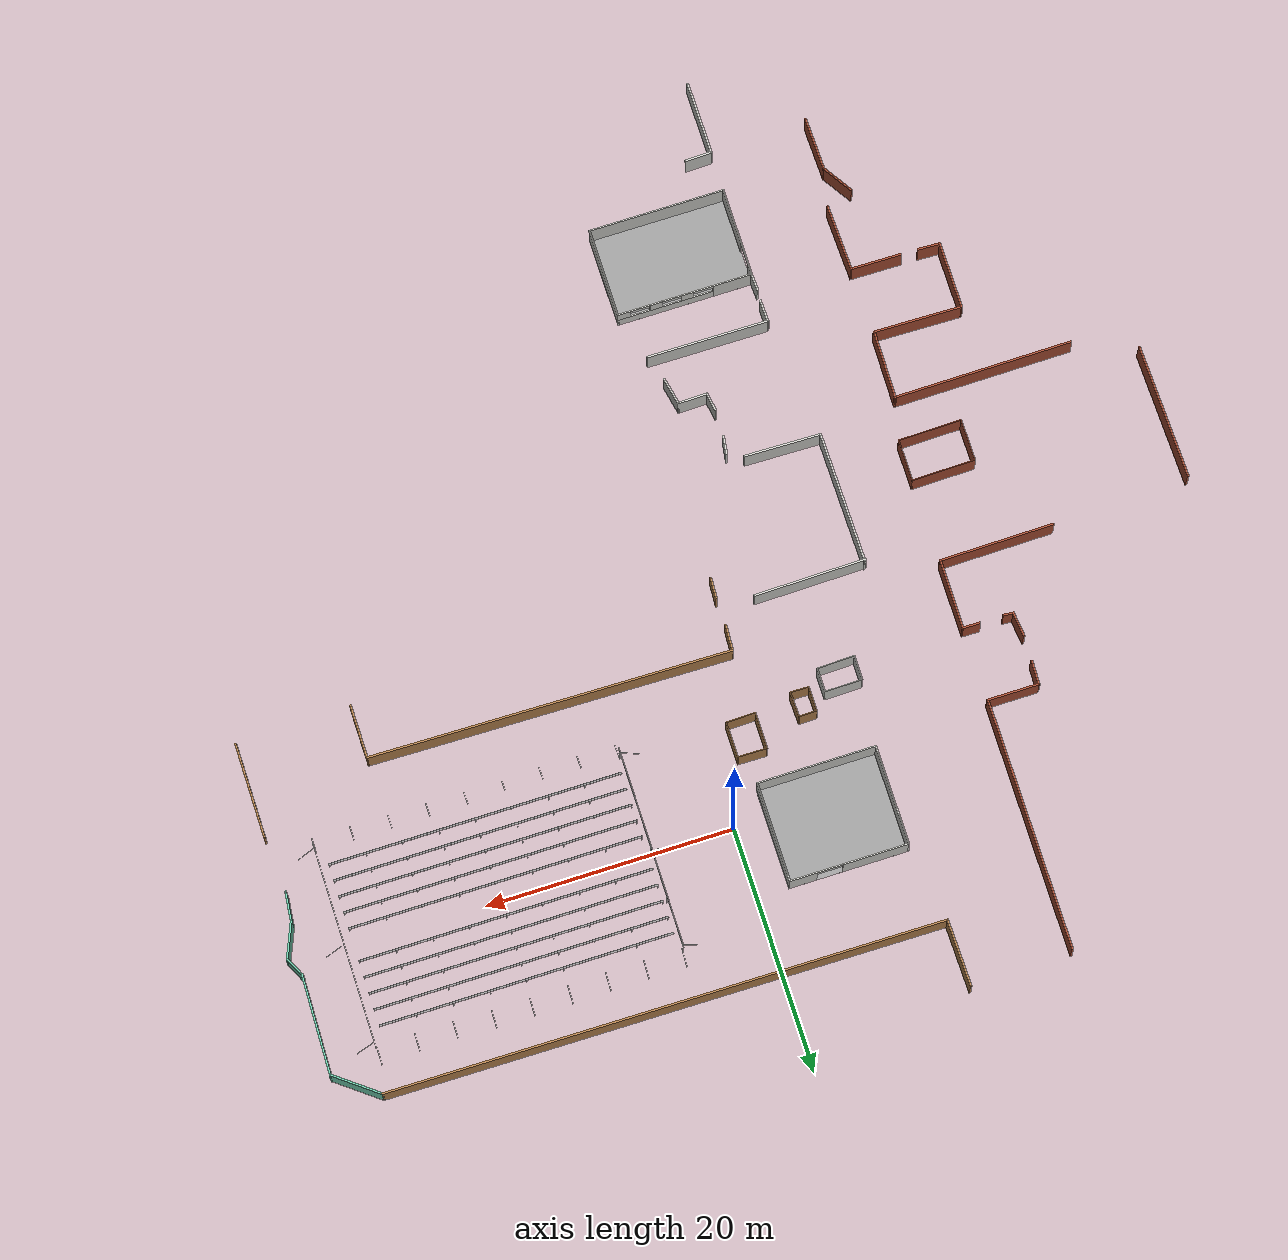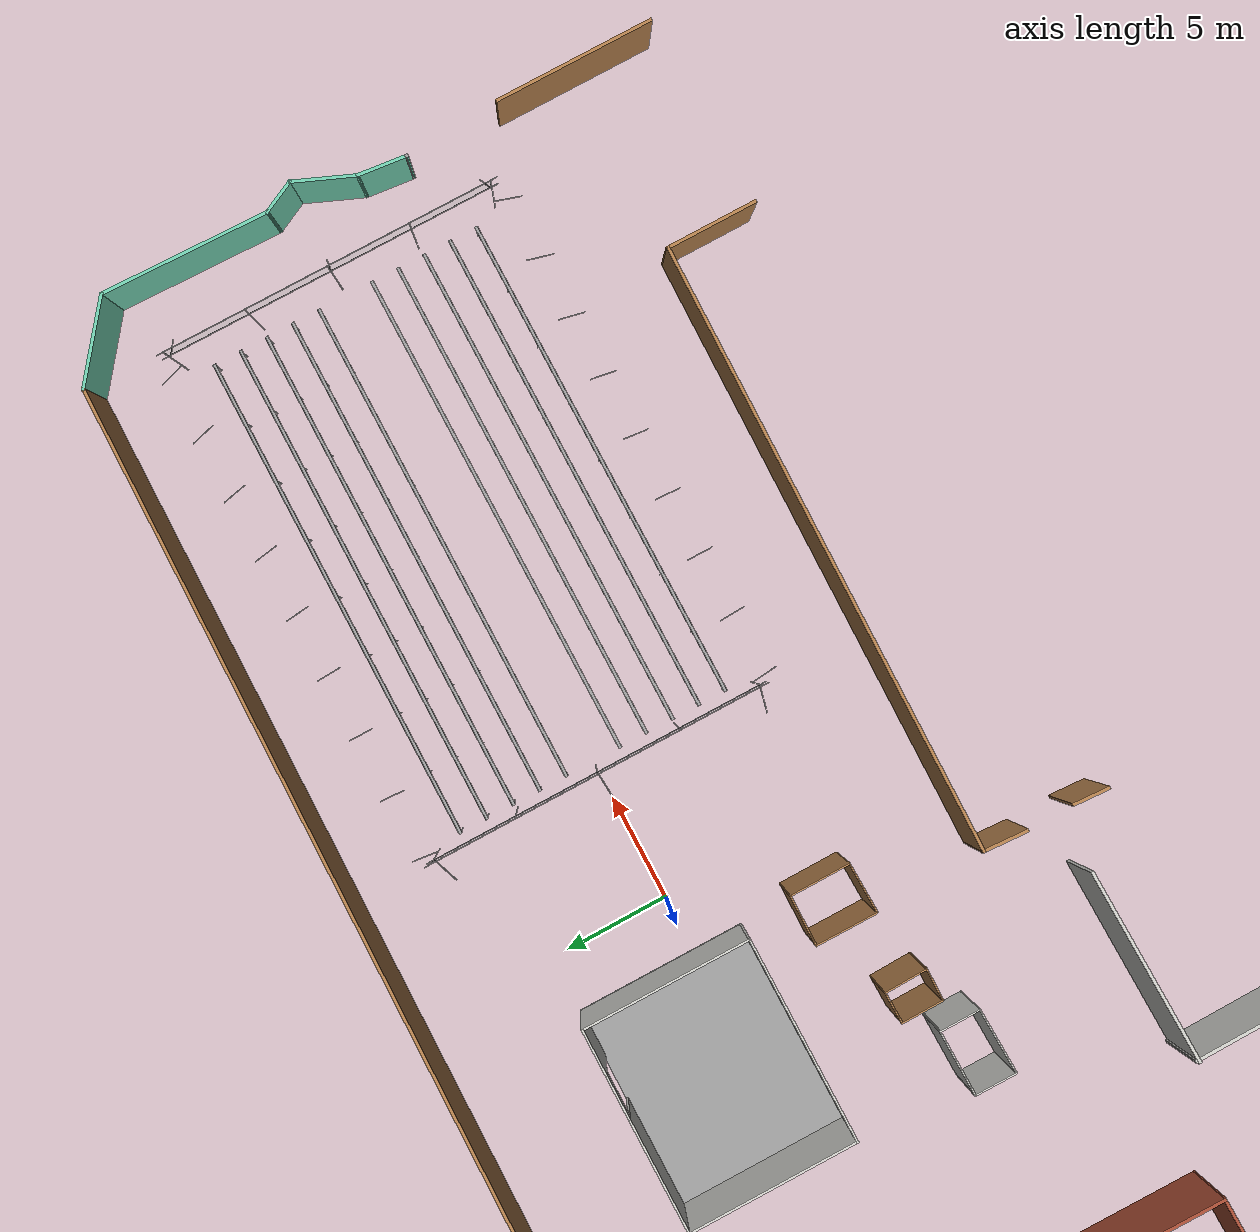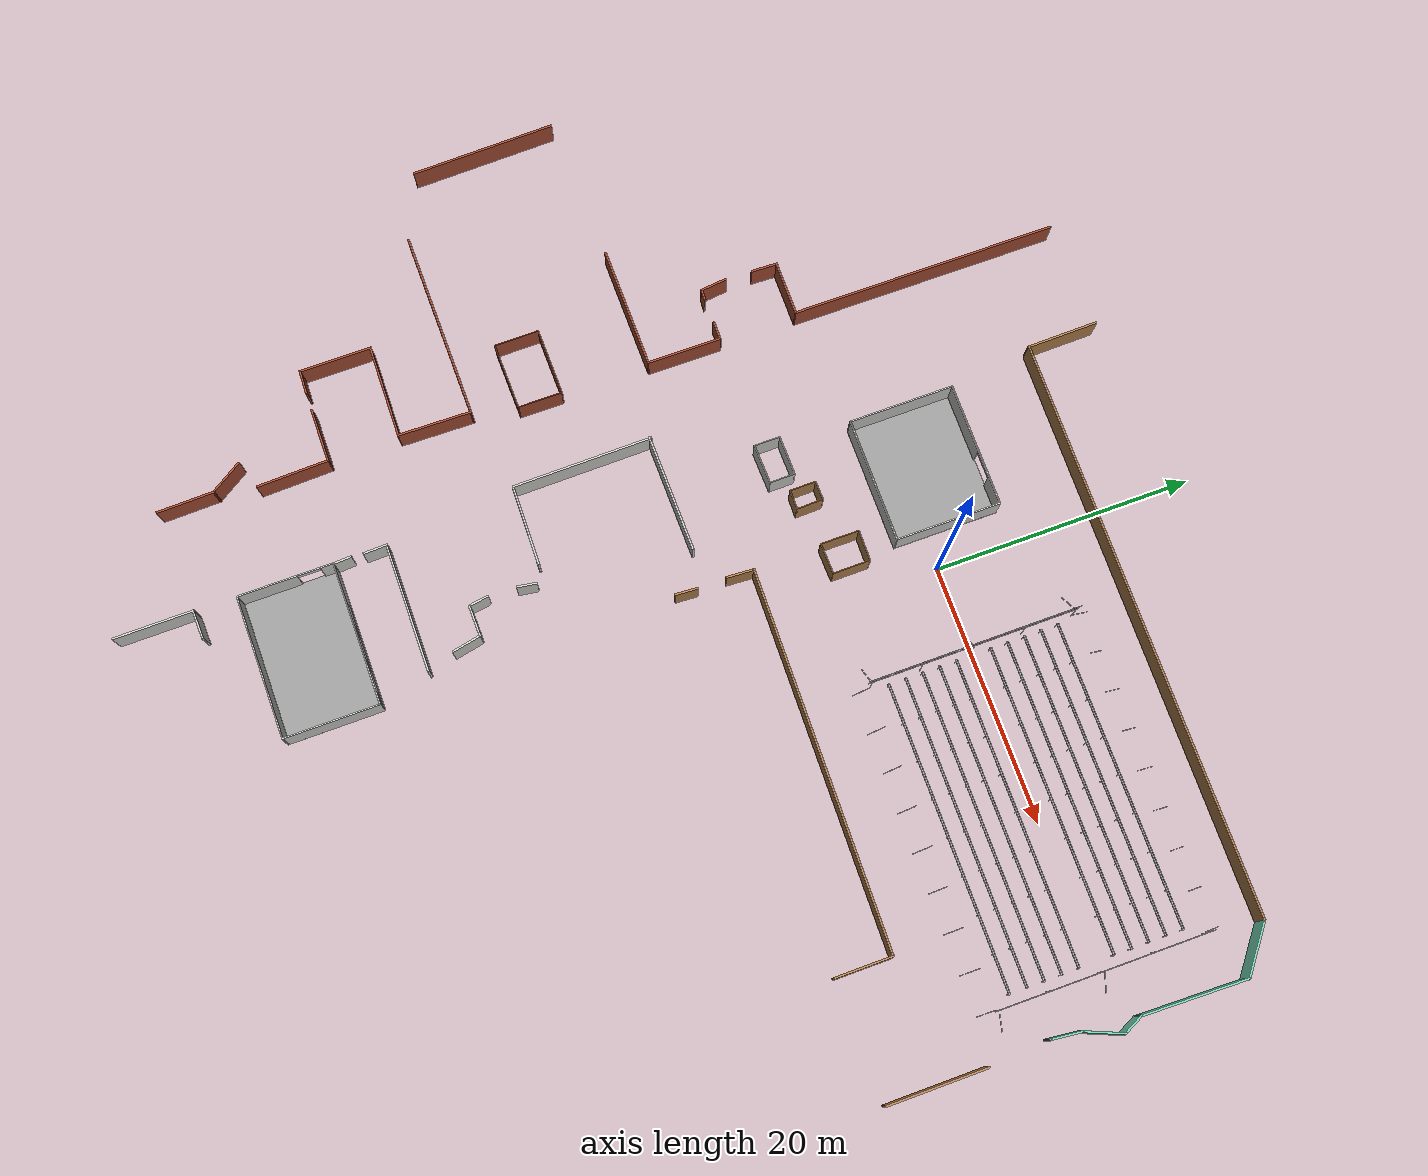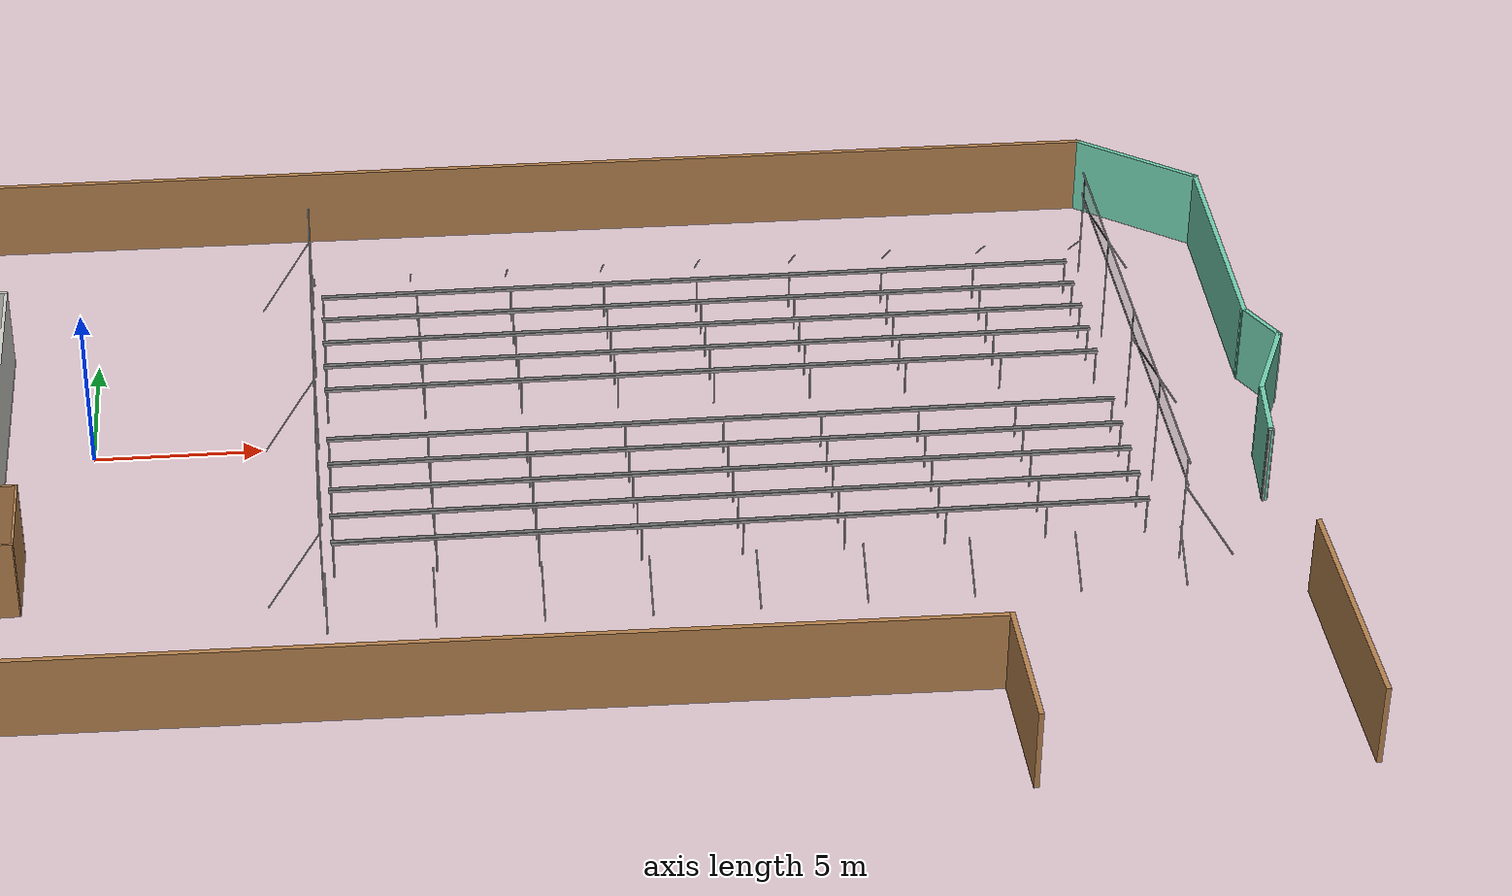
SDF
<sdf version="1.4">
 <world name="default">
  <scene><shadows>1</shadows><sky><clouds><speed>12</speed></clouds></sky></scene>
  <model name="pole_0">
   <static>1</static>
   <pose>7.000 -6.640 0.575 0.0 0.0 0.0</pose>
   <link name="link">
    <collision name="collision">
     <geometry><cylinder><length>1.15</length><radius>0.025</radius></cylinder></geometry>
    </collision>
    <visual name="visual">
     <geometry><cylinder><length>1.15</length><radius>0.025</radius></cylinder></geometry>
     <material>
      <script><uri>file://media/materials/scripts/gazebo.material</uri><name>Gazebo/Chrome</name></script>
      <shader type="vertex"><normal_map>__default__</normal_map></shader>
      <emissive>0.1 0.1 0.1 1</emissive>
      <specular>0.01 0.01 0.01 1</specular>
      <ambient>0.5 0.5 0.5 1</ambient>
      <diffuse>0.05 0.05 0.05 1</diffuse>
     </material>
    </visual>
   </link>
  </model>
  <model name="pole_1">
   <static>1</static>
   <pose>7.000 -5.320 0.575 0.0 0.0 0.0</pose>
   <link name="link">
    <collision name="collision">
     <geometry><cylinder><length>1.15</length><radius>0.025</radius></cylinder></geometry>
    </collision>
    <visual name="visual">
     <geometry><cylinder><length>1.15</length><radius>0.025</radius></cylinder></geometry>
     <material>
      <script><uri>file://media/materials/scripts/gazebo.material</uri><name>Gazebo/Chrome</name></script>
      <shader type="vertex"><normal_map>__default__</normal_map></shader>
      <emissive>0.1 0.1 0.1 1</emissive>
      <specular>0.01 0.01 0.01 1</specular>
      <ambient>0.5 0.5 0.5 1</ambient>
      <diffuse>0.05 0.05 0.05 1</diffuse>
     </material>
    </visual>
   </link>
  </model>
  <model name="pole_2">
   <static>1</static>
   <pose>7.000 -4.000 0.575 0.0 0.0 0.0</pose>
   <link name="link">
    <collision name="collision">
     <geometry><cylinder><length>1.15</length><radius>0.025</radius></cylinder></geometry>
    </collision>
    <visual name="visual">
     <geometry><cylinder><length>1.15</length><radius>0.025</radius></cylinder></geometry>
     <material>
      <script><uri>file://media/materials/scripts/gazebo.material</uri><name>Gazebo/Chrome</name></script>
      <shader type="vertex"><normal_map>__default__</normal_map></shader>
      <emissive>0.1 0.1 0.1 1</emissive>
      <specular>0.01 0.01 0.01 1</specular>
      <ambient>0.5 0.5 0.5 1</ambient>
      <diffuse>0.05 0.05 0.05 1</diffuse>
     </material>
    </visual>
   </link>
  </model>
  <model name="pole_3">
   <static>1</static>
   <pose>7.000 -2.680 0.575 0.0 0.0 0.0</pose>
   <link name="link">
    <collision name="collision">
     <geometry><cylinder><length>1.15</length><radius>0.025</radius></cylinder></geometry>
    </collision>
    <visual name="visual">
     <geometry><cylinder><length>1.15</length><radius>0.025</radius></cylinder></geometry>
     <material>
      <script><uri>file://media/materials/scripts/gazebo.material</uri><name>Gazebo/Chrome</name></script>
      <shader type="vertex"><normal_map>__default__</normal_map></shader>
      <emissive>0.1 0.1 0.1 1</emissive>
      <specular>0.01 0.01 0.01 1</specular>
      <ambient>0.5 0.5 0.5 1</ambient>
      <diffuse>0.05 0.05 0.05 1</diffuse>
     </material>
    </visual>
   </link>
  </model>
  <model name="pole_4">
   <static>1</static>
   <pose>7.000 -1.360 0.575 0.0 0.0 0.0</pose>
   <link name="link">
    <collision name="collision">
     <geometry><cylinder><length>1.15</length><radius>0.025</radius></cylinder></geometry>
    </collision>
    <visual name="visual">
     <geometry><cylinder><length>1.15</length><radius>0.025</radius></cylinder></geometry>
     <material>
      <script><uri>file://media/materials/scripts/gazebo.material</uri><name>Gazebo/Chrome</name></script>
      <shader type="vertex"><normal_map>__default__</normal_map></shader>
      <emissive>0.1 0.1 0.1 1</emissive>
      <specular>0.01 0.01 0.01 1</specular>
      <ambient>0.5 0.5 0.5 1</ambient>
      <diffuse>0.05 0.05 0.05 1</diffuse>
     </material>
    </visual>
   </link>
  </model>
  <model name="pole_5">
   <static>1</static>
   <pose>9.940 -6.640 0.575 0.0 0.0 0.0</pose>
   <link name="link">
    <collision name="collision">
     <geometry><cylinder><length>1.15</length><radius>0.025</radius></cylinder></geometry>
    </collision>
    <visual name="visual">
     <geometry><cylinder><length>1.15</length><radius>0.025</radius></cylinder></geometry>
     <material>
      <script><uri>file://media/materials/scripts/gazebo.material</uri><name>Gazebo/Chrome</name></script>
      <shader type="vertex"><normal_map>__default__</normal_map></shader>
      <emissive>0.1 0.1 0.1 1</emissive>
      <specular>0.01 0.01 0.01 1</specular>
      <ambient>0.5 0.5 0.5 1</ambient>
      <diffuse>0.05 0.05 0.05 1</diffuse>
     </material>
    </visual>
   </link>
  </model>
  <model name="pole_6">
   <static>1</static>
   <pose>9.940 -5.320 0.575 0.0 0.0 0.0</pose>
   <link name="link">
    <collision name="collision">
     <geometry><cylinder><length>1.15</length><radius>0.025</radius></cylinder></geometry>
    </collision>
    <visual name="visual">
     <geometry><cylinder><length>1.15</length><radius>0.025</radius></cylinder></geometry>
     <material>
      <script><uri>file://media/materials/scripts/gazebo.material</uri><name>Gazebo/Chrome</name></script>
      <shader type="vertex"><normal_map>__default__</normal_map></shader>
      <emissive>0.1 0.1 0.1 1</emissive>
      <specular>0.01 0.01 0.01 1</specular>
      <ambient>0.5 0.5 0.5 1</ambient>
      <diffuse>0.05 0.05 0.05 1</diffuse>
     </material>
    </visual>
   </link>
  </model>
  <model name="pole_7">
   <static>1</static>
   <pose>9.940 -4.000 0.575 0.0 0.0 0.0</pose>
   <link name="link">
    <collision name="collision">
     <geometry><cylinder><length>1.15</length><radius>0.025</radius></cylinder></geometry>
    </collision>
    <visual name="visual">
     <geometry><cylinder><length>1.15</length><radius>0.025</radius></cylinder></geometry>
     <material>
      <script><uri>file://media/materials/scripts/gazebo.material</uri><name>Gazebo/Chrome</name></script>
      <shader type="vertex"><normal_map>__default__</normal_map></shader>
      <emissive>0.1 0.1 0.1 1</emissive>
      <specular>0.01 0.01 0.01 1</specular>
      <ambient>0.5 0.5 0.5 1</ambient>
      <diffuse>0.05 0.05 0.05 1</diffuse>
     </material>
    </visual>
   </link>
  </model>
  <model name="pole_8">
   <static>1</static>
   <pose>9.940 -2.680 0.575 0.0 0.0 0.0</pose>
   <link name="link">
    <collision name="collision">
     <geometry><cylinder><length>1.15</length><radius>0.025</radius></cylinder></geometry>
    </collision>
    <visual name="visual">
     <geometry><cylinder><length>1.15</length><radius>0.025</radius></cylinder></geometry>
     <material>
      <script><uri>file://media/materials/scripts/gazebo.material</uri><name>Gazebo/Chrome</name></script>
      <shader type="vertex"><normal_map>__default__</normal_map></shader>
      <emissive>0.1 0.1 0.1 1</emissive>
      <specular>0.01 0.01 0.01 1</specular>
      <ambient>0.5 0.5 0.5 1</ambient>
      <diffuse>0.05 0.05 0.05 1</diffuse>
     </material>
    </visual>
   </link>
  </model>
  <model name="pole_9">
   <static>1</static>
   <pose>9.940 -1.360 0.575 0.0 0.0 0.0</pose>
   <link name="link">
    <collision name="collision">
     <geometry><cylinder><length>1.15</length><radius>0.025</radius></cylinder></geometry>
    </collision>
    <visual name="visual">
     <geometry><cylinder><length>1.15</length><radius>0.025</radius></cylinder></geometry>
     <material>
      <script><uri>file://media/materials/scripts/gazebo.material</uri><name>Gazebo/Chrome</name></script>
      <shader type="vertex"><normal_map>__default__</normal_map></shader>
      <emissive>0.1 0.1 0.1 1</emissive>
      <specular>0.01 0.01 0.01 1</specular>
      <ambient>0.5 0.5 0.5 1</ambient>
      <diffuse>0.05 0.05 0.05 1</diffuse>
     </material>
    </visual>
   </link>
  </model>
  <model name="pole_10">
   <static>1</static>
   <pose>12.880 -6.640 0.575 0.0 0.0 0.0</pose>
   <link name="link">
    <collision name="collision">
     <geometry><cylinder><length>1.15</length><radius>0.025</radius></cylinder></geometry>
    </collision>
    <visual name="visual">
     <geometry><cylinder><length>1.15</length><radius>0.025</radius></cylinder></geometry>
     <material>
      <script><uri>file://media/materials/scripts/gazebo.material</uri><name>Gazebo/Chrome</name></script>
      <shader type="vertex"><normal_map>__default__</normal_map></shader>
      <emissive>0.1 0.1 0.1 1</emissive>
      <specular>0.01 0.01 0.01 1</specular>
      <ambient>0.5 0.5 0.5 1</ambient>
      <diffuse>0.05 0.05 0.05 1</diffuse>
     </material>
    </visual>
   </link>
  </model>
  <model name="pole_11">
   <static>1</static>
   <pose>12.880 -5.320 0.575 0.0 0.0 0.0</pose>
   <link name="link">
    <collision name="collision">
     <geometry><cylinder><length>1.15</length><radius>0.025</radius></cylinder></geometry>
    </collision>
    <visual name="visual">
     <geometry><cylinder><length>1.15</length><radius>0.025</radius></cylinder></geometry>
     <material>
      <script><uri>file://media/materials/scripts/gazebo.material</uri><name>Gazebo/Chrome</name></script>
      <shader type="vertex"><normal_map>__default__</normal_map></shader>
      <emissive>0.1 0.1 0.1 1</emissive>
      <specular>0.01 0.01 0.01 1</specular>
      <ambient>0.5 0.5 0.5 1</ambient>
      <diffuse>0.05 0.05 0.05 1</diffuse>
     </material>
    </visual>
   </link>
  </model>
  <model name="pole_12">
   <static>1</static>
   <pose>12.880 -4.000 0.575 0.0 0.0 0.0</pose>
   <link name="link">
    <collision name="collision">
     <geometry><cylinder><length>1.15</length><radius>0.025</radius></cylinder></geometry>
    </collision>
    <visual name="visual">
     <geometry><cylinder><length>1.15</length><radius>0.025</radius></cylinder></geometry>
     <material>
      <script><uri>file://media/materials/scripts/gazebo.material</uri><name>Gazebo/Chrome</name></script>
      <shader type="vertex"><normal_map>__default__</normal_map></shader>
      <emissive>0.1 0.1 0.1 1</emissive>
      <specular>0.01 0.01 0.01 1</specular>
      <ambient>0.5 0.5 0.5 1</ambient>
      <diffuse>0.05 0.05 0.05 1</diffuse>
     </material>
    </visual>
   </link>
  </model>
  <model name="pole_13">
   <static>1</static>
   <pose>12.880 -2.680 0.575 0.0 0.0 0.0</pose>
   <link name="link">
    <collision name="collision">
     <geometry><cylinder><length>1.15</length><radius>0.025</radius></cylinder></geometry>
    </collision>
    <visual name="visual">
     <geometry><cylinder><length>1.15</length><radius>0.025</radius></cylinder></geometry>
     <material>
      <script><uri>file://media/materials/scripts/gazebo.material</uri><name>Gazebo/Chrome</name></script>
      <shader type="vertex"><normal_map>__default__</normal_map></shader>
      <emissive>0.1 0.1 0.1 1</emissive>
      <specular>0.01 0.01 0.01 1</specular>
      <ambient>0.5 0.5 0.5 1</ambient>
      <diffuse>0.05 0.05 0.05 1</diffuse>
     </material>
    </visual>
   </link>
  </model>
  <model name="pole_14">
   <static>1</static>
   <pose>12.880 -1.360 0.575 0.0 0.0 0.0</pose>
   <link name="link">
    <collision name="collision">
     <geometry><cylinder><length>1.15</length><radius>0.025</radius></cylinder></geometry>
    </collision>
    <visual name="visual">
     <geometry><cylinder><length>1.15</length><radius>0.025</radius></cylinder></geometry>
     <material>
      <script><uri>file://media/materials/scripts/gazebo.material</uri><name>Gazebo/Chrome</name></script>
      <shader type="vertex"><normal_map>__default__</normal_map></shader>
      <emissive>0.1 0.1 0.1 1</emissive>
      <specular>0.01 0.01 0.01 1</specular>
      <ambient>0.5 0.5 0.5 1</ambient>
      <diffuse>0.05 0.05 0.05 1</diffuse>
     </material>
    </visual>
   </link>
  </model>
  <model name="pole_15">
   <static>1</static>
   <pose>15.820 -6.640 0.575 0.0 0.0 0.0</pose>
   <link name="link">
    <collision name="collision">
     <geometry><cylinder><length>1.15</length><radius>0.025</radius></cylinder></geometry>
    </collision>
    <visual name="visual">
     <geometry><cylinder><length>1.15</length><radius>0.025</radius></cylinder></geometry>
     <material>
      <script><uri>file://media/materials/scripts/gazebo.material</uri><name>Gazebo/Chrome</name></script>
      <shader type="vertex"><normal_map>__default__</normal_map></shader>
      <emissive>0.1 0.1 0.1 1</emissive>
      <specular>0.01 0.01 0.01 1</specular>
      <ambient>0.5 0.5 0.5 1</ambient>
      <diffuse>0.05 0.05 0.05 1</diffuse>
     </material>
    </visual>
   </link>
  </model>
  <model name="pole_16">
   <static>1</static>
   <pose>15.820 -5.320 0.575 0.0 0.0 0.0</pose>
   <link name="link">
    <collision name="collision">
     <geometry><cylinder><length>1.15</length><radius>0.025</radius></cylinder></geometry>
    </collision>
    <visual name="visual">
     <geometry><cylinder><length>1.15</length><radius>0.025</radius></cylinder></geometry>
     <material>
      <script><uri>file://media/materials/scripts/gazebo.material</uri><name>Gazebo/Chrome</name></script>
      <shader type="vertex"><normal_map>__default__</normal_map></shader>
      <emissive>0.1 0.1 0.1 1</emissive>
      <specular>0.01 0.01 0.01 1</specular>
      <ambient>0.5 0.5 0.5 1</ambient>
      <diffuse>0.05 0.05 0.05 1</diffuse>
     </material>
    </visual>
   </link>
  </model>
  <model name="pole_17">
   <static>1</static>
   <pose>15.820 -4.000 0.575 0.0 0.0 0.0</pose>
   <link name="link">
    <collision name="collision">
     <geometry><cylinder><length>1.15</length><radius>0.025</radius></cylinder></geometry>
    </collision>
    <visual name="visual">
     <geometry><cylinder><length>1.15</length><radius>0.025</radius></cylinder></geometry>
     <material>
      <script><uri>file://media/materials/scripts/gazebo.material</uri><name>Gazebo/Chrome</name></script>
      <shader type="vertex"><normal_map>__default__</normal_map></shader>
      <emissive>0.1 0.1 0.1 1</emissive>
      <specular>0.01 0.01 0.01 1</specular>
      <ambient>0.5 0.5 0.5 1</ambient>
      <diffuse>0.05 0.05 0.05 1</diffuse>
     </material>
    </visual>
   </link>
  </model>
  <model name="pole_18">
   <static>1</static>
   <pose>15.820 -2.680 0.575 0.0 0.0 0.0</pose>
   <link name="link">
    <collision name="collision">
     <geometry><cylinder><length>1.15</length><radius>0.025</radius></cylinder></geometry>
    </collision>
    <visual name="visual">
     <geometry><cylinder><length>1.15</length><radius>0.025</radius></cylinder></geometry>
     <material>
      <script><uri>file://media/materials/scripts/gazebo.material</uri><name>Gazebo/Chrome</name></script>
      <shader type="vertex"><normal_map>__default__</normal_map></shader>
      <emissive>0.1 0.1 0.1 1</emissive>
      <specular>0.01 0.01 0.01 1</specular>
      <ambient>0.5 0.5 0.5 1</ambient>
      <diffuse>0.05 0.05 0.05 1</diffuse>
     </material>
    </visual>
   </link>
  </model>
  <model name="pole_19">
   <static>1</static>
   <pose>15.820 -1.360 0.575 0.0 0.0 0.0</pose>
   <link name="link">
    <collision name="collision">
     <geometry><cylinder><length>1.15</length><radius>0.025</radius></cylinder></geometry>
    </collision>
    <visual name="visual">
     <geometry><cylinder><length>1.15</length><radius>0.025</radius></cylinder></geometry>
     <material>
      <script><uri>file://media/materials/scripts/gazebo.material</uri><name>Gazebo/Chrome</name></script>
      <shader type="vertex"><normal_map>__default__</normal_map></shader>
      <emissive>0.1 0.1 0.1 1</emissive>
      <specular>0.01 0.01 0.01 1</specular>
      <ambient>0.5 0.5 0.5 1</ambient>
      <diffuse>0.05 0.05 0.05 1</diffuse>
     </material>
    </visual>
   </link>
  </model>
  <model name="pole_20">
   <static>1</static>
   <pose>18.760 -6.640 0.575 0.0 0.0 0.0</pose>
   <link name="link">
    <collision name="collision">
     <geometry><cylinder><length>1.15</length><radius>0.025</radius></cylinder></geometry>
    </collision>
    <visual name="visual">
     <geometry><cylinder><length>1.15</length><radius>0.025</radius></cylinder></geometry>
     <material>
      <script><uri>file://media/materials/scripts/gazebo.material</uri><name>Gazebo/Chrome</name></script>
      <shader type="vertex"><normal_map>__default__</normal_map></shader>
      <emissive>0.1 0.1 0.1 1</emissive>
      <specular>0.01 0.01 0.01 1</specular>
      <ambient>0.5 0.5 0.5 1</ambient>
      <diffuse>0.05 0.05 0.05 1</diffuse>
     </material>
    </visual>
   </link>
  </model>
  <model name="pole_21">
   <static>1</static>
   <pose>18.760 -5.320 0.575 0.0 0.0 0.0</pose>
   <link name="link">
    <collision name="collision">
     <geometry><cylinder><length>1.15</length><radius>0.025</radius></cylinder></geometry>
    </collision>
    <visual name="visual">
     <geometry><cylinder><length>1.15</length><radius>0.025</radius></cylinder></geometry>
     <material>
      <script><uri>file://media/materials/scripts/gazebo.material</uri><name>Gazebo/Chrome</name></script>
      <shader type="vertex"><normal_map>__default__</normal_map></shader>
      <emissive>0.1 0.1 0.1 1</emissive>
      <specular>0.01 0.01 0.01 1</specular>
      <ambient>0.5 0.5 0.5 1</ambient>
      <diffuse>0.05 0.05 0.05 1</diffuse>
     </material>
    </visual>
   </link>
  </model>
  <model name="pole_22">
   <static>1</static>
   <pose>18.760 -4.000 0.575 0.0 0.0 0.0</pose>
   <link name="link">
    <collision name="collision">
     <geometry><cylinder><length>1.15</length><radius>0.025</radius></cylinder></geometry>
    </collision>
    <visual name="visual">
     <geometry><cylinder><length>1.15</length><radius>0.025</radius></cylinder></geometry>
     <material>
      <script><uri>file://media/materials/scripts/gazebo.material</uri><name>Gazebo/Chrome</name></script>
      <shader type="vertex"><normal_map>__default__</normal_map></shader>
      <emissive>0.1 0.1 0.1 1</emissive>
      <specular>0.01 0.01 0.01 1</specular>
      <ambient>0.5 0.5 0.5 1</ambient>
      <diffuse>0.05 0.05 0.05 1</diffuse>
     </material>
    </visual>
   </link>
  </model>
  <model name="pole_23">
   <static>1</static>
   <pose>18.760 -2.680 0.575 0.0 0.0 0.0</pose>
   <link name="link">
    <collision name="collision">
     <geometry><cylinder><length>1.15</length><radius>0.025</radius></cylinder></geometry>
    </collision>
    <visual name="visual">
     <geometry><cylinder><length>1.15</length><radius>0.025</radius></cylinder></geometry>
     <material>
      <script><uri>file://media/materials/scripts/gazebo.material</uri><name>Gazebo/Chrome</name></script>
      <shader type="vertex"><normal_map>__default__</normal_map></shader>
      <emissive>0.1 0.1 0.1 1</emissive>
      <specular>0.01 0.01 0.01 1</specular>
      <ambient>0.5 0.5 0.5 1</ambient>
      <diffuse>0.05 0.05 0.05 1</diffuse>
     </material>
    </visual>
   </link>
  </model>
  <model name="pole_24">
   <static>1</static>
   <pose>18.760 -1.360 0.575 0.0 0.0 0.0</pose>
   <link name="link">
    <collision name="collision">
     <geometry><cylinder><length>1.15</length><radius>0.025</radius></cylinder></geometry>
    </collision>
    <visual name="visual">
     <geometry><cylinder><length>1.15</length><radius>0.025</radius></cylinder></geometry>
     <material>
      <script><uri>file://media/materials/scripts/gazebo.material</uri><name>Gazebo/Chrome</name></script>
      <shader type="vertex"><normal_map>__default__</normal_map></shader>
      <emissive>0.1 0.1 0.1 1</emissive>
      <specular>0.01 0.01 0.01 1</specular>
      <ambient>0.5 0.5 0.5 1</ambient>
      <diffuse>0.05 0.05 0.05 1</diffuse>
     </material>
    </visual>
   </link>
  </model>
  <model name="pole_25">
   <static>1</static>
   <pose>21.700 -6.640 0.575 0.0 0.0 0.0</pose>
   <link name="link">
    <collision name="collision">
     <geometry><cylinder><length>1.15</length><radius>0.025</radius></cylinder></geometry>
    </collision>
    <visual name="visual">
     <geometry><cylinder><length>1.15</length><radius>0.025</radius></cylinder></geometry>
     <material>
      <script><uri>file://media/materials/scripts/gazebo.material</uri><name>Gazebo/Chrome</name></script>
      <shader type="vertex"><normal_map>__default__</normal_map></shader>
      <emissive>0.1 0.1 0.1 1</emissive>
      <specular>0.01 0.01 0.01 1</specular>
      <ambient>0.5 0.5 0.5 1</ambient>
      <diffuse>0.05 0.05 0.05 1</diffuse>
     </material>
    </visual>
   </link>
  </model>
  <model name="pole_26">
   <static>1</static>
   <pose>21.700 -5.320 0.575 0.0 0.0 0.0</pose>
   <link name="link">
    <collision name="collision">
     <geometry><cylinder><length>1.15</length><radius>0.025</radius></cylinder></geometry>
    </collision>
    <visual name="visual">
     <geometry><cylinder><length>1.15</length><radius>0.025</radius></cylinder></geometry>
     <material>
      <script><uri>file://media/materials/scripts/gazebo.material</uri><name>Gazebo/Chrome</name></script>
      <shader type="vertex"><normal_map>__default__</normal_map></shader>
      <emissive>0.1 0.1 0.1 1</emissive>
      <specular>0.01 0.01 0.01 1</specular>
      <ambient>0.5 0.5 0.5 1</ambient>
      <diffuse>0.05 0.05 0.05 1</diffuse>
     </material>
    </visual>
   </link>
  </model>
  <model name="pole_27">
   <static>1</static>
   <pose>21.700 -4.000 0.575 0.0 0.0 0.0</pose>
   <link name="link">
    <collision name="collision">
     <geometry><cylinder><length>1.15</length><radius>0.025</radius></cylinder></geometry>
    </collision>
    <visual name="visual">
     <geometry><cylinder><length>1.15</length><radius>0.025</radius></cylinder></geometry>
     <material>
      <script><uri>file://media/materials/scripts/gazebo.material</uri><name>Gazebo/Chrome</name></script>
      <shader type="vertex"><normal_map>__default__</normal_map></shader>
      <emissive>0.1 0.1 0.1 1</emissive>
      <specular>0.01 0.01 0.01 1</specular>
      <ambient>0.5 0.5 0.5 1</ambient>
      <diffuse>0.05 0.05 0.05 1</diffuse>
     </material>
    </visual>
   </link>
  </model>
  <model name="pole_28">
   <static>1</static>
   <pose>21.700 -2.680 0.575 0.0 0.0 0.0</pose>
   <link name="link">
    <collision name="collision">
     <geometry><cylinder><length>1.15</length><radius>0.025</radius></cylinder></geometry>
    </collision>
    <visual name="visual">
     <geometry><cylinder><length>1.15</length><radius>0.025</radius></cylinder></geometry>
     <material>
      <script><uri>file://media/materials/scripts/gazebo.material</uri><name>Gazebo/Chrome</name></script>
      <shader type="vertex"><normal_map>__default__</normal_map></shader>
      <emissive>0.1 0.1 0.1 1</emissive>
      <specular>0.01 0.01 0.01 1</specular>
      <ambient>0.5 0.5 0.5 1</ambient>
      <diffuse>0.05 0.05 0.05 1</diffuse>
     </material>
    </visual>
   </link>
  </model>
  <model name="pole_29">
   <static>1</static>
   <pose>21.700 -1.360 0.575 0.0 0.0 0.0</pose>
   <link name="link">
    <collision name="collision">
     <geometry><cylinder><length>1.15</length><radius>0.025</radius></cylinder></geometry>
    </collision>
    <visual name="visual">
     <geometry><cylinder><length>1.15</length><radius>0.025</radius></cylinder></geometry>
     <material>
      <script><uri>file://media/materials/scripts/gazebo.material</uri><name>Gazebo/Chrome</name></script>
      <shader type="vertex"><normal_map>__default__</normal_map></shader>
      <emissive>0.1 0.1 0.1 1</emissive>
      <specular>0.01 0.01 0.01 1</specular>
      <ambient>0.5 0.5 0.5 1</ambient>
      <diffuse>0.05 0.05 0.05 1</diffuse>
     </material>
    </visual>
   </link>
  </model>
  <model name="pole_30">
   <static>1</static>
   <pose>24.640 -6.640 0.575 0.0 0.0 0.0</pose>
   <link name="link">
    <collision name="collision">
     <geometry><cylinder><length>1.15</length><radius>0.025</radius></cylinder></geometry>
    </collision>
    <visual name="visual">
     <geometry><cylinder><length>1.15</length><radius>0.025</radius></cylinder></geometry>
     <material>
      <script><uri>file://media/materials/scripts/gazebo.material</uri><name>Gazebo/Chrome</name></script>
      <shader type="vertex"><normal_map>__default__</normal_map></shader>
      <emissive>0.1 0.1 0.1 1</emissive>
      <specular>0.01 0.01 0.01 1</specular>
      <ambient>0.5 0.5 0.5 1</ambient>
      <diffuse>0.05 0.05 0.05 1</diffuse>
     </material>
    </visual>
   </link>
  </model>
  <model name="pole_31">
   <static>1</static>
   <pose>24.640 -5.320 0.575 0.0 0.0 0.0</pose>
   <link name="link">
    <collision name="collision">
     <geometry><cylinder><length>1.15</length><radius>0.025</radius></cylinder></geometry>
    </collision>
    <visual name="visual">
     <geometry><cylinder><length>1.15</length><radius>0.025</radius></cylinder></geometry>
     <material>
      <script><uri>file://media/materials/scripts/gazebo.material</uri><name>Gazebo/Chrome</name></script>
      <shader type="vertex"><normal_map>__default__</normal_map></shader>
      <emissive>0.1 0.1 0.1 1</emissive>
      <specular>0.01 0.01 0.01 1</specular>
      <ambient>0.5 0.5 0.5 1</ambient>
      <diffuse>0.05 0.05 0.05 1</diffuse>
     </material>
    </visual>
   </link>
  </model>
  <model name="pole_32">
   <static>1</static>
   <pose>24.640 -4.000 0.575 0.0 0.0 0.0</pose>
   <link name="link">
    <collision name="collision">
     <geometry><cylinder><length>1.15</length><radius>0.025</radius></cylinder></geometry>
    </collision>
    <visual name="visual">
     <geometry><cylinder><length>1.15</length><radius>0.025</radius></cylinder></geometry>
     <material>
      <script><uri>file://media/materials/scripts/gazebo.material</uri><name>Gazebo/Chrome</name></script>
      <shader type="vertex"><normal_map>__default__</normal_map></shader>
      <emissive>0.1 0.1 0.1 1</emissive>
      <specular>0.01 0.01 0.01 1</specular>
      <ambient>0.5 0.5 0.5 1</ambient>
      <diffuse>0.05 0.05 0.05 1</diffuse>
     </material>
    </visual>
   </link>
  </model>
  <model name="pole_33">
   <static>1</static>
   <pose>24.640 -2.680 0.575 0.0 0.0 0.0</pose>
   <link name="link">
    <collision name="collision">
     <geometry><cylinder><length>1.15</length><radius>0.025</radius></cylinder></geometry>
    </collision>
    <visual name="visual">
     <geometry><cylinder><length>1.15</length><radius>0.025</radius></cylinder></geometry>
     <material>
      <script><uri>file://media/materials/scripts/gazebo.material</uri><name>Gazebo/Chrome</name></script>
      <shader type="vertex"><normal_map>__default__</normal_map></shader>
      <emissive>0.1 0.1 0.1 1</emissive>
      <specular>0.01 0.01 0.01 1</specular>
      <ambient>0.5 0.5 0.5 1</ambient>
      <diffuse>0.05 0.05 0.05 1</diffuse>
     </material>
    </visual>
   </link>
  </model>
  <model name="pole_34">
   <static>1</static>
   <pose>24.640 -1.360 0.575 0.0 0.0 0.0</pose>
   <link name="link">
    <collision name="collision">
     <geometry><cylinder><length>1.15</length><radius>0.025</radius></cylinder></geometry>
    </collision>
    <visual name="visual">
     <geometry><cylinder><length>1.15</length><radius>0.025</radius></cylinder></geometry>
     <material>
      <script><uri>file://media/materials/scripts/gazebo.material</uri><name>Gazebo/Chrome</name></script>
      <shader type="vertex"><normal_map>__default__</normal_map></shader>
      <emissive>0.1 0.1 0.1 1</emissive>
      <specular>0.01 0.01 0.01 1</specular>
      <ambient>0.5 0.5 0.5 1</ambient>
      <diffuse>0.05 0.05 0.05 1</diffuse>
     </material>
    </visual>
   </link>
  </model>
  <model name="pole_35">
   <static>1</static>
   <pose>27.580 -6.640 0.575 0.0 0.0 0.0</pose>
   <link name="link">
    <collision name="collision">
     <geometry><cylinder><length>1.15</length><radius>0.025</radius></cylinder></geometry>
    </collision>
    <visual name="visual">
     <geometry><cylinder><length>1.15</length><radius>0.025</radius></cylinder></geometry>
     <material>
      <script><uri>file://media/materials/scripts/gazebo.material</uri><name>Gazebo/Chrome</name></script>
      <shader type="vertex"><normal_map>__default__</normal_map></shader>
      <emissive>0.1 0.1 0.1 1</emissive>
      <specular>0.01 0.01 0.01 1</specular>
      <ambient>0.5 0.5 0.5 1</ambient>
      <diffuse>0.05 0.05 0.05 1</diffuse>
     </material>
    </visual>
   </link>
  </model>
  <model name="pole_36">
   <static>1</static>
   <pose>27.580 -5.320 0.575 0.0 0.0 0.0</pose>
   <link name="link">
    <collision name="collision">
     <geometry><cylinder><length>1.15</length><radius>0.025</radius></cylinder></geometry>
    </collision>
    <visual name="visual">
     <geometry><cylinder><length>1.15</length><radius>0.025</radius></cylinder></geometry>
     <material>
      <script><uri>file://media/materials/scripts/gazebo.material</uri><name>Gazebo/Chrome</name></script>
      <shader type="vertex"><normal_map>__default__</normal_map></shader>
      <emissive>0.1 0.1 0.1 1</emissive>
      <specular>0.01 0.01 0.01 1</specular>
      <ambient>0.5 0.5 0.5 1</ambient>
      <diffuse>0.05 0.05 0.05 1</diffuse>
     </material>
    </visual>
   </link>
  </model>
  <model name="pole_37">
   <static>1</static>
   <pose>27.580 -4.000 0.575 0.0 0.0 0.0</pose>
   <link name="link">
    <collision name="collision">
     <geometry><cylinder><length>1.15</length><radius>0.025</radius></cylinder></geometry>
    </collision>
    <visual name="visual">
     <geometry><cylinder><length>1.15</length><radius>0.025</radius></cylinder></geometry>
     <material>
      <script><uri>file://media/materials/scripts/gazebo.material</uri><name>Gazebo/Chrome</name></script>
      <shader type="vertex"><normal_map>__default__</normal_map></shader>
      <emissive>0.1 0.1 0.1 1</emissive>
      <specular>0.01 0.01 0.01 1</specular>
      <ambient>0.5 0.5 0.5 1</ambient>
      <diffuse>0.05 0.05 0.05 1</diffuse>
     </material>
    </visual>
   </link>
  </model>
  <model name="pole_38">
   <static>1</static>
   <pose>27.580 -2.680 0.575 0.0 0.0 0.0</pose>
   <link name="link">
    <collision name="collision">
     <geometry><cylinder><length>1.15</length><radius>0.025</radius></cylinder></geometry>
    </collision>
    <visual name="visual">
     <geometry><cylinder><length>1.15</length><radius>0.025</radius></cylinder></geometry>
     <material>
      <script><uri>file://media/materials/scripts/gazebo.material</uri><name>Gazebo/Chrome</name></script>
      <shader type="vertex"><normal_map>__default__</normal_map></shader>
      <emissive>0.1 0.1 0.1 1</emissive>
      <specular>0.01 0.01 0.01 1</specular>
      <ambient>0.5 0.5 0.5 1</ambient>
      <diffuse>0.05 0.05 0.05 1</diffuse>
     </material>
    </visual>
   </link>
  </model>
  <model name="pole_39">
   <static>1</static>
   <pose>27.580 -1.360 0.575 0.0 0.0 0.0</pose>
   <link name="link">
    <collision name="collision">
     <geometry><cylinder><length>1.15</length><radius>0.025</radius></cylinder></geometry>
    </collision>
    <visual name="visual">
     <geometry><cylinder><length>1.15</length><radius>0.025</radius></cylinder></geometry>
     <material>
      <script><uri>file://media/materials/scripts/gazebo.material</uri><name>Gazebo/Chrome</name></script>
      <shader type="vertex"><normal_map>__default__</normal_map></shader>
      <emissive>0.1 0.1 0.1 1</emissive>
      <specular>0.01 0.01 0.01 1</specular>
      <ambient>0.5 0.5 0.5 1</ambient>
      <diffuse>0.05 0.05 0.05 1</diffuse>
     </material>
    </visual>
   </link>
  </model>
  <model name="pole_40">
   <static>1</static>
   <pose>30.520 -6.640 0.575 0.0 0.0 0.0</pose>
   <link name="link">
    <collision name="collision">
     <geometry><cylinder><length>1.15</length><radius>0.025</radius></cylinder></geometry>
    </collision>
    <visual name="visual">
     <geometry><cylinder><length>1.15</length><radius>0.025</radius></cylinder></geometry>
     <material>
      <script><uri>file://media/materials/scripts/gazebo.material</uri><name>Gazebo/Chrome</name></script>
      <shader type="vertex"><normal_map>__default__</normal_map></shader>
      <emissive>0.1 0.1 0.1 1</emissive>
      <specular>0.01 0.01 0.01 1</specular>
      <ambient>0.5 0.5 0.5 1</ambient>
      <diffuse>0.05 0.05 0.05 1</diffuse>
     </material>
    </visual>
   </link>
  </model>
  <model name="pole_41">
   <static>1</static>
   <pose>30.520 -5.320 0.575 0.0 0.0 0.0</pose>
   <link name="link">
    <collision name="collision">
     <geometry><cylinder><length>1.15</length><radius>0.025</radius></cylinder></geometry>
    </collision>
    <visual name="visual">
     <geometry><cylinder><length>1.15</length><radius>0.025</radius></cylinder></geometry>
     <material>
      <script><uri>file://media/materials/scripts/gazebo.material</uri><name>Gazebo/Chrome</name></script>
      <shader type="vertex"><normal_map>__default__</normal_map></shader>
      <emissive>0.1 0.1 0.1 1</emissive>
      <specular>0.01 0.01 0.01 1</specular>
      <ambient>0.5 0.5 0.5 1</ambient>
      <diffuse>0.05 0.05 0.05 1</diffuse>
     </material>
    </visual>
   </link>
  </model>
  <model name="pole_42">
   <static>1</static>
   <pose>30.520 -4.000 0.575 0.0 0.0 0.0</pose>
   <link name="link">
    <collision name="collision">
     <geometry><cylinder><length>1.15</length><radius>0.025</radius></cylinder></geometry>
    </collision>
    <visual name="visual">
     <geometry><cylinder><length>1.15</length><radius>0.025</radius></cylinder></geometry>
     <material>
      <script><uri>file://media/materials/scripts/gazebo.material</uri><name>Gazebo/Chrome</name></script>
      <shader type="vertex"><normal_map>__default__</normal_map></shader>
      <emissive>0.1 0.1 0.1 1</emissive>
      <specular>0.01 0.01 0.01 1</specular>
      <ambient>0.5 0.5 0.5 1</ambient>
      <diffuse>0.05 0.05 0.05 1</diffuse>
     </material>
    </visual>
   </link>
  </model>
  <model name="pole_43">
   <static>1</static>
   <pose>30.520 -2.680 0.575 0.0 0.0 0.0</pose>
   <link name="link">
    <collision name="collision">
     <geometry><cylinder><length>1.15</length><radius>0.025</radius></cylinder></geometry>
    </collision>
    <visual name="visual">
     <geometry><cylinder><length>1.15</length><radius>0.025</radius></cylinder></geometry>
     <material>
      <script><uri>file://media/materials/scripts/gazebo.material</uri><name>Gazebo/Chrome</name></script>
      <shader type="vertex"><normal_map>__default__</normal_map></shader>
      <emissive>0.1 0.1 0.1 1</emissive>
      <specular>0.01 0.01 0.01 1</specular>
      <ambient>0.5 0.5 0.5 1</ambient>
      <diffuse>0.05 0.05 0.05 1</diffuse>
     </material>
    </visual>
   </link>
  </model>
  <model name="pole_44">
   <static>1</static>
   <pose>30.520 -1.360 0.575 0.0 0.0 0.0</pose>
   <link name="link">
    <collision name="collision">
     <geometry><cylinder><length>1.15</length><radius>0.025</radius></cylinder></geometry>
    </collision>
    <visual name="visual">
     <geometry><cylinder><length>1.15</length><radius>0.025</radius></cylinder></geometry>
     <material>
      <script><uri>file://media/materials/scripts/gazebo.material</uri><name>Gazebo/Chrome</name></script>
      <shader type="vertex"><normal_map>__default__</normal_map></shader>
      <emissive>0.1 0.1 0.1 1</emissive>
      <specular>0.01 0.01 0.01 1</specular>
      <ambient>0.5 0.5 0.5 1</ambient>
      <diffuse>0.05 0.05 0.05 1</diffuse>
     </material>
    </visual>
   </link>
  </model>
  <model name="tray_0">
   <static>1</static>
   <link name="link_0">
    <collision name="collision"><geometry><box><size>23.620 0.15 0.005</size></box></geometry></collision>
    <visual name="visual">
     <geometry><box><size>23.620 0.15 0.005</size></box></geometry>
     <material>
      <script><uri>file://media/materials/scripts/gazebo.material</uri><name>Gazebo/Grey</name></script>
      <emissive>0 0 0 1</emissive>
      <shader type="vertex"><normal_map>__default__</normal_map></shader>
      <specular>0.01 0.01 0.01 1</specular>
      <lighting>1</lighting>
      <ambient>0.7 0.7 0.7 1</ambient>
      <diffuse>0.3 0.3 0.3 1</diffuse>
     </material>
    </visual>
    <pose>18.760 -6.640 1.14965 0.0 0.0 0.0</pose>
   </link>
  </model>
  <model name="tray_1">
   <static>1</static>
   <link name="link_0">
    <collision name="collision"><geometry><box><size>23.620 0.15 0.005</size></box></geometry></collision>
    <visual name="visual">
     <geometry><box><size>23.620 0.15 0.005</size></box></geometry>
     <material>
      <script><uri>file://media/materials/scripts/gazebo.material</uri><name>Gazebo/Grey</name></script>
      <emissive>0 0 0 1</emissive>
      <shader type="vertex"><normal_map>__default__</normal_map></shader>
      <specular>0.01 0.01 0.01 1</specular>
      <lighting>1</lighting>
      <ambient>0.7 0.7 0.7 1</ambient>
      <diffuse>0.3 0.3 0.3 1</diffuse>
     </material>
    </visual>
    <pose>18.760 -5.320 1.14965 0.0 0.0 0.0</pose>
   </link>
  </model>
  <model name="tray_2">
   <static>1</static>
   <link name="link_0">
    <collision name="collision"><geometry><box><size>23.620 0.15 0.005</size></box></geometry></collision>
    <visual name="visual">
     <geometry><box><size>23.620 0.15 0.005</size></box></geometry>
     <material>
      <script><uri>file://media/materials/scripts/gazebo.material</uri><name>Gazebo/Grey</name></script>
      <emissive>0 0 0 1</emissive>
      <shader type="vertex"><normal_map>__default__</normal_map></shader>
      <specular>0.01 0.01 0.01 1</specular>
      <lighting>1</lighting>
      <ambient>0.7 0.7 0.7 1</ambient>
      <diffuse>0.3 0.3 0.3 1</diffuse>
     </material>
    </visual>
    <pose>18.760 -4.000 1.14965 0.0 0.0 0.0</pose>
   </link>
  </model>
  <model name="tray_3">
   <static>1</static>
   <link name="link_0">
    <collision name="collision"><geometry><box><size>23.620 0.15 0.005</size></box></geometry></collision>
    <visual name="visual">
     <geometry><box><size>23.620 0.15 0.005</size></box></geometry>
     <material>
      <script><uri>file://media/materials/scripts/gazebo.material</uri><name>Gazebo/Grey</name></script>
      <emissive>0 0 0 1</emissive>
      <shader type="vertex"><normal_map>__default__</normal_map></shader>
      <specular>0.01 0.01 0.01 1</specular>
      <lighting>1</lighting>
      <ambient>0.7 0.7 0.7 1</ambient>
      <diffuse>0.3 0.3 0.3 1</diffuse>
     </material>
    </visual>
    <pose>18.760 -2.680 1.14965 0.0 0.0 0.0</pose>
   </link>
  </model>
  <model name="tray_4">
   <static>1</static>
   <link name="link_0">
    <collision name="collision"><geometry><box><size>23.620 0.15 0.005</size></box></geometry></collision>
    <visual name="visual">
     <geometry><box><size>23.620 0.15 0.005</size></box></geometry>
     <material>
      <script><uri>file://media/materials/scripts/gazebo.material</uri><name>Gazebo/Grey</name></script>
      <emissive>0 0 0 1</emissive>
      <shader type="vertex"><normal_map>__default__</normal_map></shader>
      <specular>0.01 0.01 0.01 1</specular>
      <lighting>1</lighting>
      <ambient>0.7 0.7 0.7 1</ambient>
      <diffuse>0.3 0.3 0.3 1</diffuse>
     </material>
    </visual>
    <pose>18.760 -1.360 1.14965 0.0 0.0 0.0</pose>
   </link>
  </model>
  <model name="tray_p2_0">
   <static>1</static>
   <link name="link_0">
    <collision name="collision"><geometry><box><size>23.62 0.085 0.005</size></box></geometry></collision>
    <visual name="visual">
     <geometry><box><size>23.62 0.085 0.005</size></box></geometry>
     <material>
      <script><uri>file://media/materials/scripts/gazebo.material</uri><name>Gazebo/Grey</name></script>
      <emissive>0 0 0 1</emissive>
      <shader type="vertex"><normal_map>__default__</normal_map></shader>
      <specular>0.01 0.01 0.01 1</specular>
      <lighting>1</lighting>
      <ambient>0.7 0.7 0.7 1</ambient>
      <diffuse>0.3 0.3 0.3 1</diffuse>
     </material>
    </visual>
    <pose>18.760 -6.715 1.19165 1.5707 0.0 0.0</pose>
   </link>
  </model>
  <model name="tray_p2_1">
   <static>1</static>
   <link name="link_0">
    <collision name="collision"><geometry><box><size>23.62 0.085 0.005</size></box></geometry></collision>
    <visual name="visual">
     <geometry><box><size>23.62 0.085 0.005</size></box></geometry>
     <material>
      <script><uri>file://media/materials/scripts/gazebo.material</uri><name>Gazebo/Grey</name></script>
      <emissive>0 0 0 1</emissive>
      <shader type="vertex"><normal_map>__default__</normal_map></shader>
      <specular>0.01 0.01 0.01 1</specular>
      <lighting>1</lighting>
      <ambient>0.7 0.7 0.7 1</ambient>
      <diffuse>0.3 0.3 0.3 1</diffuse>
     </material>
    </visual>
    <pose>18.760 -5.395 1.19165 1.5707 0.0 0.0</pose>
   </link>
  </model>
  <model name="tray_p2_2">
   <static>1</static>
   <link name="link_0">
    <collision name="collision"><geometry><box><size>23.62 0.085 0.005</size></box></geometry></collision>
    <visual name="visual">
     <geometry><box><size>23.62 0.085 0.005</size></box></geometry>
     <material>
      <script><uri>file://media/materials/scripts/gazebo.material</uri><name>Gazebo/Grey</name></script>
      <emissive>0 0 0 1</emissive>
      <shader type="vertex"><normal_map>__default__</normal_map></shader>
      <specular>0.01 0.01 0.01 1</specular>
      <lighting>1</lighting>
      <ambient>0.7 0.7 0.7 1</ambient>
      <diffuse>0.3 0.3 0.3 1</diffuse>
     </material>
    </visual>
    <pose>18.760 -4.075 1.19165 1.5707 0.0 0.0</pose>
   </link>
  </model>
  <model name="tray_p2_3">
   <static>1</static>
   <link name="link_0">
    <collision name="collision"><geometry><box><size>23.62 0.085 0.005</size></box></geometry></collision>
    <visual name="visual">
     <geometry><box><size>23.62 0.085 0.005</size></box></geometry>
     <material>
      <script><uri>file://media/materials/scripts/gazebo.material</uri><name>Gazebo/Grey</name></script>
      <emissive>0 0 0 1</emissive>
      <shader type="vertex"><normal_map>__default__</normal_map></shader>
      <specular>0.01 0.01 0.01 1</specular>
      <lighting>1</lighting>
      <ambient>0.7 0.7 0.7 1</ambient>
      <diffuse>0.3 0.3 0.3 1</diffuse>
     </material>
    </visual>
    <pose>18.760 -2.755 1.19165 1.5707 0.0 0.0</pose>
   </link>
  </model>
  <model name="tray_p2_4">
   <static>1</static>
   <link name="link_0">
    <collision name="collision"><geometry><box><size>23.62 0.085 0.005</size></box></geometry></collision>
    <visual name="visual">
     <geometry><box><size>23.62 0.085 0.005</size></box></geometry>
     <material>
      <script><uri>file://media/materials/scripts/gazebo.material</uri><name>Gazebo/Grey</name></script>
      <emissive>0 0 0 1</emissive>
      <shader type="vertex"><normal_map>__default__</normal_map></shader>
      <specular>0.01 0.01 0.01 1</specular>
      <lighting>1</lighting>
      <ambient>0.7 0.7 0.7 1</ambient>
      <diffuse>0.3 0.3 0.3 1</diffuse>
     </material>
    </visual>
    <pose>18.760 -1.435 1.19165 1.5707 0.0 0.0</pose>
   </link>
  </model>
  <model name="tray_p2_5">
   <static>1</static>
   <link name="link_0">
    <collision name="collision"><geometry><box><size>23.62 0.085 0.005</size></box></geometry></collision>
    <visual name="visual">
     <geometry><box><size>23.62 0.085 0.005</size></box></geometry>
     <material>
      <script><uri>file://media/materials/scripts/gazebo.material</uri><name>Gazebo/Grey</name></script>
      <emissive>0 0 0 1</emissive>
      <shader type="vertex"><normal_map>__default__</normal_map></shader>
      <specular>0.01 0.01 0.01 1</specular>
      <lighting>1</lighting>
      <ambient>0.7 0.7 0.7 1</ambient>
      <diffuse>0.3 0.3 0.3 1</diffuse>
     </material>
    </visual>
    <pose>18.760 -6.565 1.19165 1.5707 0.0 0.0</pose>
   </link>
  </model>
  <model name="tray_p2_6">
   <static>1</static>
   <link name="link_0">
    <collision name="collision"><geometry><box><size>23.62 0.085 0.005</size></box></geometry></collision>
    <visual name="visual">
     <geometry><box><size>23.62 0.085 0.005</size></box></geometry>
     <material>
      <script><uri>file://media/materials/scripts/gazebo.material</uri><name>Gazebo/Grey</name></script>
      <emissive>0 0 0 1</emissive>
      <shader type="vertex"><normal_map>__default__</normal_map></shader>
      <specular>0.01 0.01 0.01 1</specular>
      <lighting>1</lighting>
      <ambient>0.7 0.7 0.7 1</ambient>
      <diffuse>0.3 0.3 0.3 1</diffuse>
     </material>
    </visual>
    <pose>18.760 -5.245 1.19165 1.5707 0.0 0.0</pose>
   </link>
  </model>
  <model name="tray_p2_7">
   <static>1</static>
   <link name="link_0">
    <collision name="collision"><geometry><box><size>23.62 0.085 0.005</size></box></geometry></collision>
    <visual name="visual">
     <geometry><box><size>23.62 0.085 0.005</size></box></geometry>
     <material>
      <script><uri>file://media/materials/scripts/gazebo.material</uri><name>Gazebo/Grey</name></script>
      <emissive>0 0 0 1</emissive>
      <shader type="vertex"><normal_map>__default__</normal_map></shader>
      <specular>0.01 0.01 0.01 1</specular>
      <lighting>1</lighting>
      <ambient>0.7 0.7 0.7 1</ambient>
      <diffuse>0.3 0.3 0.3 1</diffuse>
     </material>
    </visual>
    <pose>18.760 -3.925 1.19165 1.5707 0.0 0.0</pose>
   </link>
  </model>
  <model name="tray_p2_8">
   <static>1</static>
   <link name="link_0">
    <collision name="collision"><geometry><box><size>23.62 0.085 0.005</size></box></geometry></collision>
    <visual name="visual">
     <geometry><box><size>23.62 0.085 0.005</size></box></geometry>
     <material>
      <script><uri>file://media/materials/scripts/gazebo.material</uri><name>Gazebo/Grey</name></script>
      <emissive>0 0 0 1</emissive>
      <shader type="vertex"><normal_map>__default__</normal_map></shader>
      <specular>0.01 0.01 0.01 1</specular>
      <lighting>1</lighting>
      <ambient>0.7 0.7 0.7 1</ambient>
      <diffuse>0.3 0.3 0.3 1</diffuse>
     </material>
    </visual>
    <pose>18.760 -2.605 1.19165 1.5707 0.0 0.0</pose>
   </link>
  </model>
  <model name="tray_p2_9">
   <static>1</static>
   <link name="link_0">
    <collision name="collision"><geometry><box><size>23.62 0.085 0.005</size></box></geometry></collision>
    <visual name="visual">
     <geometry><box><size>23.62 0.085 0.005</size></box></geometry>
     <material>
      <script><uri>file://media/materials/scripts/gazebo.material</uri><name>Gazebo/Grey</name></script>
      <emissive>0 0 0 1</emissive>
      <shader type="vertex"><normal_map>__default__</normal_map></shader>
      <specular>0.01 0.01 0.01 1</specular>
      <lighting>1</lighting>
      <ambient>0.7 0.7 0.7 1</ambient>
      <diffuse>0.3 0.3 0.3 1</diffuse>
     </material>
    </visual>
    <pose>18.760 -1.285 1.19165 1.5707 0.0 0.0</pose>
   </link>
  </model>
  <model name="strut_0">
   <static>1</static>
   <pose>6.740 -8.623 0.536 -0.896 0.0 0.0</pose>
   <link name="link">
    <collision name="collision">
     <geometry><cylinder><length>1.76</length><radius>0.02</radius></cylinder></geometry>
    </collision>
    <visual name="visual">
     <geometry><cylinder><length>1.76</length><radius>0.02</radius></cylinder></geometry>
     <material>
      <script><uri>file://media/materials/scripts/gazebo.material</uri><name>Gazebo/Chrome</name></script>
      <shader type="vertex"><normal_map>__default__</normal_map></shader>
      <emissive>0.1 0.1 0.1 1</emissive>
      <specular>0.01 0.01 0.01 1</specular>
      <ambient>0.5 0.5 0.5 1</ambient>
      <diffuse>0.05 0.05 0.05 1</diffuse>
     </material>
    </visual>
   </link>
  </model>
  <model name="strut_1">
   <static>1</static>
   <pose>9.800 -8.623 0.536 -0.896 0.0 0.0</pose>
   <link name="link">
    <collision name="collision">
     <geometry><cylinder><length>1.76</length><radius>0.02</radius></cylinder></geometry>
    </collision>
    <visual name="visual">
     <geometry><cylinder><length>1.76</length><radius>0.02</radius></cylinder></geometry>
     <material>
      <script><uri>file://media/materials/scripts/gazebo.material</uri><name>Gazebo/Chrome</name></script>
      <shader type="vertex"><normal_map>__default__</normal_map></shader>
      <emissive>0.1 0.1 0.1 1</emissive>
      <specular>0.01 0.01 0.01 1</specular>
      <ambient>0.5 0.5 0.5 1</ambient>
      <diffuse>0.05 0.05 0.05 1</diffuse>
     </material>
    </visual>
   </link>
  </model>
  <model name="strut_2">
   <static>1</static>
   <pose>12.860 -8.623 0.536 -0.896 0.0 0.0</pose>
   <link name="link">
    <collision name="collision">
     <geometry><cylinder><length>1.76</length><radius>0.02</radius></cylinder></geometry>
    </collision>
    <visual name="visual">
     <geometry><cylinder><length>1.76</length><radius>0.02</radius></cylinder></geometry>
     <material>
      <script><uri>file://media/materials/scripts/gazebo.material</uri><name>Gazebo/Chrome</name></script>
      <shader type="vertex"><normal_map>__default__</normal_map></shader>
      <emissive>0.1 0.1 0.1 1</emissive>
      <specular>0.01 0.01 0.01 1</specular>
      <ambient>0.5 0.5 0.5 1</ambient>
      <diffuse>0.05 0.05 0.05 1</diffuse>
     </material>
    </visual>
   </link>
  </model>
  <model name="strut_3">
   <static>1</static>
   <pose>15.920 -8.623 0.536 -0.896 0.0 0.0</pose>
   <link name="link">
    <collision name="collision">
     <geometry><cylinder><length>1.76</length><radius>0.02</radius></cylinder></geometry>
    </collision>
    <visual name="visual">
     <geometry><cylinder><length>1.76</length><radius>0.02</radius></cylinder></geometry>
     <material>
      <script><uri>file://media/materials/scripts/gazebo.material</uri><name>Gazebo/Chrome</name></script>
      <shader type="vertex"><normal_map>__default__</normal_map></shader>
      <emissive>0.1 0.1 0.1 1</emissive>
      <specular>0.01 0.01 0.01 1</specular>
      <ambient>0.5 0.5 0.5 1</ambient>
      <diffuse>0.05 0.05 0.05 1</diffuse>
     </material>
    </visual>
   </link>
  </model>
  <model name="strut_4">
   <static>1</static>
   <pose>18.980 -8.623 0.536 -0.896 0.0 0.0</pose>
   <link name="link">
    <collision name="collision">
     <geometry><cylinder><length>1.76</length><radius>0.02</radius></cylinder></geometry>
    </collision>
    <visual name="visual">
     <geometry><cylinder><length>1.76</length><radius>0.02</radius></cylinder></geometry>
     <material>
      <script><uri>file://media/materials/scripts/gazebo.material</uri><name>Gazebo/Chrome</name></script>
      <shader type="vertex"><normal_map>__default__</normal_map></shader>
      <emissive>0.1 0.1 0.1 1</emissive>
      <specular>0.01 0.01 0.01 1</specular>
      <ambient>0.5 0.5 0.5 1</ambient>
      <diffuse>0.05 0.05 0.05 1</diffuse>
     </material>
    </visual>
   </link>
  </model>
  <model name="strut_5">
   <static>1</static>
   <pose>22.040 -8.623 0.536 -0.896 0.0 0.0</pose>
   <link name="link">
    <collision name="collision">
     <geometry><cylinder><length>1.76</length><radius>0.02</radius></cylinder></geometry>
    </collision>
    <visual name="visual">
     <geometry><cylinder><length>1.76</length><radius>0.02</radius></cylinder></geometry>
     <material>
      <script><uri>file://media/materials/scripts/gazebo.material</uri><name>Gazebo/Chrome</name></script>
      <shader type="vertex"><normal_map>__default__</normal_map></shader>
      <emissive>0.1 0.1 0.1 1</emissive>
      <specular>0.01 0.01 0.01 1</specular>
      <ambient>0.5 0.5 0.5 1</ambient>
      <diffuse>0.05 0.05 0.05 1</diffuse>
     </material>
    </visual>
   </link>
  </model>
  <model name="strut_6">
   <static>1</static>
   <pose>25.100 -8.623 0.536 -0.896 0.0 0.0</pose>
   <link name="link">
    <collision name="collision">
     <geometry><cylinder><length>1.76</length><radius>0.02</radius></cylinder></geometry>
    </collision>
    <visual name="visual">
     <geometry><cylinder><length>1.76</length><radius>0.02</radius></cylinder></geometry>
     <material>
      <script><uri>file://media/materials/scripts/gazebo.material</uri><name>Gazebo/Chrome</name></script>
      <shader type="vertex"><normal_map>__default__</normal_map></shader>
      <emissive>0.1 0.1 0.1 1</emissive>
      <specular>0.01 0.01 0.01 1</specular>
      <ambient>0.5 0.5 0.5 1</ambient>
      <diffuse>0.05 0.05 0.05 1</diffuse>
     </material>
    </visual>
   </link>
  </model>
  <model name="strut_7">
   <static>1</static>
   <pose>28.160 -8.623 0.536 -0.896 0.0 0.0</pose>
   <link name="link">
    <collision name="collision">
     <geometry><cylinder><length>1.76</length><radius>0.02</radius></cylinder></geometry>
    </collision>
    <visual name="visual">
     <geometry><cylinder><length>1.76</length><radius>0.02</radius></cylinder></geometry>
     <material>
      <script><uri>file://media/materials/scripts/gazebo.material</uri><name>Gazebo/Chrome</name></script>
      <shader type="vertex"><normal_map>__default__</normal_map></shader>
      <emissive>0.1 0.1 0.1 1</emissive>
      <specular>0.01 0.01 0.01 1</specular>
      <ambient>0.5 0.5 0.5 1</ambient>
      <diffuse>0.05 0.05 0.05 1</diffuse>
     </material>
    </visual>
   </link>
  </model>
  <model name="strut_8">
   <static>1</static>
   <pose>31.220 -8.623 0.536 -0.896 0.0 0.0</pose>
   <link name="link">
    <collision name="collision">
     <geometry><cylinder><length>1.76</length><radius>0.02</radius></cylinder></geometry>
    </collision>
    <visual name="visual">
     <geometry><cylinder><length>1.76</length><radius>0.02</radius></cylinder></geometry>
     <material>
      <script><uri>file://media/materials/scripts/gazebo.material</uri><name>Gazebo/Chrome</name></script>
      <shader type="vertex"><normal_map>__default__</normal_map></shader>
      <emissive>0.1 0.1 0.1 1</emissive>
      <specular>0.01 0.01 0.01 1</specular>
      <ambient>0.5 0.5 0.5 1</ambient>
      <diffuse>0.05 0.05 0.05 1</diffuse>
     </material>
    </visual>
   </link>
  </model>
  <model name="pole_45">
   <static>1</static>
   <pose>7.000 1.320 0.575 0.0 0.0 0.0</pose>
   <link name="link">
    <collision name="collision">
     <geometry><cylinder><length>1.15</length><radius>0.025</radius></cylinder></geometry>
    </collision>
    <visual name="visual">
     <geometry><cylinder><length>1.15</length><radius>0.025</radius></cylinder></geometry>
     <material>
      <script><uri>file://media/materials/scripts/gazebo.material</uri><name>Gazebo/Chrome</name></script>
      <shader type="vertex"><normal_map>__default__</normal_map></shader>
      <emissive>0.1 0.1 0.1 1</emissive>
      <specular>0.01 0.01 0.01 1</specular>
      <ambient>0.5 0.5 0.5 1</ambient>
      <diffuse>0.05 0.05 0.05 1</diffuse>
     </material>
    </visual>
   </link>
  </model>
  <model name="pole_46">
   <static>1</static>
   <pose>7.000 2.640 0.575 0.0 0.0 0.0</pose>
   <link name="link">
    <collision name="collision">
     <geometry><cylinder><length>1.15</length><radius>0.025</radius></cylinder></geometry>
    </collision>
    <visual name="visual">
     <geometry><cylinder><length>1.15</length><radius>0.025</radius></cylinder></geometry>
     <material>
      <script><uri>file://media/materials/scripts/gazebo.material</uri><name>Gazebo/Chrome</name></script>
      <shader type="vertex"><normal_map>__default__</normal_map></shader>
      <emissive>0.1 0.1 0.1 1</emissive>
      <specular>0.01 0.01 0.01 1</specular>
      <ambient>0.5 0.5 0.5 1</ambient>
      <diffuse>0.05 0.05 0.05 1</diffuse>
     </material>
    </visual>
   </link>
  </model>
  <model name="pole_47">
   <static>1</static>
   <pose>7.000 3.960 0.575 0.0 0.0 0.0</pose>
   <link name="link">
    <collision name="collision">
     <geometry><cylinder><length>1.15</length><radius>0.025</radius></cylinder></geometry>
    </collision>
    <visual name="visual">
     <geometry><cylinder><length>1.15</length><radius>0.025</radius></cylinder></geometry>
     <material>
      <script><uri>file://media/materials/scripts/gazebo.material</uri><name>Gazebo/Chrome</name></script>
      <shader type="vertex"><normal_map>__default__</normal_map></shader>
      <emissive>0.1 0.1 0.1 1</emissive>
      <specular>0.01 0.01 0.01 1</specular>
      <ambient>0.5 0.5 0.5 1</ambient>
      <diffuse>0.05 0.05 0.05 1</diffuse>
     </material>
    </visual>
   </link>
  </model>
  <model name="pole_48">
   <static>1</static>
   <pose>7.000 5.280 0.575 0.0 0.0 0.0</pose>
   <link name="link">
    <collision name="collision">
     <geometry><cylinder><length>1.15</length><radius>0.025</radius></cylinder></geometry>
    </collision>
    <visual name="visual">
     <geometry><cylinder><length>1.15</length><radius>0.025</radius></cylinder></geometry>
     <material>
      <script><uri>file://media/materials/scripts/gazebo.material</uri><name>Gazebo/Chrome</name></script>
      <shader type="vertex"><normal_map>__default__</normal_map></shader>
      <emissive>0.1 0.1 0.1 1</emissive>
      <specular>0.01 0.01 0.01 1</specular>
      <ambient>0.5 0.5 0.5 1</ambient>
      <diffuse>0.05 0.05 0.05 1</diffuse>
     </material>
    </visual>
   </link>
  </model>
  <model name="pole_49">
   <static>1</static>
   <pose>7.000 6.600 0.575 0.0 0.0 0.0</pose>
   <link name="link">
    <collision name="collision">
     <geometry><cylinder><length>1.15</length><radius>0.025</radius></cylinder></geometry>
    </collision>
    <visual name="visual">
     <geometry><cylinder><length>1.15</length><radius>0.025</radius></cylinder></geometry>
     <material>
      <script><uri>file://media/materials/scripts/gazebo.material</uri><name>Gazebo/Chrome</name></script>
      <shader type="vertex"><normal_map>__default__</normal_map></shader>
      <emissive>0.1 0.1 0.1 1</emissive>
      <specular>0.01 0.01 0.01 1</specular>
      <ambient>0.5 0.5 0.5 1</ambient>
      <diffuse>0.05 0.05 0.05 1</diffuse>
     </material>
    </visual>
   </link>
  </model>
  <model name="pole_50">
   <static>1</static>
   <pose>9.940 1.320 0.575 0.0 0.0 0.0</pose>
   <link name="link">
    <collision name="collision">
     <geometry><cylinder><length>1.15</length><radius>0.025</radius></cylinder></geometry>
    </collision>
    <visual name="visual">
     <geometry><cylinder><length>1.15</length><radius>0.025</radius></cylinder></geometry>
     <material>
      <script><uri>file://media/materials/scripts/gazebo.material</uri><name>Gazebo/Chrome</name></script>
      <shader type="vertex"><normal_map>__default__</normal_map></shader>
      <emissive>0.1 0.1 0.1 1</emissive>
      <specular>0.01 0.01 0.01 1</specular>
      <ambient>0.5 0.5 0.5 1</ambient>
      <diffuse>0.05 0.05 0.05 1</diffuse>
     </material>
    </visual>
   </link>
  </model>
  <model name="pole_51">
   <static>1</static>
   <pose>9.940 2.640 0.575 0.0 0.0 0.0</pose>
   <link name="link">
    <collision name="collision">
     <geometry><cylinder><length>1.15</length><radius>0.025</radius></cylinder></geometry>
    </collision>
    <visual name="visual">
     <geometry><cylinder><length>1.15</length><radius>0.025</radius></cylinder></geometry>
     <material>
      <script><uri>file://media/materials/scripts/gazebo.material</uri><name>Gazebo/Chrome</name></script>
      <shader type="vertex"><normal_map>__default__</normal_map></shader>
      <emissive>0.1 0.1 0.1 1</emissive>
      <specular>0.01 0.01 0.01 1</specular>
      <ambient>0.5 0.5 0.5 1</ambient>
      <diffuse>0.05 0.05 0.05 1</diffuse>
     </material>
    </visual>
   </link>
  </model>
  <model name="pole_52">
   <static>1</static>
   <pose>9.940 3.960 0.575 0.0 0.0 0.0</pose>
   <link name="link">
    <collision name="collision">
     <geometry><cylinder><length>1.15</length><radius>0.025</radius></cylinder></geometry>
    </collision>
    <visual name="visual">
     <geometry><cylinder><length>1.15</length><radius>0.025</radius></cylinder></geometry>
     <material>
      <script><uri>file://media/materials/scripts/gazebo.material</uri><name>Gazebo/Chrome</name></script>
      <shader type="vertex"><normal_map>__default__</normal_map></shader>
      <emissive>0.1 0.1 0.1 1</emissive>
      <specular>0.01 0.01 0.01 1</specular>
      <ambient>0.5 0.5 0.5 1</ambient>
      <diffuse>0.05 0.05 0.05 1</diffuse>
     </material>
    </visual>
   </link>
  </model>
  <model name="pole_53">
   <static>1</static>
   <pose>9.940 5.280 0.575 0.0 0.0 0.0</pose>
   <link name="link">
    <collision name="collision">
     <geometry><cylinder><length>1.15</length><radius>0.025</radius></cylinder></geometry>
    </collision>
    <visual name="visual">
     <geometry><cylinder><length>1.15</length><radius>0.025</radius></cylinder></geometry>
     <material>
      <script><uri>file://media/materials/scripts/gazebo.material</uri><name>Gazebo/Chrome</name></script>
      <shader type="vertex"><normal_map>__default__</normal_map></shader>
      <emissive>0.1 0.1 0.1 1</emissive>
      <specular>0.01 0.01 0.01 1</specular>
      <ambient>0.5 0.5 0.5 1</ambient>
      <diffuse>0.05 0.05 0.05 1</diffuse>
     </material>
    </visual>
   </link>
  </model>
  <model name="pole_54">
   <static>1</static>
   <pose>9.940 6.600 0.575 0.0 0.0 0.0</pose>
   <link name="link">
    <collision name="collision">
     <geometry><cylinder><length>1.15</length><radius>0.025</radius></cylinder></geometry>
    </collision>
    <visual name="visual">
     <geometry><cylinder><length>1.15</length><radius>0.025</radius></cylinder></geometry>
     <material>
      <script><uri>file://media/materials/scripts/gazebo.material</uri><name>Gazebo/Chrome</name></script>
      <shader type="vertex"><normal_map>__default__</normal_map></shader>
      <emissive>0.1 0.1 0.1 1</emissive>
      <specular>0.01 0.01 0.01 1</specular>
      <ambient>0.5 0.5 0.5 1</ambient>
      <diffuse>0.05 0.05 0.05 1</diffuse>
     </material>
    </visual>
   </link>
  </model>
  <model name="pole_55">
   <static>1</static>
   <pose>12.880 1.320 0.575 0.0 0.0 0.0</pose>
   <link name="link">
    <collision name="collision">
     <geometry><cylinder><length>1.15</length><radius>0.025</radius></cylinder></geometry>
    </collision>
    <visual name="visual">
     <geometry><cylinder><length>1.15</length><radius>0.025</radius></cylinder></geometry>
     <material>
      <script><uri>file://media/materials/scripts/gazebo.material</uri><name>Gazebo/Chrome</name></script>
      <shader type="vertex"><normal_map>__default__</normal_map></shader>
      <emissive>0.1 0.1 0.1 1</emissive>
      <specular>0.01 0.01 0.01 1</specular>
      <ambient>0.5 0.5 0.5 1</ambient>
      <diffuse>0.05 0.05 0.05 1</diffuse>
     </material>
    </visual>
   </link>
  </model>
  <model name="pole_56">
   <static>1</static>
   <pose>12.880 2.640 0.575 0.0 0.0 0.0</pose>
   <link name="link">
    <collision name="collision">
     <geometry><cylinder><length>1.15</length><radius>0.025</radius></cylinder></geometry>
    </collision>
    <visual name="visual">
     <geometry><cylinder><length>1.15</length><radius>0.025</radius></cylinder></geometry>
     <material>
      <script><uri>file://media/materials/scripts/gazebo.material</uri><name>Gazebo/Chrome</name></script>
      <shader type="vertex"><normal_map>__default__</normal_map></shader>
      <emissive>0.1 0.1 0.1 1</emissive>
      <specular>0.01 0.01 0.01 1</specular>
      <ambient>0.5 0.5 0.5 1</ambient>
      <diffuse>0.05 0.05 0.05 1</diffuse>
     </material>
    </visual>
   </link>
  </model>
  <model name="pole_57">
   <static>1</static>
   <pose>12.880 3.960 0.575 0.0 0.0 0.0</pose>
   <link name="link">
    <collision name="collision">
     <geometry><cylinder><length>1.15</length><radius>0.025</radius></cylinder></geometry>
    </collision>
    <visual name="visual">
     <geometry><cylinder><length>1.15</length><radius>0.025</radius></cylinder></geometry>
     <material>
      <script><uri>file://media/materials/scripts/gazebo.material</uri><name>Gazebo/Chrome</name></script>
      <shader type="vertex"><normal_map>__default__</normal_map></shader>
      <emissive>0.1 0.1 0.1 1</emissive>
      <specular>0.01 0.01 0.01 1</specular>
      <ambient>0.5 0.5 0.5 1</ambient>
      <diffuse>0.05 0.05 0.05 1</diffuse>
     </material>
    </visual>
   </link>
  </model>
  <model name="pole_58">
   <static>1</static>
   <pose>12.880 5.280 0.575 0.0 0.0 0.0</pose>
   <link name="link">
    <collision name="collision">
     <geometry><cylinder><length>1.15</length><radius>0.025</radius></cylinder></geometry>
    </collision>
    <visual name="visual">
     <geometry><cylinder><length>1.15</length><radius>0.025</radius></cylinder></geometry>
     <material>
      <script><uri>file://media/materials/scripts/gazebo.material</uri><name>Gazebo/Chrome</name></script>
      <shader type="vertex"><normal_map>__default__</normal_map></shader>
      <emissive>0.1 0.1 0.1 1</emissive>
      <specular>0.01 0.01 0.01 1</specular>
      <ambient>0.5 0.5 0.5 1</ambient>
      <diffuse>0.05 0.05 0.05 1</diffuse>
     </material>
    </visual>
   </link>
  </model>
  <model name="pole_59">
   <static>1</static>
   <pose>12.880 6.600 0.575 0.0 0.0 0.0</pose>
   <link name="link">
    <collision name="collision">
     <geometry><cylinder><length>1.15</length><radius>0.025</radius></cylinder></geometry>
    </collision>
    <visual name="visual">
     <geometry><cylinder><length>1.15</length><radius>0.025</radius></cylinder></geometry>
     <material>
      <script><uri>file://media/materials/scripts/gazebo.material</uri><name>Gazebo/Chrome</name></script>
      <shader type="vertex"><normal_map>__default__</normal_map></shader>
      <emissive>0.1 0.1 0.1 1</emissive>
      <specular>0.01 0.01 0.01 1</specular>
      <ambient>0.5 0.5 0.5 1</ambient>
      <diffuse>0.05 0.05 0.05 1</diffuse>
     </material>
    </visual>
   </link>
  </model>
  <model name="pole_60">
   <static>1</static>
   <pose>15.820 1.320 0.575 0.0 0.0 0.0</pose>
   <link name="link">
    <collision name="collision">
     <geometry><cylinder><length>1.15</length><radius>0.025</radius></cylinder></geometry>
    </collision>
    <visual name="visual">
     <geometry><cylinder><length>1.15</length><radius>0.025</radius></cylinder></geometry>
     <material>
      <script><uri>file://media/materials/scripts/gazebo.material</uri><name>Gazebo/Chrome</name></script>
      <shader type="vertex"><normal_map>__default__</normal_map></shader>
      <emissive>0.1 0.1 0.1 1</emissive>
      <specular>0.01 0.01 0.01 1</specular>
      <ambient>0.5 0.5 0.5 1</ambient>
      <diffuse>0.05 0.05 0.05 1</diffuse>
     </material>
    </visual>
   </link>
  </model>
  <model name="pole_61">
   <static>1</static>
   <pose>15.820 2.640 0.575 0.0 0.0 0.0</pose>
   <link name="link">
    <collision name="collision">
     <geometry><cylinder><length>1.15</length><radius>0.025</radius></cylinder></geometry>
    </collision>
    <visual name="visual">
     <geometry><cylinder><length>1.15</length><radius>0.025</radius></cylinder></geometry>
     <material>
      <script><uri>file://media/materials/scripts/gazebo.material</uri><name>Gazebo/Chrome</name></script>
      <shader type="vertex"><normal_map>__default__</normal_map></shader>
      <emissive>0.1 0.1 0.1 1</emissive>
      <specular>0.01 0.01 0.01 1</specular>
      <ambient>0.5 0.5 0.5 1</ambient>
      <diffuse>0.05 0.05 0.05 1</diffuse>
     </material>
    </visual>
   </link>
  </model>
  <model name="pole_62">
   <static>1</static>
   <pose>15.820 3.960 0.575 0.0 0.0 0.0</pose>
   <link name="link">
    <collision name="collision">
     <geometry><cylinder><length>1.15</length><radius>0.025</radius></cylinder></geometry>
    </collision>
    <visual name="visual">
     <geometry><cylinder><length>1.15</length><radius>0.025</radius></cylinder></geometry>
     <material>
      <script><uri>file://media/materials/scripts/gazebo.material</uri><name>Gazebo/Chrome</name></script>
      <shader type="vertex"><normal_map>__default__</normal_map></shader>
      <emissive>0.1 0.1 0.1 1</emissive>
      <specular>0.01 0.01 0.01 1</specular>
      <ambient>0.5 0.5 0.5 1</ambient>
      <diffuse>0.05 0.05 0.05 1</diffuse>
     </material>
    </visual>
   </link>
  </model>
  <model name="pole_63">
   <static>1</static>
   <pose>15.820 5.280 0.575 0.0 0.0 0.0</pose>
   <link name="link">
    <collision name="collision">
     <geometry><cylinder><length>1.15</length><radius>0.025</radius></cylinder></geometry>
    </collision>
    <visual name="visual">
     <geometry><cylinder><length>1.15</length><radius>0.025</radius></cylinder></geometry>
     <material>
      <script><uri>file://media/materials/scripts/gazebo.material</uri><name>Gazebo/Chrome</name></script>
      <shader type="vertex"><normal_map>__default__</normal_map></shader>
      <emissive>0.1 0.1 0.1 1</emissive>
      <specular>0.01 0.01 0.01 1</specular>
      <ambient>0.5 0.5 0.5 1</ambient>
      <diffuse>0.05 0.05 0.05 1</diffuse>
     </material>
    </visual>
   </link>
  </model>
  <model name="pole_64">
   <static>1</static>
   <pose>15.820 6.600 0.575 0.0 0.0 0.0</pose>
   <link name="link">
    <collision name="collision">
     <geometry><cylinder><length>1.15</length><radius>0.025</radius></cylinder></geometry>
    </collision>
    <visual name="visual">
     <geometry><cylinder><length>1.15</length><radius>0.025</radius></cylinder></geometry>
     <material>
      <script><uri>file://media/materials/scripts/gazebo.material</uri><name>Gazebo/Chrome</name></script>
      <shader type="vertex"><normal_map>__default__</normal_map></shader>
      <emissive>0.1 0.1 0.1 1</emissive>
      <specular>0.01 0.01 0.01 1</specular>
      <ambient>0.5 0.5 0.5 1</ambient>
      <diffuse>0.05 0.05 0.05 1</diffuse>
     </material>
    </visual>
   </link>
  </model>
  <model name="pole_65">
   <static>1</static>
   <pose>18.760 1.320 0.575 0.0 0.0 0.0</pose>
   <link name="link">
    <collision name="collision">
     <geometry><cylinder><length>1.15</length><radius>0.025</radius></cylinder></geometry>
    </collision>
    <visual name="visual">
     <geometry><cylinder><length>1.15</length><radius>0.025</radius></cylinder></geometry>
     <material>
      <script><uri>file://media/materials/scripts/gazebo.material</uri><name>Gazebo/Chrome</name></script>
      <shader type="vertex"><normal_map>__default__</normal_map></shader>
      <emissive>0.1 0.1 0.1 1</emissive>
      <specular>0.01 0.01 0.01 1</specular>
      <ambient>0.5 0.5 0.5 1</ambient>
      <diffuse>0.05 0.05 0.05 1</diffuse>
     </material>
    </visual>
   </link>
  </model>
  <model name="pole_66">
   <static>1</static>
   <pose>18.760 2.640 0.575 0.0 0.0 0.0</pose>
   <link name="link">
    <collision name="collision">
     <geometry><cylinder><length>1.15</length><radius>0.025</radius></cylinder></geometry>
    </collision>
    <visual name="visual">
     <geometry><cylinder><length>1.15</length><radius>0.025</radius></cylinder></geometry>
     <material>
      <script><uri>file://media/materials/scripts/gazebo.material</uri><name>Gazebo/Chrome</name></script>
      <shader type="vertex"><normal_map>__default__</normal_map></shader>
      <emissive>0.1 0.1 0.1 1</emissive>
      <specular>0.01 0.01 0.01 1</specular>
      <ambient>0.5 0.5 0.5 1</ambient>
      <diffuse>0.05 0.05 0.05 1</diffuse>
     </material>
    </visual>
   </link>
  </model>
  <model name="pole_67">
   <static>1</static>
   <pose>18.760 3.960 0.575 0.0 0.0 0.0</pose>
   <link name="link">
    <collision name="collision">
     <geometry><cylinder><length>1.15</length><radius>0.025</radius></cylinder></geometry>
    </collision>
    <visual name="visual">
     <geometry><cylinder><length>1.15</length><radius>0.025</radius></cylinder></geometry>
     <material>
      <script><uri>file://media/materials/scripts/gazebo.material</uri><name>Gazebo/Chrome</name></script>
      <shader type="vertex"><normal_map>__default__</normal_map></shader>
      <emissive>0.1 0.1 0.1 1</emissive>
      <specular>0.01 0.01 0.01 1</specular>
      <ambient>0.5 0.5 0.5 1</ambient>
      <diffuse>0.05 0.05 0.05 1</diffuse>
     </material>
    </visual>
   </link>
  </model>
  <model name="pole_68">
   <static>1</static>
   <pose>18.760 5.280 0.575 0.0 0.0 0.0</pose>
   <link name="link">
    <collision name="collision">
     <geometry><cylinder><length>1.15</length><radius>0.025</radius></cylinder></geometry>
    </collision>
    <visual name="visual">
     <geometry><cylinder><length>1.15</length><radius>0.025</radius></cylinder></geometry>
     <material>
      <script><uri>file://media/materials/scripts/gazebo.material</uri><name>Gazebo/Chrome</name></script>
      <shader type="vertex"><normal_map>__default__</normal_map></shader>
      <emissive>0.1 0.1 0.1 1</emissive>
      <specular>0.01 0.01 0.01 1</specular>
      <ambient>0.5 0.5 0.5 1</ambient>
      <diffuse>0.05 0.05 0.05 1</diffuse>
     </material>
    </visual>
   </link>
  </model>
  <model name="pole_69">
   <static>1</static>
   <pose>18.760 6.600 0.575 0.0 0.0 0.0</pose>
   <link name="link">
    <collision name="collision">
     <geometry><cylinder><length>1.15</length><radius>0.025</radius></cylinder></geometry>
    </collision>
    <visual name="visual">
     <geometry><cylinder><length>1.15</length><radius>0.025</radius></cylinder></geometry>
     <material>
      <script><uri>file://media/materials/scripts/gazebo.material</uri><name>Gazebo/Chrome</name></script>
      <shader type="vertex"><normal_map>__default__</normal_map></shader>
      <emissive>0.1 0.1 0.1 1</emissive>
      <specular>0.01 0.01 0.01 1</specular>
      <ambient>0.5 0.5 0.5 1</ambient>
      <diffuse>0.05 0.05 0.05 1</diffuse>
     </material>
    </visual>
   </link>
  </model>
  <model name="pole_70">
   <static>1</static>
   <pose>21.700 1.320 0.575 0.0 0.0 0.0</pose>
   <link name="link">
    <collision name="collision">
     <geometry><cylinder><length>1.15</length><radius>0.025</radius></cylinder></geometry>
    </collision>
    <visual name="visual">
     <geometry><cylinder><length>1.15</length><radius>0.025</radius></cylinder></geometry>
     <material>
      <script><uri>file://media/materials/scripts/gazebo.material</uri><name>Gazebo/Chrome</name></script>
      <shader type="vertex"><normal_map>__default__</normal_map></shader>
      <emissive>0.1 0.1 0.1 1</emissive>
      <specular>0.01 0.01 0.01 1</specular>
      <ambient>0.5 0.5 0.5 1</ambient>
      <diffuse>0.05 0.05 0.05 1</diffuse>
     </material>
    </visual>
   </link>
  </model>
  <model name="pole_71">
   <static>1</static>
   <pose>21.700 2.640 0.575 0.0 0.0 0.0</pose>
   <link name="link">
    <collision name="collision">
     <geometry><cylinder><length>1.15</length><radius>0.025</radius></cylinder></geometry>
    </collision>
    <visual name="visual">
     <geometry><cylinder><length>1.15</length><radius>0.025</radius></cylinder></geometry>
     <material>
      <script><uri>file://media/materials/scripts/gazebo.material</uri><name>Gazebo/Chrome</name></script>
      <shader type="vertex"><normal_map>__default__</normal_map></shader>
      <emissive>0.1 0.1 0.1 1</emissive>
      <specular>0.01 0.01 0.01 1</specular>
      <ambient>0.5 0.5 0.5 1</ambient>
      <diffuse>0.05 0.05 0.05 1</diffuse>
     </material>
    </visual>
   </link>
  </model>
  <model name="pole_72">
   <static>1</static>
   <pose>21.700 3.960 0.575 0.0 0.0 0.0</pose>
   <link name="link">
    <collision name="collision">
     <geometry><cylinder><length>1.15</length><radius>0.025</radius></cylinder></geometry>
    </collision>
    <visual name="visual">
     <geometry><cylinder><length>1.15</length><radius>0.025</radius></cylinder></geometry>
     <material>
      <script><uri>file://media/materials/scripts/gazebo.material</uri><name>Gazebo/Chrome</name></script>
      <shader type="vertex"><normal_map>__default__</normal_map></shader>
      <emissive>0.1 0.1 0.1 1</emissive>
      <specular>0.01 0.01 0.01 1</specular>
      <ambient>0.5 0.5 0.5 1</ambient>
      <diffuse>0.05 0.05 0.05 1</diffuse>
     </material>
    </visual>
   </link>
  </model>
  <model name="pole_73">
   <static>1</static>
   <pose>21.700 5.280 0.575 0.0 0.0 0.0</pose>
   <link name="link">
    <collision name="collision">
     <geometry><cylinder><length>1.15</length><radius>0.025</radius></cylinder></geometry>
    </collision>
    <visual name="visual">
     <geometry><cylinder><length>1.15</length><radius>0.025</radius></cylinder></geometry>
     <material>
      <script><uri>file://media/materials/scripts/gazebo.material</uri><name>Gazebo/Chrome</name></script>
      <shader type="vertex"><normal_map>__default__</normal_map></shader>
      <emissive>0.1 0.1 0.1 1</emissive>
      <specular>0.01 0.01 0.01 1</specular>
      <ambient>0.5 0.5 0.5 1</ambient>
      <diffuse>0.05 0.05 0.05 1</diffuse>
     </material>
    </visual>
   </link>
  </model>
  <model name="pole_74">
   <static>1</static>
   <pose>21.700 6.600 0.575 0.0 0.0 0.0</pose>
   <link name="link">
    <collision name="collision">
     <geometry><cylinder><length>1.15</length><radius>0.025</radius></cylinder></geometry>
    </collision>
    <visual name="visual">
     <geometry><cylinder><length>1.15</length><radius>0.025</radius></cylinder></geometry>
     <material>
      <script><uri>file://media/materials/scripts/gazebo.material</uri><name>Gazebo/Chrome</name></script>
      <shader type="vertex"><normal_map>__default__</normal_map></shader>
      <emissive>0.1 0.1 0.1 1</emissive>
      <specular>0.01 0.01 0.01 1</specular>
      <ambient>0.5 0.5 0.5 1</ambient>
      <diffuse>0.05 0.05 0.05 1</diffuse>
     </material>
    </visual>
   </link>
  </model>
  <model name="pole_75">
   <static>1</static>
   <pose>24.640 1.320 0.575 0.0 0.0 0.0</pose>
   <link name="link">
    <collision name="collision">
     <geometry><cylinder><length>1.15</length><radius>0.025</radius></cylinder></geometry>
    </collision>
    <visual name="visual">
     <geometry><cylinder><length>1.15</length><radius>0.025</radius></cylinder></geometry>
     <material>
      <script><uri>file://media/materials/scripts/gazebo.material</uri><name>Gazebo/Chrome</name></script>
      <shader type="vertex"><normal_map>__default__</normal_map></shader>
      <emissive>0.1 0.1 0.1 1</emissive>
      <specular>0.01 0.01 0.01 1</specular>
      <ambient>0.5 0.5 0.5 1</ambient>
      <diffuse>0.05 0.05 0.05 1</diffuse>
     </material>
    </visual>
   </link>
  </model>
  <model name="pole_76">
   <static>1</static>
   <pose>24.640 2.640 0.575 0.0 0.0 0.0</pose>
   <link name="link">
    <collision name="collision">
     <geometry><cylinder><length>1.15</length><radius>0.025</radius></cylinder></geometry>
    </collision>
    <visual name="visual">
     <geometry><cylinder><length>1.15</length><radius>0.025</radius></cylinder></geometry>
     <material>
      <script><uri>file://media/materials/scripts/gazebo.material</uri><name>Gazebo/Chrome</name></script>
      <shader type="vertex"><normal_map>__default__</normal_map></shader>
      <emissive>0.1 0.1 0.1 1</emissive>
      <specular>0.01 0.01 0.01 1</specular>
      <ambient>0.5 0.5 0.5 1</ambient>
      <diffuse>0.05 0.05 0.05 1</diffuse>
     </material>
    </visual>
   </link>
  </model>
  <model name="pole_77">
   <static>1</static>
   <pose>24.640 3.960 0.575 0.0 0.0 0.0</pose>
   <link name="link">
    <collision name="collision">
     <geometry><cylinder><length>1.15</length><radius>0.025</radius></cylinder></geometry>
    </collision>
    <visual name="visual">
     <geometry><cylinder><length>1.15</length><radius>0.025</radius></cylinder></geometry>
     <material>
      <script><uri>file://media/materials/scripts/gazebo.material</uri><name>Gazebo/Chrome</name></script>
      <shader type="vertex"><normal_map>__default__</normal_map></shader>
      <emissive>0.1 0.1 0.1 1</emissive>
      <specular>0.01 0.01 0.01 1</specular>
      <ambient>0.5 0.5 0.5 1</ambient>
      <diffuse>0.05 0.05 0.05 1</diffuse>
     </material>
    </visual>
   </link>
  </model>
  <model name="pole_78">
   <static>1</static>
   <pose>24.640 5.280 0.575 0.0 0.0 0.0</pose>
   <link name="link">
    <collision name="collision">
     <geometry><cylinder><length>1.15</length><radius>0.025</radius></cylinder></geometry>
    </collision>
    <visual name="visual">
     <geometry><cylinder><length>1.15</length><radius>0.025</radius></cylinder></geometry>
     <material>
      <script><uri>file://media/materials/scripts/gazebo.material</uri><name>Gazebo/Chrome</name></script>
      <shader type="vertex"><normal_map>__default__</normal_map></shader>
      <emissive>0.1 0.1 0.1 1</emissive>
      <specular>0.01 0.01 0.01 1</specular>
      <ambient>0.5 0.5 0.5 1</ambient>
      <diffuse>0.05 0.05 0.05 1</diffuse>
     </material>
    </visual>
   </link>
  </model>
  <model name="pole_79">
   <static>1</static>
   <pose>24.640 6.600 0.575 0.0 0.0 0.0</pose>
   <link name="link">
    <collision name="collision">
     <geometry><cylinder><length>1.15</length><radius>0.025</radius></cylinder></geometry>
    </collision>
    <visual name="visual">
     <geometry><cylinder><length>1.15</length><radius>0.025</radius></cylinder></geometry>
     <material>
      <script><uri>file://media/materials/scripts/gazebo.material</uri><name>Gazebo/Chrome</name></script>
      <shader type="vertex"><normal_map>__default__</normal_map></shader>
      <emissive>0.1 0.1 0.1 1</emissive>
      <specular>0.01 0.01 0.01 1</specular>
      <ambient>0.5 0.5 0.5 1</ambient>
      <diffuse>0.05 0.05 0.05 1</diffuse>
     </material>
    </visual>
   </link>
  </model>
  <model name="pole_80">
   <static>1</static>
   <pose>27.580 1.320 0.575 0.0 0.0 0.0</pose>
   <link name="link">
    <collision name="collision">
     <geometry><cylinder><length>1.15</length><radius>0.025</radius></cylinder></geometry>
    </collision>
    <visual name="visual">
     <geometry><cylinder><length>1.15</length><radius>0.025</radius></cylinder></geometry>
     <material>
      <script><uri>file://media/materials/scripts/gazebo.material</uri><name>Gazebo/Chrome</name></script>
      <shader type="vertex"><normal_map>__default__</normal_map></shader>
      <emissive>0.1 0.1 0.1 1</emissive>
      <specular>0.01 0.01 0.01 1</specular>
      <ambient>0.5 0.5 0.5 1</ambient>
      <diffuse>0.05 0.05 0.05 1</diffuse>
     </material>
    </visual>
   </link>
  </model>
  <model name="pole_81">
   <static>1</static>
   <pose>27.580 2.640 0.575 0.0 0.0 0.0</pose>
   <link name="link">
    <collision name="collision">
     <geometry><cylinder><length>1.15</length><radius>0.025</radius></cylinder></geometry>
    </collision>
    <visual name="visual">
     <geometry><cylinder><length>1.15</length><radius>0.025</radius></cylinder></geometry>
     <material>
      <script><uri>file://media/materials/scripts/gazebo.material</uri><name>Gazebo/Chrome</name></script>
      <shader type="vertex"><normal_map>__default__</normal_map></shader>
      <emissive>0.1 0.1 0.1 1</emissive>
      <specular>0.01 0.01 0.01 1</specular>
      <ambient>0.5 0.5 0.5 1</ambient>
      <diffuse>0.05 0.05 0.05 1</diffuse>
     </material>
    </visual>
   </link>
  </model>
  <model name="pole_82">
   <static>1</static>
   <pose>27.580 3.960 0.575 0.0 0.0 0.0</pose>
   <link name="link">
    <collision name="collision">
     <geometry><cylinder><length>1.15</length><radius>0.025</radius></cylinder></geometry>
    </collision>
    <visual name="visual">
     <geometry><cylinder><length>1.15</length><radius>0.025</radius></cylinder></geometry>
     <material>
      <script><uri>file://media/materials/scripts/gazebo.material</uri><name>Gazebo/Chrome</name></script>
      <shader type="vertex"><normal_map>__default__</normal_map></shader>
      <emissive>0.1 0.1 0.1 1</emissive>
      <specular>0.01 0.01 0.01 1</specular>
      <ambient>0.5 0.5 0.5 1</ambient>
      <diffuse>0.05 0.05 0.05 1</diffuse>
     </material>
    </visual>
   </link>
  </model>
  <model name="pole_83">
   <static>1</static>
   <pose>27.580 5.280 0.575 0.0 0.0 0.0</pose>
   <link name="link">
    <collision name="collision">
     <geometry><cylinder><length>1.15</length><radius>0.025</radius></cylinder></geometry>
    </collision>
    <visual name="visual">
     <geometry><cylinder><length>1.15</length><radius>0.025</radius></cylinder></geometry>
     <material>
      <script><uri>file://media/materials/scripts/gazebo.material</uri><name>Gazebo/Chrome</name></script>
      <shader type="vertex"><normal_map>__default__</normal_map></shader>
      <emissive>0.1 0.1 0.1 1</emissive>
      <specular>0.01 0.01 0.01 1</specular>
      <ambient>0.5 0.5 0.5 1</ambient>
      <diffuse>0.05 0.05 0.05 1</diffuse>
     </material>
    </visual>
   </link>
  </model>
  <model name="pole_84">
   <static>1</static>
   <pose>27.580 6.600 0.575 0.0 0.0 0.0</pose>
   <link name="link">
    <collision name="collision">
     <geometry><cylinder><length>1.15</length><radius>0.025</radius></cylinder></geometry>
    </collision>
    <visual name="visual">
     <geometry><cylinder><length>1.15</length><radius>0.025</radius></cylinder></geometry>
     <material>
      <script><uri>file://media/materials/scripts/gazebo.material</uri><name>Gazebo/Chrome</name></script>
      <shader type="vertex"><normal_map>__default__</normal_map></shader>
      <emissive>0.1 0.1 0.1 1</emissive>
      <specular>0.01 0.01 0.01 1</specular>
      <ambient>0.5 0.5 0.5 1</ambient>
      <diffuse>0.05 0.05 0.05 1</diffuse>
     </material>
    </visual>
   </link>
  </model>
  <model name="pole_85">
   <static>1</static>
   <pose>30.520 1.320 0.575 0.0 0.0 0.0</pose>
   <link name="link">
    <collision name="collision">
     <geometry><cylinder><length>1.15</length><radius>0.025</radius></cylinder></geometry>
    </collision>
    <visual name="visual">
     <geometry><cylinder><length>1.15</length><radius>0.025</radius></cylinder></geometry>
     <material>
      <script><uri>file://media/materials/scripts/gazebo.material</uri><name>Gazebo/Chrome</name></script>
      <shader type="vertex"><normal_map>__default__</normal_map></shader>
      <emissive>0.1 0.1 0.1 1</emissive>
      <specular>0.01 0.01 0.01 1</specular>
      <ambient>0.5 0.5 0.5 1</ambient>
      <diffuse>0.05 0.05 0.05 1</diffuse>
     </material>
    </visual>
   </link>
  </model>
  <model name="pole_86">
   <static>1</static>
   <pose>30.520 2.640 0.575 0.0 0.0 0.0</pose>
   <link name="link">
    <collision name="collision">
     <geometry><cylinder><length>1.15</length><radius>0.025</radius></cylinder></geometry>
    </collision>
    <visual name="visual">
     <geometry><cylinder><length>1.15</length><radius>0.025</radius></cylinder></geometry>
     <material>
      <script><uri>file://media/materials/scripts/gazebo.material</uri><name>Gazebo/Chrome</name></script>
      <shader type="vertex"><normal_map>__default__</normal_map></shader>
      <emissive>0.1 0.1 0.1 1</emissive>
      <specular>0.01 0.01 0.01 1</specular>
      <ambient>0.5 0.5 0.5 1</ambient>
      <diffuse>0.05 0.05 0.05 1</diffuse>
     </material>
    </visual>
   </link>
  </model>
  <model name="pole_87">
   <static>1</static>
   <pose>30.520 3.960 0.575 0.0 0.0 0.0</pose>
   <link name="link">
    <collision name="collision">
     <geometry><cylinder><length>1.15</length><radius>0.025</radius></cylinder></geometry>
    </collision>
    <visual name="visual">
     <geometry><cylinder><length>1.15</length><radius>0.025</radius></cylinder></geometry>
     <material>
      <script><uri>file://media/materials/scripts/gazebo.material</uri><name>Gazebo/Chrome</name></script>
      <shader type="vertex"><normal_map>__default__</normal_map></shader>
      <emissive>0.1 0.1 0.1 1</emissive>
      <specular>0.01 0.01 0.01 1</specular>
      <ambient>0.5 0.5 0.5 1</ambient>
      <diffuse>0.05 0.05 0.05 1</diffuse>
     </material>
    </visual>
   </link>
  </model>
  <model name="pole_88">
   <static>1</static>
   <pose>30.520 5.280 0.575 0.0 0.0 0.0</pose>
   <link name="link">
    <collision name="collision">
     <geometry><cylinder><length>1.15</length><radius>0.025</radius></cylinder></geometry>
    </collision>
    <visual name="visual">
     <geometry><cylinder><length>1.15</length><radius>0.025</radius></cylinder></geometry>
     <material>
      <script><uri>file://media/materials/scripts/gazebo.material</uri><name>Gazebo/Chrome</name></script>
      <shader type="vertex"><normal_map>__default__</normal_map></shader>
      <emissive>0.1 0.1 0.1 1</emissive>
      <specular>0.01 0.01 0.01 1</specular>
      <ambient>0.5 0.5 0.5 1</ambient>
      <diffuse>0.05 0.05 0.05 1</diffuse>
     </material>
    </visual>
   </link>
  </model>
  <model name="pole_89">
   <static>1</static>
   <pose>30.520 6.600 0.575 0.0 0.0 0.0</pose>
   <link name="link">
    <collision name="collision">
     <geometry><cylinder><length>1.15</length><radius>0.025</radius></cylinder></geometry>
    </collision>
    <visual name="visual">
     <geometry><cylinder><length>1.15</length><radius>0.025</radius></cylinder></geometry>
     <material>
      <script><uri>file://media/materials/scripts/gazebo.material</uri><name>Gazebo/Chrome</name></script>
      <shader type="vertex"><normal_map>__default__</normal_map></shader>
      <emissive>0.1 0.1 0.1 1</emissive>
      <specular>0.01 0.01 0.01 1</specular>
      <ambient>0.5 0.5 0.5 1</ambient>
      <diffuse>0.05 0.05 0.05 1</diffuse>
     </material>
    </visual>
   </link>
  </model>
  <model name="tray_5">
   <static>1</static>
   <link name="link_0">
    <collision name="collision"><geometry><box><size>23.620 0.15 0.005</size></box></geometry></collision>
    <visual name="visual">
     <geometry><box><size>23.620 0.15 0.005</size></box></geometry>
     <material>
      <script><uri>file://media/materials/scripts/gazebo.material</uri><name>Gazebo/Grey</name></script>
      <emissive>0 0 0 1</emissive>
      <shader type="vertex"><normal_map>__default__</normal_map></shader>
      <specular>0.01 0.01 0.01 1</specular>
      <lighting>1</lighting>
      <ambient>0.7 0.7 0.7 1</ambient>
      <diffuse>0.3 0.3 0.3 1</diffuse>
     </material>
    </visual>
    <pose>18.760 1.320 1.14965 0.0 0.0 0.0</pose>
   </link>
  </model>
  <model name="tray_6">
   <static>1</static>
   <link name="link_0">
    <collision name="collision"><geometry><box><size>23.620 0.15 0.005</size></box></geometry></collision>
    <visual name="visual">
     <geometry><box><size>23.620 0.15 0.005</size></box></geometry>
     <material>
      <script><uri>file://media/materials/scripts/gazebo.material</uri><name>Gazebo/Grey</name></script>
      <emissive>0 0 0 1</emissive>
      <shader type="vertex"><normal_map>__default__</normal_map></shader>
      <specular>0.01 0.01 0.01 1</specular>
      <lighting>1</lighting>
      <ambient>0.7 0.7 0.7 1</ambient>
      <diffuse>0.3 0.3 0.3 1</diffuse>
     </material>
    </visual>
    <pose>18.760 2.640 1.14965 0.0 0.0 0.0</pose>
   </link>
  </model>
  <model name="tray_7">
   <static>1</static>
   <link name="link_0">
    <collision name="collision"><geometry><box><size>23.620 0.15 0.005</size></box></geometry></collision>
    <visual name="visual">
     <geometry><box><size>23.620 0.15 0.005</size></box></geometry>
     <material>
      <script><uri>file://media/materials/scripts/gazebo.material</uri><name>Gazebo/Grey</name></script>
      <emissive>0 0 0 1</emissive>
      <shader type="vertex"><normal_map>__default__</normal_map></shader>
      <specular>0.01 0.01 0.01 1</specular>
      <lighting>1</lighting>
      <ambient>0.7 0.7 0.7 1</ambient>
      <diffuse>0.3 0.3 0.3 1</diffuse>
     </material>
    </visual>
    <pose>18.760 3.960 1.14965 0.0 0.0 0.0</pose>
   </link>
  </model>
  <model name="tray_8">
   <static>1</static>
   <link name="link_0">
    <collision name="collision"><geometry><box><size>23.620 0.15 0.005</size></box></geometry></collision>
    <visual name="visual">
     <geometry><box><size>23.620 0.15 0.005</size></box></geometry>
     <material>
      <script><uri>file://media/materials/scripts/gazebo.material</uri><name>Gazebo/Grey</name></script>
      <emissive>0 0 0 1</emissive>
      <shader type="vertex"><normal_map>__default__</normal_map></shader>
      <specular>0.01 0.01 0.01 1</specular>
      <lighting>1</lighting>
      <ambient>0.7 0.7 0.7 1</ambient>
      <diffuse>0.3 0.3 0.3 1</diffuse>
     </material>
    </visual>
    <pose>18.760 5.280 1.14965 0.0 0.0 0.0</pose>
   </link>
  </model>
  <model name="tray_9">
   <static>1</static>
   <link name="link_0">
    <collision name="collision"><geometry><box><size>23.620 0.15 0.005</size></box></geometry></collision>
    <visual name="visual">
     <geometry><box><size>23.620 0.15 0.005</size></box></geometry>
     <material>
      <script><uri>file://media/materials/scripts/gazebo.material</uri><name>Gazebo/Grey</name></script>
      <emissive>0 0 0 1</emissive>
      <shader type="vertex"><normal_map>__default__</normal_map></shader>
      <specular>0.01 0.01 0.01 1</specular>
      <lighting>1</lighting>
      <ambient>0.7 0.7 0.7 1</ambient>
      <diffuse>0.3 0.3 0.3 1</diffuse>
     </material>
    </visual>
    <pose>18.760 6.600 1.14965 0.0 0.0 0.0</pose>
   </link>
  </model>
  <model name="tray_p2_10">
   <static>1</static>
   <link name="link_0">
    <collision name="collision"><geometry><box><size>23.62 0.085 0.005</size></box></geometry></collision>
    <visual name="visual">
     <geometry><box><size>23.62 0.085 0.005</size></box></geometry>
     <material>
      <script><uri>file://media/materials/scripts/gazebo.material</uri><name>Gazebo/Grey</name></script>
      <emissive>0 0 0 1</emissive>
      <shader type="vertex"><normal_map>__default__</normal_map></shader>
      <specular>0.01 0.01 0.01 1</specular>
      <lighting>1</lighting>
      <ambient>0.7 0.7 0.7 1</ambient>
      <diffuse>0.3 0.3 0.3 1</diffuse>
     </material>
    </visual>
    <pose>18.760 1.245 1.19165 1.5707 0.0 0.0</pose>
   </link>
  </model>
  <model name="tray_p2_11">
   <static>1</static>
   <link name="link_0">
    <collision name="collision"><geometry><box><size>23.62 0.085 0.005</size></box></geometry></collision>
    <visual name="visual">
     <geometry><box><size>23.62 0.085 0.005</size></box></geometry>
     <material>
      <script><uri>file://media/materials/scripts/gazebo.material</uri><name>Gazebo/Grey</name></script>
      <emissive>0 0 0 1</emissive>
      <shader type="vertex"><normal_map>__default__</normal_map></shader>
      <specular>0.01 0.01 0.01 1</specular>
      <lighting>1</lighting>
      <ambient>0.7 0.7 0.7 1</ambient>
      <diffuse>0.3 0.3 0.3 1</diffuse>
     </material>
    </visual>
    <pose>18.760 2.565 1.19165 1.5707 0.0 0.0</pose>
   </link>
  </model>
  <model name="tray_p2_12">
   <static>1</static>
   <link name="link_0">
    <collision name="collision"><geometry><box><size>23.62 0.085 0.005</size></box></geometry></collision>
    <visual name="visual">
     <geometry><box><size>23.62 0.085 0.005</size></box></geometry>
     <material>
      <script><uri>file://media/materials/scripts/gazebo.material</uri><name>Gazebo/Grey</name></script>
      <emissive>0 0 0 1</emissive>
      <shader type="vertex"><normal_map>__default__</normal_map></shader>
      <specular>0.01 0.01 0.01 1</specular>
      <lighting>1</lighting>
      <ambient>0.7 0.7 0.7 1</ambient>
      <diffuse>0.3 0.3 0.3 1</diffuse>
     </material>
    </visual>
    <pose>18.760 3.885 1.19165 1.5707 0.0 0.0</pose>
   </link>
  </model>
  <model name="tray_p2_13">
   <static>1</static>
   <link name="link_0">
    <collision name="collision"><geometry><box><size>23.62 0.085 0.005</size></box></geometry></collision>
    <visual name="visual">
     <geometry><box><size>23.62 0.085 0.005</size></box></geometry>
     <material>
      <script><uri>file://media/materials/scripts/gazebo.material</uri><name>Gazebo/Grey</name></script>
      <emissive>0 0 0 1</emissive>
      <shader type="vertex"><normal_map>__default__</normal_map></shader>
      <specular>0.01 0.01 0.01 1</specular>
      <lighting>1</lighting>
      <ambient>0.7 0.7 0.7 1</ambient>
      <diffuse>0.3 0.3 0.3 1</diffuse>
     </material>
    </visual>
    <pose>18.760 5.205 1.19165 1.5707 0.0 0.0</pose>
   </link>
  </model>
  <model name="tray_p2_14">
   <static>1</static>
   <link name="link_0">
    <collision name="collision"><geometry><box><size>23.62 0.085 0.005</size></box></geometry></collision>
    <visual name="visual">
     <geometry><box><size>23.62 0.085 0.005</size></box></geometry>
     <material>
      <script><uri>file://media/materials/scripts/gazebo.material</uri><name>Gazebo/Grey</name></script>
      <emissive>0 0 0 1</emissive>
      <shader type="vertex"><normal_map>__default__</normal_map></shader>
      <specular>0.01 0.01 0.01 1</specular>
      <lighting>1</lighting>
      <ambient>0.7 0.7 0.7 1</ambient>
      <diffuse>0.3 0.3 0.3 1</diffuse>
     </material>
    </visual>
    <pose>18.760 6.525 1.19165 1.5707 0.0 0.0</pose>
   </link>
  </model>
  <model name="tray_p2_15">
   <static>1</static>
   <link name="link_0">
    <collision name="collision"><geometry><box><size>23.62 0.085 0.005</size></box></geometry></collision>
    <visual name="visual">
     <geometry><box><size>23.62 0.085 0.005</size></box></geometry>
     <material>
      <script><uri>file://media/materials/scripts/gazebo.material</uri><name>Gazebo/Grey</name></script>
      <emissive>0 0 0 1</emissive>
      <shader type="vertex"><normal_map>__default__</normal_map></shader>
      <specular>0.01 0.01 0.01 1</specular>
      <lighting>1</lighting>
      <ambient>0.7 0.7 0.7 1</ambient>
      <diffuse>0.3 0.3 0.3 1</diffuse>
     </material>
    </visual>
    <pose>18.760 1.395 1.19165 1.5707 0.0 0.0</pose>
   </link>
  </model>
  <model name="tray_p2_16">
   <static>1</static>
   <link name="link_0">
    <collision name="collision"><geometry><box><size>23.62 0.085 0.005</size></box></geometry></collision>
    <visual name="visual">
     <geometry><box><size>23.62 0.085 0.005</size></box></geometry>
     <material>
      <script><uri>file://media/materials/scripts/gazebo.material</uri><name>Gazebo/Grey</name></script>
      <emissive>0 0 0 1</emissive>
      <shader type="vertex"><normal_map>__default__</normal_map></shader>
      <specular>0.01 0.01 0.01 1</specular>
      <lighting>1</lighting>
      <ambient>0.7 0.7 0.7 1</ambient>
      <diffuse>0.3 0.3 0.3 1</diffuse>
     </material>
    </visual>
    <pose>18.760 2.715 1.19165 1.5707 0.0 0.0</pose>
   </link>
  </model>
  <model name="tray_p2_17">
   <static>1</static>
   <link name="link_0">
    <collision name="collision"><geometry><box><size>23.62 0.085 0.005</size></box></geometry></collision>
    <visual name="visual">
     <geometry><box><size>23.62 0.085 0.005</size></box></geometry>
     <material>
      <script><uri>file://media/materials/scripts/gazebo.material</uri><name>Gazebo/Grey</name></script>
      <emissive>0 0 0 1</emissive>
      <shader type="vertex"><normal_map>__default__</normal_map></shader>
      <specular>0.01 0.01 0.01 1</specular>
      <lighting>1</lighting>
      <ambient>0.7 0.7 0.7 1</ambient>
      <diffuse>0.3 0.3 0.3 1</diffuse>
     </material>
    </visual>
    <pose>18.760 4.035 1.19165 1.5707 0.0 0.0</pose>
   </link>
  </model>
  <model name="tray_p2_18">
   <static>1</static>
   <link name="link_0">
    <collision name="collision"><geometry><box><size>23.62 0.085 0.005</size></box></geometry></collision>
    <visual name="visual">
     <geometry><box><size>23.62 0.085 0.005</size></box></geometry>
     <material>
      <script><uri>file://media/materials/scripts/gazebo.material</uri><name>Gazebo/Grey</name></script>
      <emissive>0 0 0 1</emissive>
      <shader type="vertex"><normal_map>__default__</normal_map></shader>
      <specular>0.01 0.01 0.01 1</specular>
      <lighting>1</lighting>
      <ambient>0.7 0.7 0.7 1</ambient>
      <diffuse>0.3 0.3 0.3 1</diffuse>
     </material>
    </visual>
    <pose>18.760 5.355 1.19165 1.5707 0.0 0.0</pose>
   </link>
  </model>
  <model name="tray_p2_19">
   <static>1</static>
   <link name="link_0">
    <collision name="collision"><geometry><box><size>23.62 0.085 0.005</size></box></geometry></collision>
    <visual name="visual">
     <geometry><box><size>23.62 0.085 0.005</size></box></geometry>
     <material>
      <script><uri>file://media/materials/scripts/gazebo.material</uri><name>Gazebo/Grey</name></script>
      <emissive>0 0 0 1</emissive>
      <shader type="vertex"><normal_map>__default__</normal_map></shader>
      <specular>0.01 0.01 0.01 1</specular>
      <lighting>1</lighting>
      <ambient>0.7 0.7 0.7 1</ambient>
      <diffuse>0.3 0.3 0.3 1</diffuse>
     </material>
    </visual>
    <pose>18.760 6.675 1.19165 1.5707 0.0 0.0</pose>
   </link>
  </model>
  <model name="strut_9">
   <static>1</static>
   <pose>6.740 8.620 0.536 0.896 0.0 0.0</pose>
   <link name="link">
    <collision name="collision">
     <geometry><cylinder><length>1.76</length><radius>0.02</radius></cylinder></geometry>
    </collision>
    <visual name="visual">
     <geometry><cylinder><length>1.76</length><radius>0.02</radius></cylinder></geometry>
     <material>
      <script><uri>file://media/materials/scripts/gazebo.material</uri><name>Gazebo/Chrome</name></script>
      <shader type="vertex"><normal_map>__default__</normal_map></shader>
      <emissive>0.1 0.1 0.1 1</emissive>
      <specular>0.01 0.01 0.01 1</specular>
      <ambient>0.5 0.5 0.5 1</ambient>
      <diffuse>0.05 0.05 0.05 1</diffuse>
     </material>
    </visual>
   </link>
  </model>
  <model name="strut_10">
   <static>1</static>
   <pose>9.800 8.620 0.536 0.896 0.0 0.0</pose>
   <link name="link">
    <collision name="collision">
     <geometry><cylinder><length>1.76</length><radius>0.02</radius></cylinder></geometry>
    </collision>
    <visual name="visual">
     <geometry><cylinder><length>1.76</length><radius>0.02</radius></cylinder></geometry>
     <material>
      <script><uri>file://media/materials/scripts/gazebo.material</uri><name>Gazebo/Chrome</name></script>
      <shader type="vertex"><normal_map>__default__</normal_map></shader>
      <emissive>0.1 0.1 0.1 1</emissive>
      <specular>0.01 0.01 0.01 1</specular>
      <ambient>0.5 0.5 0.5 1</ambient>
      <diffuse>0.05 0.05 0.05 1</diffuse>
     </material>
    </visual>
   </link>
  </model>
  <model name="strut_11">
   <static>1</static>
   <pose>12.860 8.620 0.536 0.896 0.0 0.0</pose>
   <link name="link">
    <collision name="collision">
     <geometry><cylinder><length>1.76</length><radius>0.02</radius></cylinder></geometry>
    </collision>
    <visual name="visual">
     <geometry><cylinder><length>1.76</length><radius>0.02</radius></cylinder></geometry>
     <material>
      <script><uri>file://media/materials/scripts/gazebo.material</uri><name>Gazebo/Chrome</name></script>
      <shader type="vertex"><normal_map>__default__</normal_map></shader>
      <emissive>0.1 0.1 0.1 1</emissive>
      <specular>0.01 0.01 0.01 1</specular>
      <ambient>0.5 0.5 0.5 1</ambient>
      <diffuse>0.05 0.05 0.05 1</diffuse>
     </material>
    </visual>
   </link>
  </model>
  <model name="strut_12">
   <static>1</static>
   <pose>15.920 8.620 0.536 0.896 0.0 0.0</pose>
   <link name="link">
    <collision name="collision">
     <geometry><cylinder><length>1.76</length><radius>0.02</radius></cylinder></geometry>
    </collision>
    <visual name="visual">
     <geometry><cylinder><length>1.76</length><radius>0.02</radius></cylinder></geometry>
     <material>
      <script><uri>file://media/materials/scripts/gazebo.material</uri><name>Gazebo/Chrome</name></script>
      <shader type="vertex"><normal_map>__default__</normal_map></shader>
      <emissive>0.1 0.1 0.1 1</emissive>
      <specular>0.01 0.01 0.01 1</specular>
      <ambient>0.5 0.5 0.5 1</ambient>
      <diffuse>0.05 0.05 0.05 1</diffuse>
     </material>
    </visual>
   </link>
  </model>
  <model name="strut_13">
   <static>1</static>
   <pose>18.980 8.620 0.536 0.896 0.0 0.0</pose>
   <link name="link">
    <collision name="collision">
     <geometry><cylinder><length>1.76</length><radius>0.02</radius></cylinder></geometry>
    </collision>
    <visual name="visual">
     <geometry><cylinder><length>1.76</length><radius>0.02</radius></cylinder></geometry>
     <material>
      <script><uri>file://media/materials/scripts/gazebo.material</uri><name>Gazebo/Chrome</name></script>
      <shader type="vertex"><normal_map>__default__</normal_map></shader>
      <emissive>0.1 0.1 0.1 1</emissive>
      <specular>0.01 0.01 0.01 1</specular>
      <ambient>0.5 0.5 0.5 1</ambient>
      <diffuse>0.05 0.05 0.05 1</diffuse>
     </material>
    </visual>
   </link>
  </model>
  <model name="strut_14">
   <static>1</static>
   <pose>22.040 8.620 0.536 0.896 0.0 0.0</pose>
   <link name="link">
    <collision name="collision">
     <geometry><cylinder><length>1.76</length><radius>0.02</radius></cylinder></geometry>
    </collision>
    <visual name="visual">
     <geometry><cylinder><length>1.76</length><radius>0.02</radius></cylinder></geometry>
     <material>
      <script><uri>file://media/materials/scripts/gazebo.material</uri><name>Gazebo/Chrome</name></script>
      <shader type="vertex"><normal_map>__default__</normal_map></shader>
      <emissive>0.1 0.1 0.1 1</emissive>
      <specular>0.01 0.01 0.01 1</specular>
      <ambient>0.5 0.5 0.5 1</ambient>
      <diffuse>0.05 0.05 0.05 1</diffuse>
     </material>
    </visual>
   </link>
  </model>
  <model name="strut_15">
   <static>1</static>
   <pose>25.100 8.620 0.536 0.896 0.0 0.0</pose>
   <link name="link">
    <collision name="collision">
     <geometry><cylinder><length>1.76</length><radius>0.02</radius></cylinder></geometry>
    </collision>
    <visual name="visual">
     <geometry><cylinder><length>1.76</length><radius>0.02</radius></cylinder></geometry>
     <material>
      <script><uri>file://media/materials/scripts/gazebo.material</uri><name>Gazebo/Chrome</name></script>
      <shader type="vertex"><normal_map>__default__</normal_map></shader>
      <emissive>0.1 0.1 0.1 1</emissive>
      <specular>0.01 0.01 0.01 1</specular>
      <ambient>0.5 0.5 0.5 1</ambient>
      <diffuse>0.05 0.05 0.05 1</diffuse>
     </material>
    </visual>
   </link>
  </model>
  <model name="strut_16">
   <static>1</static>
   <pose>28.160 8.620 0.536 0.896 0.0 0.0</pose>
   <link name="link">
    <collision name="collision">
     <geometry><cylinder><length>1.76</length><radius>0.02</radius></cylinder></geometry>
    </collision>
    <visual name="visual">
     <geometry><cylinder><length>1.76</length><radius>0.02</radius></cylinder></geometry>
     <material>
      <script><uri>file://media/materials/scripts/gazebo.material</uri><name>Gazebo/Chrome</name></script>
      <shader type="vertex"><normal_map>__default__</normal_map></shader>
      <emissive>0.1 0.1 0.1 1</emissive>
      <specular>0.01 0.01 0.01 1</specular>
      <ambient>0.5 0.5 0.5 1</ambient>
      <diffuse>0.05 0.05 0.05 1</diffuse>
     </material>
    </visual>
   </link>
  </model>
  <model name="strut_17">
   <static>1</static>
   <pose>31.220 8.620 0.536 0.896 0.0 0.0</pose>
   <link name="link">
    <collision name="collision">
     <geometry><cylinder><length>1.76</length><radius>0.02</radius></cylinder></geometry>
    </collision>
    <visual name="visual">
     <geometry><cylinder><length>1.76</length><radius>0.02</radius></cylinder></geometry>
     <material>
      <script><uri>file://media/materials/scripts/gazebo.material</uri><name>Gazebo/Chrome</name></script>
      <shader type="vertex"><normal_map>__default__</normal_map></shader>
      <emissive>0.1 0.1 0.1 1</emissive>
      <specular>0.01 0.01 0.01 1</specular>
      <ambient>0.5 0.5 0.5 1</ambient>
      <diffuse>0.05 0.05 0.05 1</diffuse>
     </material>
    </visual>
   </link>
  </model>
  <model name="frontage_0">
   <static>1</static>
   <link name="link_1">
    <collision name="collision">
     <geometry><cylinder><length>3.5</length><radius>0.02</radius></cylinder></geometry>
    </collision>
    <visual name="visual">
     <geometry><cylinder><length>3.5</length><radius>0.02</radius></cylinder></geometry>
     <material>
      <script><uri>file://media/materials/scripts/gazebo.material</uri><name>Gazebo/Chrome</name></script>
      <shader type="vertex"><normal_map>__default__</normal_map></shader>
      <emissive>0.1 0.1 0.1 1</emissive>
      <specular>0.01 0.01 0.01 1</specular>
      <ambient>0.5 0.5 0.5 1</ambient>
      <diffuse>0.05 0.05 0.05 1</diffuse>
     </material>
    </visual>
    <pose>6.68 -7.94 1.7 0.0 0.0 0.0</pose>
   </link>
   <link name="link_2">
    <collision name="collision">
     <geometry><cylinder><length>3.5</length><radius>0.02</radius></cylinder></geometry>
    </collision>
    <visual name="visual">
     <geometry><cylinder><length>3.5</length><radius>0.02</radius></cylinder></geometry>
     <material>
      <script><uri>file://media/materials/scripts/gazebo.material</uri><name>Gazebo/Chrome</name></script>
      <shader type="vertex"><normal_map>__default__</normal_map></shader>
      <emissive>0.1 0.1 0.1 1</emissive>
      <specular>0.01 0.01 0.01 1</specular>
      <ambient>0.5 0.5 0.5 1</ambient>
      <diffuse>0.05 0.05 0.05 1</diffuse>
     </material>
    </visual>
    <pose>6.68 0 1.7 0.0 0.0 0.0</pose>
   </link>
   <link name="link_3">
    <collision name="collision">
     <geometry><cylinder><length>3.5</length><radius>0.02</radius></cylinder></geometry>
    </collision>
    <visual name="visual">
     <geometry><cylinder><length>3.5</length><radius>0.02</radius></cylinder></geometry>
     <material>
      <script><uri>file://media/materials/scripts/gazebo.material</uri><name>Gazebo/Chrome</name></script>
      <shader type="vertex"><normal_map>__default__</normal_map></shader>
      <emissive>0.1 0.1 0.1 1</emissive>
      <specular>0.01 0.01 0.01 1</specular>
      <ambient>0.5 0.5 0.5 1</ambient>
      <diffuse>0.05 0.05 0.05 1</diffuse>
     </material>
    </visual>
    <pose>6.68 7.93 1.7 0.0 0.0 0.0</pose>
   </link>
   <link name="link_10">
    <collision name="collision">
     <geometry><cylinder><length>3.5</length><radius>0.02</radius></cylinder></geometry>
    </collision>
    <visual name="visual">
     <geometry><cylinder><length>3.5</length><radius>0.02</radius></cylinder></geometry>
     <material>
      <script><uri>file://media/materials/scripts/gazebo.material</uri><name>Gazebo/Chrome</name></script>
      <shader type="vertex"><normal_map>__default__</normal_map></shader>
      <emissive>0.1 0.1 0.1 1</emissive>
      <specular>0.01 0.01 0.01 1</specular>
      <ambient>0.5 0.5 0.5 1</ambient>
      <diffuse>0.05 0.05 0.05 1</diffuse>
     </material>
    </visual>
    <pose>6.68 -4 1.7 0.0 0.0 0.0</pose>
   </link>
   <link name="link_11">
    <collision name="collision">
     <geometry><cylinder><length>3.5</length><radius>0.02</radius></cylinder></geometry>
    </collision>
    <visual name="visual">
     <geometry><cylinder><length>3.5</length><radius>0.02</radius></cylinder></geometry>
     <material>
      <script><uri>file://media/materials/scripts/gazebo.material</uri><name>Gazebo/Chrome</name></script>
      <shader type="vertex"><normal_map>__default__</normal_map></shader>
      <emissive>0.1 0.1 0.1 1</emissive>
      <specular>0.01 0.01 0.01 1</specular>
      <ambient>0.5 0.5 0.5 1</ambient>
      <diffuse>0.05 0.05 0.05 1</diffuse>
     </material>
    </visual>
    <pose>6.68 3.96 1.7 0.0 0.0 0.0</pose>
   </link>
   <link name="link_4">
    <collision name="collision">
     <geometry><cylinder><length>16.5</length><radius>0.02</radius></cylinder></geometry>
    </collision>
    <visual name="visual">
     <geometry><cylinder><length>16.5</length><radius>0.02</radius></cylinder></geometry>
     <material>
      <script><uri>file://media/materials/scripts/gazebo.material</uri><name>Gazebo/Chrome</name></script>
      <shader type="vertex"><normal_map>__default__</normal_map></shader>
      <emissive>0.1 0.1 0.1 1</emissive>
      <specular>0.01 0.01 0.01 1</specular>
      <ambient>0.5 0.5 0.5 1</ambient>
      <diffuse>0.05 0.05 0.05 1</diffuse>
     </material>
    </visual>
    <pose>6.68 0 2.7 1.5707 0.0 0.0</pose>
   </link>
   <link name="link_5">
    <collision name="collision">
     <geometry><cylinder><length>16.5</length><radius>0.02</radius></cylinder></geometry>
    </collision>
    <visual name="visual">
     <geometry><cylinder><length>16.5</length><radius>0.02</radius></cylinder></geometry>
     <material>
      <script><uri>file://media/materials/scripts/gazebo.material</uri><name>Gazebo/Chrome</name></script>
      <shader type="vertex"><normal_map>__default__</normal_map></shader>
      <emissive>0.1 0.1 0.1 1</emissive>
      <specular>0.01 0.01 0.01 1</specular>
      <ambient>0.5 0.5 0.5 1</ambient>
      <diffuse>0.05 0.05 0.05 1</diffuse>
     </material>
    </visual>
    <pose>6.68 0 3.45 1.5707 0.0 0.0</pose>
   </link>
   <link name="link_6">
    <collision name="collision">
     <geometry><cylinder><length>2.93</length><radius>0.02</radius></cylinder></geometry>
    </collision>
    <visual name="visual">
     <geometry><cylinder><length>2.93</length><radius>0.02</radius></cylinder></geometry>
     <material>
      <script><uri>file://media/materials/scripts/gazebo.material</uri><name>Gazebo/Chrome</name></script>
      <shader type="vertex"><normal_map>__default__</normal_map></shader>
      <emissive>0.1 0.1 0.1 1</emissive>
      <specular>0.01 0.01 0.01 1</specular>
      <ambient>0.5 0.5 0.5 1</ambient>
      <diffuse>0.05 0.05 0.05 1</diffuse>
     </material>
    </visual>
    <pose>5.89 -7.94 1.225 0 0.565 0.0</pose>
   </link>
   <link name="link_7">
    <collision name="collision">
     <geometry><cylinder><length>2.93</length><radius>0.02</radius></cylinder></geometry>
    </collision>
    <visual name="visual">
     <geometry><cylinder><length>2.93</length><radius>0.02</radius></cylinder></geometry>
     <material>
      <script><uri>file://media/materials/scripts/gazebo.material</uri><name>Gazebo/Chrome</name></script>
      <shader type="vertex"><normal_map>__default__</normal_map></shader>
      <emissive>0.1 0.1 0.1 1</emissive>
      <specular>0.01 0.01 0.01 1</specular>
      <ambient>0.5 0.5 0.5 1</ambient>
      <diffuse>0.05 0.05 0.05 1</diffuse>
     </material>
    </visual>
    <pose>5.89 0 1.225 0 0.565 0.0</pose>
   </link>
   <link name="link_8">
    <collision name="collision">
     <geometry><cylinder><length>2.93</length><radius>0.02</radius></cylinder></geometry>
    </collision>
    <visual name="visual">
     <geometry><cylinder><length>2.93</length><radius>0.02</radius></cylinder></geometry>
     <material>
      <script><uri>file://media/materials/scripts/gazebo.material</uri><name>Gazebo/Chrome</name></script>
      <shader type="vertex"><normal_map>__default__</normal_map></shader>
      <emissive>0.1 0.1 0.1 1</emissive>
      <specular>0.01 0.01 0.01 1</specular>
      <ambient>0.5 0.5 0.5 1</ambient>
      <diffuse>0.05 0.05 0.05 1</diffuse>
     </material>
    </visual>
    <pose>5.89 7.93 1.225 0 0.565 0.0</pose>
   </link>
   <link name="link_9">
    <collision name="collision"><geometry><box><size>0.002 15.87 0.75</size></box></geometry></collision>
    <visual name="visual">
     <geometry><box><size>0.002 15.87 0.75</size></box></geometry>
     <material>
      <emissive>1 1 1 1</emissive>
      <shader type="vertex"><normal_map>__default__</normal_map></shader>
      <specular>1 1 1 1</specular>
      <lighting>1</lighting>
      <ambient>1 1 1 1</ambient>
      <diffuse>1 1 1 1</diffuse>
     </material>
     <transparency>0.65</transparency>
    </visual>
    <pose>6.68 0 3.075 0 0 0</pose>
   </link>
  </model>
  <model name="frontage_1">
   <static>1</static>
   <pose>37.950 -0.007 0.0 0.0 0.0 3.141</pose>
   <link name="link_1">
    <collision name="collision">
     <geometry><cylinder><length>3.5</length><radius>0.02</radius></cylinder></geometry>
    </collision>
    <visual name="visual">
     <geometry><cylinder><length>3.5</length><radius>0.02</radius></cylinder></geometry>
     <material>
      <script><uri>file://media/materials/scripts/gazebo.material</uri><name>Gazebo/Chrome</name></script>
      <shader type="vertex"><normal_map>__default__</normal_map></shader>
      <emissive>0.1 0.1 0.1 1</emissive>
      <specular>0.01 0.01 0.01 1</specular>
      <ambient>0.5 0.5 0.5 1</ambient>
      <diffuse>0.05 0.05 0.05 1</diffuse>
     </material>
    </visual>
    <pose>6.68 -7.94 1.7 0.0 0.0 0.0</pose>
   </link>
   <link name="link_2">
    <collision name="collision">
     <geometry><cylinder><length>3.5</length><radius>0.02</radius></cylinder></geometry>
    </collision>
    <visual name="visual">
     <geometry><cylinder><length>3.5</length><radius>0.02</radius></cylinder></geometry>
     <material>
      <script><uri>file://media/materials/scripts/gazebo.material</uri><name>Gazebo/Chrome</name></script>
      <shader type="vertex"><normal_map>__default__</normal_map></shader>
      <emissive>0.1 0.1 0.1 1</emissive>
      <specular>0.01 0.01 0.01 1</specular>
      <ambient>0.5 0.5 0.5 1</ambient>
      <diffuse>0.05 0.05 0.05 1</diffuse>
     </material>
    </visual>
    <pose>6.68 0 1.7 0.0 0.0 0.0</pose>
   </link>
   <link name="link_3">
    <collision name="collision">
     <geometry><cylinder><length>3.5</length><radius>0.02</radius></cylinder></geometry>
    </collision>
    <visual name="visual">
     <geometry><cylinder><length>3.5</length><radius>0.02</radius></cylinder></geometry>
     <material>
      <script><uri>file://media/materials/scripts/gazebo.material</uri><name>Gazebo/Chrome</name></script>
      <shader type="vertex"><normal_map>__default__</normal_map></shader>
      <emissive>0.1 0.1 0.1 1</emissive>
      <specular>0.01 0.01 0.01 1</specular>
      <ambient>0.5 0.5 0.5 1</ambient>
      <diffuse>0.05 0.05 0.05 1</diffuse>
     </material>
    </visual>
    <pose>6.68 7.93 1.7 0.0 0.0 0.0</pose>
   </link>
   <link name="link_10">
    <collision name="collision">
     <geometry><cylinder><length>3.5</length><radius>0.02</radius></cylinder></geometry>
    </collision>
    <visual name="visual">
     <geometry><cylinder><length>3.5</length><radius>0.02</radius></cylinder></geometry>
     <material>
      <script><uri>file://media/materials/scripts/gazebo.material</uri><name>Gazebo/Chrome</name></script>
      <shader type="vertex"><normal_map>__default__</normal_map></shader>
      <emissive>0.1 0.1 0.1 1</emissive>
      <specular>0.01 0.01 0.01 1</specular>
      <ambient>0.5 0.5 0.5 1</ambient>
      <diffuse>0.05 0.05 0.05 1</diffuse>
     </material>
    </visual>
    <pose>6.68 -4 1.7 0.0 0.0 0.0</pose>
   </link>
   <link name="link_11">
    <collision name="collision">
     <geometry><cylinder><length>3.5</length><radius>0.02</radius></cylinder></geometry>
    </collision>
    <visual name="visual">
     <geometry><cylinder><length>3.5</length><radius>0.02</radius></cylinder></geometry>
     <material>
      <script><uri>file://media/materials/scripts/gazebo.material</uri><name>Gazebo/Chrome</name></script>
      <shader type="vertex"><normal_map>__default__</normal_map></shader>
      <emissive>0.1 0.1 0.1 1</emissive>
      <specular>0.01 0.01 0.01 1</specular>
      <ambient>0.5 0.5 0.5 1</ambient>
      <diffuse>0.05 0.05 0.05 1</diffuse>
     </material>
    </visual>
    <pose>6.68 3.96 1.7 0.0 0.0 0.0</pose>
   </link>
   <link name="link_4">
    <collision name="collision">
     <geometry><cylinder><length>16.5</length><radius>0.02</radius></cylinder></geometry>
    </collision>
    <visual name="visual">
     <geometry><cylinder><length>16.5</length><radius>0.02</radius></cylinder></geometry>
     <material>
      <script><uri>file://media/materials/scripts/gazebo.material</uri><name>Gazebo/Chrome</name></script>
      <shader type="vertex"><normal_map>__default__</normal_map></shader>
      <emissive>0.1 0.1 0.1 1</emissive>
      <specular>0.01 0.01 0.01 1</specular>
      <ambient>0.5 0.5 0.5 1</ambient>
      <diffuse>0.05 0.05 0.05 1</diffuse>
     </material>
    </visual>
    <pose>6.68 0 2.7 1.5707 0.0 0.0</pose>
   </link>
   <link name="link_5">
    <collision name="collision">
     <geometry><cylinder><length>16.5</length><radius>0.02</radius></cylinder></geometry>
    </collision>
    <visual name="visual">
     <geometry><cylinder><length>16.5</length><radius>0.02</radius></cylinder></geometry>
     <material>
      <script><uri>file://media/materials/scripts/gazebo.material</uri><name>Gazebo/Chrome</name></script>
      <shader type="vertex"><normal_map>__default__</normal_map></shader>
      <emissive>0.1 0.1 0.1 1</emissive>
      <specular>0.01 0.01 0.01 1</specular>
      <ambient>0.5 0.5 0.5 1</ambient>
      <diffuse>0.05 0.05 0.05 1</diffuse>
     </material>
    </visual>
    <pose>6.68 0 3.45 1.5707 0.0 0.0</pose>
   </link>
   <link name="link_6">
    <collision name="collision">
     <geometry><cylinder><length>2.93</length><radius>0.02</radius></cylinder></geometry>
    </collision>
    <visual name="visual">
     <geometry><cylinder><length>2.93</length><radius>0.02</radius></cylinder></geometry>
     <material>
      <script><uri>file://media/materials/scripts/gazebo.material</uri><name>Gazebo/Chrome</name></script>
      <shader type="vertex"><normal_map>__default__</normal_map></shader>
      <emissive>0.1 0.1 0.1 1</emissive>
      <specular>0.01 0.01 0.01 1</specular>
      <ambient>0.5 0.5 0.5 1</ambient>
      <diffuse>0.05 0.05 0.05 1</diffuse>
     </material>
    </visual>
    <pose>5.89 -7.94 1.225 0 0.565 0.0</pose>
   </link>
   <link name="link_7">
    <collision name="collision">
     <geometry><cylinder><length>2.93</length><radius>0.02</radius></cylinder></geometry>
    </collision>
    <visual name="visual">
     <geometry><cylinder><length>2.93</length><radius>0.02</radius></cylinder></geometry>
     <material>
      <script><uri>file://media/materials/scripts/gazebo.material</uri><name>Gazebo/Chrome</name></script>
      <shader type="vertex"><normal_map>__default__</normal_map></shader>
      <emissive>0.1 0.1 0.1 1</emissive>
      <specular>0.01 0.01 0.01 1</specular>
      <ambient>0.5 0.5 0.5 1</ambient>
      <diffuse>0.05 0.05 0.05 1</diffuse>
     </material>
    </visual>
    <pose>5.89 0 1.225 0 0.565 0.0</pose>
   </link>
   <link name="link_8">
    <collision name="collision">
     <geometry><cylinder><length>2.93</length><radius>0.02</radius></cylinder></geometry>
    </collision>
    <visual name="visual">
     <geometry><cylinder><length>2.93</length><radius>0.02</radius></cylinder></geometry>
     <material>
      <script><uri>file://media/materials/scripts/gazebo.material</uri><name>Gazebo/Chrome</name></script>
      <shader type="vertex"><normal_map>__default__</normal_map></shader>
      <emissive>0.1 0.1 0.1 1</emissive>
      <specular>0.01 0.01 0.01 1</specular>
      <ambient>0.5 0.5 0.5 1</ambient>
      <diffuse>0.05 0.05 0.05 1</diffuse>
     </material>
    </visual>
    <pose>5.89 7.93 1.225 0 0.565 0.0</pose>
   </link>
   <link name="link_9">
    <collision name="collision"><geometry><box><size>0.002 15.87 0.75</size></box></geometry></collision>
    <visual name="visual">
     <geometry><box><size>0.002 15.87 0.75</size></box></geometry>
     <material>
      <emissive>1 1 1 1</emissive>
      <shader type="vertex"><normal_map>__default__</normal_map></shader>
      <specular>1 1 1 1</specular>
      <lighting>1</lighting>
      <ambient>1 1 1 1</ambient>
      <diffuse>1 1 1 1</diffuse>
     </material>
     <transparency>0.65</transparency>
    </visual>
    <pose>6.68 0 3.075 0 0 0</pose>
   </link>
  </model>
  <model name="riseholme_enclosure_0">
   <static>1</static>
   <pose>-2.830 -19.680 0.0 0.0 0.0 0.056</pose>
   <link name="Wall_10">
    <collision name="Wall_10_Collision">
     <geometry><box><size>4.40408 0.15 2.5</size></box></geometry>
     <pose>0 0 1.25 0 -0 0</pose>
    </collision>
    <visual name="Wall_10_Visual">
     <geometry><box><size>4.40408 0.15 2.5</size></box></geometry>
     <meta><layer>0</layer></meta>
     <material>
      <script><uri>file://media/materials/scripts/gazebo.material</uri><name>Gazebo/Grey</name></script>
      <ambient>0.435294 0.796078 0.67451 1</ambient>
     </material>
     <pose>0 0 1.25 0 -0 0</pose>
    </visual>
    <pose>37.9809 28.2217 0 0 -0 -0.71569</pose>
   </link>
   <link name="Wall_100">
    <collision name="Wall_100_Collision">
     <geometry><box><size>1.38035 0.15 2.5</size></box></geometry>
     <pose>0 0 1.25 0 -0 0</pose>
    </collision>
    <visual name="Wall_100_Visual">
     <geometry><box><size>1.38035 0.15 2.5</size></box></geometry>
     <meta><layer>0</layer></meta>
     <material>
      <script><uri>file://media/materials/scripts/gazebo.material</uri><name>Gazebo/CeilingTiled</name></script>
      <ambient>1 1 1 1</ambient>
     </material>
     <pose>0 0 1.25 0 -0 0</pose>
    </visual>
    <pose>-13.3343 -20.6396 0 0 -0 -1.5708</pose>
   </link>
   <link name="Wall_102">
    <collision name="Wall_102_Collision">
     <geometry><box><size>5.25909 0.07 2.5</size></box></geometry>
     <pose>0 0 1.25 0 -0 0</pose>
    </collision>
    <visual name="Wall_102_Visual">
     <geometry><box><size>5.25909 0.07 2.5</size></box></geometry>
     <meta><layer>0</layer></meta>
     <material>
      <script><uri>file://media/materials/scripts/gazebo.material</uri><name>Gazebo/Bricks</name></script>
      <ambient>1 1 1 1</ambient>
     </material>
     <pose>0 0 1.25 0 -0 0</pose>
    </visual>
    <pose>-21.5336 -0.928753 0 0 -0 -0.039709</pose>
   </link>
   <link name="Wall_103">
    <collision name="Wall_103_Collision">
     <geometry><box><size>3.49121 0.07 2.5</size></box></geometry>
     <pose>0 0 1.25 0 -0 0</pose>
    </collision>
    <visual name="Wall_103_Visual">
     <geometry><box><size>3.49121 0.07 2.5</size></box></geometry>
     <meta><layer>0</layer></meta>
     <material>
      <script><uri>file://media/materials/scripts/gazebo.material</uri><name>Gazebo/Bricks</name></script>
      <ambient>1 1 1 1</ambient>
     </material>
     <pose>0 0 1.25 0 -0 0</pose>
    </visual>
    <pose>-19.0441 -2.73925 0 0 -0 -1.63105</pose>
   </link>
   <link name="Wall_104">
    <collision name="Wall_104_Collision">
     <geometry><box><size>5.24692 0.07 2.5</size></box></geometry>
     <pose>0 0 1.25 0 -0 0</pose>
    </collision>
    <visual name="Wall_104_Visual">
     <geometry><box><size>5.24692 0.07 2.5</size></box></geometry>
     <meta><layer>0</layer></meta>
     <material>
      <script><uri>file://media/materials/scripts/gazebo.material</uri><name>Gazebo/Bricks</name></script>
      <ambient>1 1 1 1</ambient>
     </material>
     <pose>0 0 1.25 0 -0 0</pose>
    </visual>
    <pose>-21.7333 -4.34992 0 0 -0 3.10417</pose>
   </link>
   <link name="Wall_105">
    <collision name="Wall_105_Collision">
     <geometry><box><size>3.49429 0.07 2.5</size></box></geometry>
     <pose>0 0 1.25 0 -0 0</pose>
    </collision>
    <visual name="Wall_105_Visual">
     <geometry><box><size>3.49429 0.07 2.5</size></box></geometry>
     <meta><layer>0</layer></meta>
     <material>
      <script><uri>file://media/materials/scripts/gazebo.material</uri><name>Gazebo/Bricks</name></script>
      <ambient>1 1 1 1</ambient>
     </material>
     <pose>0 0 1.25 0 -0 0</pose>
    </visual>
    <pose>-24.2229 -2.53786 0 0 -0 1.51436</pose>
   </link>
   <link name="Wall_11">
    <collision name="Wall_11_Collision">
     <geometry><box><size>8.22495 0.15 2.5</size></box></geometry>
     <pose>0 0 1.25 0 -0 0</pose>
    </collision>
    <visual name="Wall_11_Visual">
     <geometry><box><size>8.22495 0.15 2.5</size></box></geometry>
     <meta><layer>0</layer></meta>
     <material>
      <script><uri>file://media/materials/scripts/gazebo.material</uri><name>Gazebo/Grey</name></script>
      <ambient>0.435294 0.796078 0.67451 1</ambient>
     </material>
     <pose>0 0 1.25 0 -0 0</pose>
    </visual>
    <pose>39.2604 22.8017 0 0 -0 -1.6515</pose>
   </link>
   <link name="Wall_12">
    <collision name="Wall_12_Collision">
     <geometry><box><size>1.81774 0.15 2.5</size></box></geometry>
     <pose>0 0 1.25 0 -0 0</pose>
    </collision>
    <visual name="Wall_12_Visual">
     <geometry><box><size>1.81774 0.15 2.5</size></box></geometry>
     <meta><layer>0</layer></meta>
     <material>
      <script><uri>file://media/materials/scripts/gazebo.material</uri><name>Gazebo/Grey</name></script>
      <ambient>0.435294 0.796078 0.67451 1</ambient>
     </material>
     <pose>0 0 1.25 0 -0 0</pose>
    </visual>
    <pose>39.2604 18.0097 0 0 -0 -1.16969</pose>
   </link>
   <link name="Wall_13">
    <collision name="Wall_13_Collision">
     <geometry><box><size>3.14637 0.15 2.5</size></box></geometry>
     <pose>0 0 1.25 0 -0 0</pose>
    </collision>
    <visual name="Wall_13_Visual">
     <geometry><box><size>3.14637 0.15 2.5</size></box></geometry>
     <meta><layer>0</layer></meta>
     <material>
      <script><uri>file://media/materials/scripts/gazebo.material</uri><name>Gazebo/Grey</name></script>
      <ambient>0.435294 0.796078 0.67451 1</ambient>
     </material>
     <pose>0 0 1.25 0 -0 0</pose>
    </visual>
    <pose>38.9349 15.8932 0 0 -0 -2.02041</pose>
   </link>
   <link name="Wall_14">
    <collision name="Wall_14_Collision">
     <geometry><box><size>2.45986 0.15 2.5</size></box></geometry>
     <pose>0 0 1.25 0 -0 0</pose>
    </collision>
    <visual name="Wall_14_Visual">
     <geometry><box><size>2.45986 0.15 2.5</size></box></geometry>
     <meta><layer>0</layer></meta>
     <material>
      <script><uri>file://media/materials/scripts/gazebo.material</uri><name>Gazebo/Grey</name></script>
      <ambient>0.435294 0.796078 0.67451 1</ambient>
     </material>
     <pose>0 0 1.25 0 -0 0</pose>
    </visual>
    <pose>38.0974 13.4042 0 0 -0 -1.73296</pose>
   </link>
   <link name="Wall_15">
    <collision name="Wall_15_Collision">
     <geometry><box><size>0.16 0.15 2.5</size></box></geometry>
     <pose>0 0 1.25 0 -0 0</pose>
    </collision>
    <visual name="Wall_15_Visual">
     <geometry><box><size>0.16 0.15 2.5</size></box></geometry>
     <meta><layer>0</layer></meta>
     <material>
      <script><uri>file://media/materials/scripts/gazebo.material</uri><name>Gazebo/Grey</name></script>
      <ambient>1 1 1 1</ambient>
     </material>
     <pose>0 0 1.25 0 -0 0</pose>
    </visual>
    <pose>37.9161 12.2642 0 0 -0 -0.015821</pose>
   </link>
   <link name="Wall_17">
    <collision name="Wall_17_Collision">
     <geometry><box><size>7.7914 0.15 2.5</size></box></geometry>
     <pose>0 0 1.25 0 -0 0</pose>
    </collision>
    <visual name="Wall_17_Visual">
     <geometry><box><size>7.7914 0.15 2.5</size></box></geometry>
     <meta><layer>0</layer></meta>
     <material>
      <script><uri>file://media/materials/scripts/gazebo.material</uri><name>Gazebo/Wood</name></script>
      <ambient>1 1 1 1</ambient>
     </material>
     <pose>0 0 1.25 0 -0 0</pose>
    </visual>
    <pose>37.7484 3.75021 0 0 -0 -1.62562</pose>
   </link>
   <link name="Wall_19">
    <collision name="Wall_19_Collision">
     <geometry><box><size>4.48297 0.15 2.5</size></box></geometry>
     <pose>0 0 1.25 0 -0 0</pose>
    </collision>
    <visual name="Wall_19_Visual">
     <geometry><box><size>4.48297 0.15 2.5</size></box></geometry>
     <meta><layer>0</layer></meta>
     <material>
      <script><uri>file://media/materials/scripts/gazebo.material</uri><name>Gazebo/Wood</name></script>
      <ambient>1 1 1 1</ambient>
     </material>
     <pose>0 0 1.25 0 -0 0</pose>
    </visual>
    <pose>28.3339 2.41776 0 0 -0 1.51709</pose>
   </link>
   <link name="Wall_20">
    <collision name="Wall_20_Collision">
     <geometry><box><size>29.5845 0.15 2.5</size></box></geometry>
     <pose>0 0 1.25 0 -0 0</pose>
    </collision>
    <visual name="Wall_20_Visual">
     <geometry><box><size>29.5845 0.15 2.5</size></box></geometry>
     <meta><layer>0</layer></meta>
     <material>
      <script><uri>file://media/materials/scripts/gazebo.material</uri><name>Gazebo/Wood</name></script>
      <ambient>1 1 1 1</ambient>
     </material>
     <pose>0 0 1.25 0 -0 0</pose>
    </visual>
    <pose>13.7719 5.65117 0 0 -0 3.06882</pose>
   </link>
   <link name="Wall_21">
    <collision name="Wall_21_Collision">
     <geometry><box><size>2.21023 0.15 2.5</size></box></geometry>
     <pose>0 0 1.25 0 -0 0</pose>
    </collision>
    <visual name="Wall_21_Visual">
     <geometry><box><size>2.21023 0.15 2.5</size></box></geometry>
     <meta><layer>0</layer></meta>
     <material>
      <script><uri>file://media/materials/scripts/gazebo.material</uri><name>Gazebo/Wood</name></script>
      <ambient>1 1 1 1</ambient>
     </material>
     <pose>0 0 1.25 0 -0 0</pose>
    </visual>
    <pose>-1.02272 5.6977 0 0 -0 -1.68395</pose>
   </link>
   <link name="Wall_23">
    <collision name="Wall_23_Collision">
     <geometry><box><size>1.78894 0.15 2.5</size></box></geometry>
     <pose>0 0 1.25 0 -0 0</pose>
    </collision>
    <visual name="Wall_23_Visual">
     <geometry><box><size>1.78894 0.15 2.5</size></box></geometry>
     <meta><layer>0</layer></meta>
     <material>
      <script><uri>file://media/materials/scripts/gazebo.material</uri><name>Gazebo/Wood</name></script>
      <ambient>1 1 1 1</ambient>
     </material>
     <pose>0 0 1.25 0 -0 0</pose>
    </visual>
    <pose>-1.32513 1.53381 0 0 -0 -1.68459</pose>
   </link>
   <link name="Wall_25">
    <collision name="Wall_25_Collision">
     <geometry><box><size>9.22979 0.15 2.5</size></box></geometry>
     <pose>0 0 1.25 0 -0 0</pose>
    </collision>
    <visual name="Wall_25_Visual">
     <geometry><box><size>9.22979 0.15 2.5</size></box></geometry>
     <meta><layer>0</layer></meta>
     <material>
      <script><uri>file://media/materials/scripts/gazebo.material</uri><name>Gazebo/CeilingTiled</name></script>
      <ambient>1 1 1 1</ambient>
     </material>
     <pose>0 0 1.25 0 -0 0</pose>
    </visual>
    <pose>-8.65264 3.41803 0 0 -0 3.10059</pose>
   </link>
   <link name="Wall_28">
    <collision name="Wall_28_Collision">
     <geometry><box><size>20.7055 0.15 2.5</size></box></geometry>
     <pose>0 0 1.25 0 -0 0</pose>
    </collision>
    <visual name="Wall_28_Visual">
     <geometry><box><size>20.7055 0.15 2.5</size></box></geometry>
     <meta><layer>0</layer></meta>
     <material>
      <script><uri>file://media/materials/scripts/gazebo.material</uri><name>Gazebo/Bricks</name></script>
      <ambient>1 1 1 1</ambient>
     </material>
     <pose>0 0 1.25 0 -0 0</pose>
    </visual>
    <pose>-17.2596 27.7733 0 0 -0 -1.63194</pose>
   </link>
   <link name="Wall_29">
    <collision name="Wall_29_Collision">
     <geometry><box><size>4.29716 0.15 2.5</size></box></geometry>
     <pose>0 0 1.25 0 -0 0</pose>
    </collision>
    <visual name="Wall_29_Visual">
     <geometry><box><size>4.29716 0.15 2.5</size></box></geometry>
     <meta><layer>0</layer></meta>
     <material>
      <script><uri>file://media/materials/scripts/gazebo.material</uri><name>Gazebo/Bricks</name></script>
      <ambient>1 1 1 1</ambient>
     </material>
     <pose>0 0 1.25 0 -0 0</pose>
    </visual>
    <pose>-19.958 17.6311 0 0 -0 3.08547</pose>
   </link>
   <link name="Wall_30">
    <collision name="Wall_30_Collision">
     <geometry><box><size>2.06654 0.15 2.5</size></box></geometry>
     <pose>0 0 1.25 0 -0 0</pose>
    </collision>
    <visual name="Wall_30_Visual">
     <geometry><box><size>2.06654 0.15 2.5</size></box></geometry>
     <meta><layer>0</layer></meta>
     <material>
      <script><uri>file://media/materials/scripts/gazebo.material</uri><name>Gazebo/Bricks</name></script>
      <ambient>1 1 1 1</ambient>
     </material>
     <pose>0 0 1.25 0 -0 0</pose>
    </visual>
    <pose>-22.1213 16.7937 0 0 -0 -1.66805</pose>
   </link>
   <link name="Wall_32">
    <collision name="Wall_32_Collision">
     <geometry><box><size>2.10622 0.15 2.5</size></box></geometry>
     <pose>0 0 1.25 0 -0 0</pose>
    </collision>
    <visual name="Wall_32_Visual">
     <geometry><box><size>2.10622 0.15 2.5</size></box></geometry>
     <meta><layer>0</layer></meta>
     <material>
      <script><uri>file://media/materials/scripts/gazebo.material</uri><name>Gazebo/Bricks</name></script>
      <ambient>1 1 1 1</ambient>
     </material>
     <pose>0 0 1.25 0 -0 0</pose>
    </visual>
    <pose>-22.3539 12.7228 0 0 -0 -1.52321</pose>
   </link>
   <link name="Wall_33">
    <collision name="Wall_33_Collision">
     <geometry><box><size>0.900176 0.15 2.5</size></box></geometry>
     <pose>0 0 1.25 0 -0 0</pose>
    </collision>
    <visual name="Wall_33_Visual">
     <geometry><box><size>0.900176 0.15 2.5</size></box></geometry>
     <meta><layer>0</layer></meta>
     <material>
      <script><uri>file://media/materials/scripts/gazebo.material</uri><name>Gazebo/Bricks</name></script>
      <ambient>1 1 1 1</ambient>
     </material>
     <pose>0 0 1.25 0 -0 0</pose>
    </visual>
    <pose>-21.9352 11.6993 0 0 -0 -0.124355</pose>
   </link>
   <link name="Wall_35">
    <collision name="Wall_35_Collision">
     <geometry><box><size>1.5024 0.15 2.5</size></box></geometry>
     <pose>0 0 1.25 0 -0 0</pose>
    </collision>
    <visual name="Wall_35_Visual">
     <geometry><box><size>1.5024 0.15 2.5</size></box></geometry>
     <meta><layer>0</layer></meta>
     <material>
      <script><uri>file://media/materials/scripts/gazebo.material</uri><name>Gazebo/Bricks</name></script>
      <ambient>1 1 1 1</ambient>
     </material>
     <pose>0 0 1.25 0 -0 0</pose>
    </visual>
    <pose>-18.8879 11.5132 0 0 -0 -0.068856</pose>
   </link>
   <link name="Wall_36">
    <collision name="Wall_36_Collision">
     <geometry><box><size>5.83811 0.15 2.5</size></box></geometry>
     <pose>0 0 1.25 0 -0 0</pose>
    </collision>
    <visual name="Wall_36_Visual">
     <geometry><box><size>5.83811 0.15 2.5</size></box></geometry>
     <meta><layer>0</layer></meta>
     <material>
      <script><uri>file://media/materials/scripts/gazebo.material</uri><name>Gazebo/Bricks</name></script>
      <ambient>1 1 1 1</ambient>
     </material>
     <pose>0 0 1.25 0 -0 0</pose>
    </visual>
    <pose>-18.3994 8.6287 0 0 -0 -1.63628</pose>
   </link>
   <link name="Wall_44">
    <collision name="Wall_44_Collision">
     <geometry><box><size>1.5575 0.07 2.5</size></box></geometry>
     <pose>0 0 1.25 0 -0 0</pose>
    </collision>
    <visual name="Wall_44_Visual">
     <geometry><box><size>1.5575 0.07 2.5</size></box></geometry>
     <meta><layer>0</layer></meta>
     <material>
      <script><uri>file://media/materials/scripts/gazebo.material</uri><name>Gazebo/Wood</name></script>
      <ambient>1 1 1 1</ambient>
     </material>
     <pose>0 0 1.25 0 -0 0</pose>
    </visual>
    <pose>-4.6011 11.5102 0 0 -0 -0.068625</pose>
   </link>
   <link name="Wall_48">
    <collision name="Wall_48_Collision">
     <geometry><box><size>2.1141 0.07 2.5</size></box></geometry>
     <pose>0 0 1.25 0 -0 0</pose>
    </collision>
    <visual name="Wall_48_Visual">
     <geometry><box><size>2.1141 0.07 2.5</size></box></geometry>
     <meta><layer>0</layer></meta>
     <material>
      <script><uri>file://media/materials/scripts/gazebo.material</uri><name>Gazebo/Wood</name></script>
      <ambient>1 1 1 1</ambient>
     </material>
     <pose>0 0 1.25 0 -0 0</pose>
    </visual>
    <pose>-3.8286 12.4807 0 0 -0 1.54095</pose>
   </link>
   <link name="Wall_49">
    <collision name="Wall_49_Collision">
     <geometry><box><size>1.51805 0.07 2.5</size></box></geometry>
     <pose>0 0 1.25 0 -0 0</pose>
    </collision>
    <visual name="Wall_49_Visual">
     <geometry><box><size>1.51805 0.07 2.5</size></box></geometry>
     <meta><layer>0</layer></meta>
     <material>
      <script><uri>file://media/materials/scripts/gazebo.material</uri><name>Gazebo/Wood</name></script>
      <ambient>1 1 1 1</ambient>
     </material>
     <pose>0 0 1.25 0 -0 0</pose>
    </visual>
    <pose>-4.52166 13.5281 0 0 -0 3.10583</pose>
   </link>
   <link name="Wall_5">
    <collision name="Wall_5_Collision">
     <geometry><box><size>5.55178 0.15 2.5</size></box></geometry>
     <pose>0 0 1.25 0 -0 0</pose>
    </collision>
    <visual name="Wall_5_Visual">
     <geometry><box><size>5.55178 0.15 2.5</size></box></geometry>
     <meta><layer>0</layer></meta>
     <material>
      <script><uri>file://media/materials/scripts/gazebo.material</uri><name>Gazebo/Wood</name></script>
      <ambient>1 1 1 1</ambient>
     </material>
     <pose>0 0 1.25 0 -0 0</pose>
    </visual>
    <pose>-8.44986 35.2004 0 0 -0 -1.61387</pose>
   </link>
   <link name="Wall_56">
    <collision name="Wall_56_Collision">
     <geometry><box><size>3.10664 0.07 2.5</size></box></geometry>
     <pose>0 0 1.25 0 -0 0</pose>
    </collision>
    <visual name="Wall_56_Visual">
     <geometry><box><size>3.10664 0.07 2.5</size></box></geometry>
     <meta><layer>0</layer></meta>
     <material>
      <script><uri>file://media/materials/scripts/gazebo.material</uri><name>Gazebo/CeilingTiled</name></script>
      <ambient>1 1 1 1</ambient>
     </material>
     <pose>0 0 1.25 0 -0 0</pose>
    </visual>
    <pose>-7.90402 12.4344 0 0 -0 -0.042937</pose>
   </link>
   <link name="Wall_57">
    <collision name="Wall_57_Collision">
     <geometry><box><size>2.00785 0.07 2.5</size></box></geometry>
     <pose>0 0 1.25 0 -0 0</pose>
    </collision>
    <visual name="Wall_57_Visual">
     <geometry><box><size>2.00785 0.07 2.5</size></box></geometry>
     <meta><layer>0</layer></meta>
     <material>
      <script><uri>file://media/materials/scripts/gazebo.material</uri><name>Gazebo/CeilingTiled</name></script>
      <ambient>1 1 1 1</ambient>
     </material>
     <pose>0 0 1.25 0 -0 0</pose>
    </visual>
    <pose>-6.4376 11.4016 0 0 -0 -1.62294</pose>
   </link>
   <link name="Wall_58">
    <collision name="Wall_58_Collision">
     <geometry><box><size>3.12574 0.07 2.5</size></box></geometry>
     <pose>0 0 1.25 0 -0 0</pose>
    </collision>
    <visual name="Wall_58_Visual">
     <geometry><box><size>3.12574 0.07 2.5</size></box></geometry>
     <meta><layer>0</layer></meta>
     <material>
      <script><uri>file://media/materials/scripts/gazebo.material</uri><name>Gazebo/CeilingTiled</name></script>
      <ambient>1 1 1 1</ambient>
     </material>
     <pose>0 0 1.25 0 -0 0</pose>
    </visual>
    <pose>-8.0156 10.4711 0 0 -0 3.11541</pose>
   </link>
   <link name="Wall_59">
    <collision name="Wall_59_Collision">
     <geometry><box><size>2.06504 0.07 2.5</size></box></geometry>
     <pose>0 0 1.25 0 -0 0</pose>
    </collision>
    <visual name="Wall_59_Visual">
     <geometry><box><size>2.06504 0.07 2.5</size></box></geometry>
     <meta><layer>0</layer></meta>
     <material>
      <script><uri>file://media/materials/scripts/gazebo.material</uri><name>Gazebo/CeilingTiled</name></script>
      <ambient>1 1 1 1</ambient>
     </material>
     <pose>0 0 1.25 0 -0 0</pose>
    </visual>
    <pose>-9.48241 11.5097 0 0 -0 1.50992</pose>
   </link>
   <link name="Wall_6">
    <collision name="Wall_6_Collision">
     <geometry><box><size>45.1846 0.15 2.5</size></box></geometry>
     <pose>0 0 1.25 0 -0 0</pose>
    </collision>
    <visual name="Wall_6_Visual">
     <geometry><box><size>45.1846 0.15 2.5</size></box></geometry>
     <meta><layer>0</layer></meta>
     <material>
      <script><uri>file://media/materials/scripts/gazebo.material</uri><name>Gazebo/Wood</name></script>
      <ambient>1 1 1 1</ambient>
     </material>
     <pose>0 0 1.25 0 -0 0</pose>
    </visual>
    <pose>13.9049 31.0596 0 0 -0 -0.0641</pose>
   </link>
   <link name="Wall_61">
    <collision name="Wall_61_Collision">
     <geometry><box><size>2.44653 0.07 2.5</size></box></geometry>
     <pose>0 0 1.25 0 -0 0</pose>
    </collision>
    <visual name="Wall_61_Visual">
     <geometry><box><size>2.44653 0.07 2.5</size></box></geometry>
     <meta><layer>0</layer></meta>
     <material>
      <script><uri>file://media/materials/scripts/gazebo.material</uri><name>Gazebo/Wood</name></script>
      <ambient>1 1 1 1</ambient>
     </material>
     <pose>0 0 1.25 0 -0 0</pose>
    </visual>
    <pose>0.595403 14.8812 0 0 -0 -0.06822</pose>
   </link>
   <link name="Wall_62">
    <collision name="Wall_62_Collision">
     <geometry><box><size>2.9539 0.07 2.5</size></box></geometry>
     <pose>0 0 1.25 0 -0 0</pose>
    </collision>
    <visual name="Wall_62_Visual">
     <geometry><box><size>2.9539 0.07 2.5</size></box></geometry>
     <meta><layer>0</layer></meta>
     <material>
      <script><uri>file://media/materials/scripts/gazebo.material</uri><name>Gazebo/Wood</name></script>
      <ambient>1 1 1 1</ambient>
     </material>
     <pose>0 0 1.25 0 -0 0</pose>
    </visual>
    <pose>1.7059 13.3602 0 0 -0 -1.62283</pose>
   </link>
   <link name="Wall_63">
    <collision name="Wall_63_Collision">
     <geometry><box><size>2.45355 0.07 2.5</size></box></geometry>
     <pose>0 0 1.25 0 -0 0</pose>
    </collision>
    <visual name="Wall_63_Visual">
     <geometry><box><size>2.45355 0.07 2.5</size></box></geometry>
     <meta><layer>0</layer></meta>
     <material>
      <script><uri>file://media/materials/scripts/gazebo.material</uri><name>Gazebo/Wood</name></script>
      <ambient>1 1 1 1</ambient>
     </material>
     <pose>0 0 1.25 0 -0 0</pose>
    </visual>
    <pose>0.439403 11.9547 0 0 -0 3.11265</pose>
   </link>
   <link name="Wall_64">
    <collision name="Wall_64_Collision">
     <geometry><box><size>3.04759 0.07 2.5</size></box></geometry>
     <pose>0 0 1.25 0 -0 0</pose>
    </collision>
    <visual name="Wall_64_Visual">
     <geometry><box><size>3.04759 0.07 2.5</size></box></geometry>
     <meta><layer>0</layer></meta>
     <material>
      <script><uri>file://media/materials/scripts/gazebo.material</uri><name>Gazebo/Wood</name></script>
      <ambient>1 1 1 1</ambient>
     </material>
     <pose>0 0 1.25 0 -0 0</pose>
    </visual>
    <pose>-0.665097 13.4757 0 0 -0 1.51234</pose>
   </link>
   <link name="Wall_66">
    <collision name="Wall_66_Collision">
     <geometry><box><size>2.06517 0.07 2.5</size></box></geometry>
     <pose>0 0 1.25 0 -0 0</pose>
    </collision>
    <visual name="Wall_66_Visual">
     <geometry><box><size>2.06517 0.07 2.5</size></box></geometry>
     <meta><layer>0</layer></meta>
     <material>
      <script><uri>file://media/materials/scripts/gazebo.material</uri><name>Gazebo/Wood</name></script>
      <ambient>1 1 1 1</ambient>
     </material>
     <pose>0 0 1.25 0 -0 0</pose>
    </visual>
    <pose>-5.29416 12.5576 0 0 -0 1.52172</pose>
   </link>
   <link name="Wall_68">
    <collision name="Wall_68_Collision">
     <geometry><box><size>9.43343 0.15 2.5</size></box></geometry>
     <pose>0 0 1.25 0 -0 0</pose>
    </collision>
    <visual name="Wall_68_Visual">
     <geometry><box><size>9.43343 0.15 2.5</size></box></geometry>
     <meta><layer>0</layer></meta>
     <material>
      <script><uri>file://media/materials/scripts/gazebo.material</uri><name>Gazebo/Bricks</name></script>
      <ambient>1 1 1 1</ambient>
     </material>
     <pose>0 0 1.25 0 -0 0</pose>
    </visual>
    <pose>-23.2225 6.00059 0 0 -0 3.09637</pose>
   </link>
   <link name="Wall_70">
    <collision name="Wall_70_Collision">
     <geometry><box><size>11.2057 0.15 2.5</size></box></geometry>
     <pose>0 0 1.25 0 -0 0</pose>
    </collision>
    <visual name="Wall_70_Visual">
     <geometry><box><size>11.2057 0.15 2.5</size></box></geometry>
     <meta><layer>0</layer></meta>
     <material>
      <script><uri>file://media/materials/scripts/gazebo.material</uri><name>Gazebo/Bricks</name></script>
      <ambient>1 1 1 1</ambient>
     </material>
     <pose>0 0 1.25 0 -0 0</pose>
    </visual>
    <pose>-39.3963 0.795734 0 0 -0 -1.61018</pose>
   </link>
   <link name="Wall_72">
    <collision name="Wall_72_Collision">
     <geometry><box><size>14.6971 0.15 2.5</size></box></geometry>
     <pose>0 0 1.25 0 -0 0</pose>
    </collision>
    <visual name="Wall_72_Visual">
     <geometry><box><size>14.6971 0.15 2.5</size></box></geometry>
     <meta><layer>0</layer></meta>
     <material>
      <script><uri>file://media/materials/scripts/gazebo.material</uri><name>Gazebo/Bricks</name></script>
      <ambient>1 1 1 1</ambient>
     </material>
     <pose>0 0 1.25 0 -0 0</pose>
    </visual>
    <pose>-27.4513 -7.47598 0 0 -0 -0.048651</pose>
   </link>
   <link name="Wall_73">
    <collision name="Wall_73_Collision">
     <geometry><box><size>5.77205 0.15 2.5</size></box></geometry>
     <pose>0 0 1.25 0 -0 0</pose>
    </collision>
    <visual name="Wall_73_Visual">
     <geometry><box><size>5.77205 0.15 2.5</size></box></geometry>
     <meta><layer>0</layer></meta>
     <material>
      <script><uri>file://media/materials/scripts/gazebo.material</uri><name>Gazebo/Bricks</name></script>
      <ambient>1 1 1 1</ambient>
     </material>
     <pose>0 0 1.25 0 -0 0</pose>
    </visual>
    <pose>-20.404 -10.6323 0 0 -0 -1.64831</pose>
   </link>
   <link name="Wall_74">
    <collision name="Wall_74_Collision">
     <geometry><box><size>7.35391 0.15 2.5</size></box></geometry>
     <pose>0 0 1.25 0 -0 0</pose>
    </collision>
    <visual name="Wall_74_Visual">
     <geometry><box><size>7.35391 0.15 2.5</size></box></geometry>
     <meta><layer>0</layer></meta>
     <material>
      <script><uri>file://media/materials/scripts/gazebo.material</uri><name>Gazebo/Bricks</name></script>
      <ambient>1 1 1 1</ambient>
     </material>
     <pose>0 0 1.25 0 -0 0</pose>
    </visual>
    <pose>-24.2134 -13.1628 0 0 -0 3.06598</pose>
   </link>
   <link name="Wall_75">
    <collision name="Wall_75_Collision">
     <geometry><box><size>5.65602 0.15 2.5</size></box></geometry>
     <pose>0 0 1.25 0 -0 0</pose>
    </collision>
    <visual name="Wall_75_Visual">
     <geometry><box><size>5.65602 0.15 2.5</size></box></geometry>
     <meta><layer>0</layer></meta>
     <material>
      <script><uri>file://media/materials/scripts/gazebo.material</uri><name>Gazebo/Bricks</name></script>
      <ambient>1 1 1 1</ambient>
     </material>
     <pose>0 0 1.25 0 -0 0</pose>
    </visual>
    <pose>-27.9683 -15.6388 0 0 -0 -1.63013</pose>
   </link>
   <link name="Wall_76">
    <collision name="Wall_76_Collision">
     <geometry><box><size>1.89905 0.15 2.5</size></box></geometry>
     <pose>0 0 1.25 0 -0 0</pose>
    </collision>
    <visual name="Wall_76_Visual">
     <geometry><box><size>1.89905 0.15 2.5</size></box></geometry>
     <meta><layer>0</layer></meta>
     <material>
      <script><uri>file://media/materials/scripts/gazebo.material</uri><name>Gazebo/Bricks</name></script>
      <ambient>1 1 1 1</ambient>
     </material>
     <pose>0 0 1.25 0 -0 0</pose>
    </visual>
    <pose>-27.2608 -18.4686 0 0 -0 -0.093477</pose>
   </link>
   <link name="Wall_78">
    <collision name="Wall_78_Collision">
     <geometry><box><size>4.2405 0.15 2.5</size></box></geometry>
     <pose>0 0 1.25 0 -0 0</pose>
    </collision>
    <visual name="Wall_78_Visual">
     <geometry><box><size>4.2405 0.15 2.5</size></box></geometry>
     <meta><layer>0</layer></meta>
     <material>
      <script><uri>file://media/materials/scripts/gazebo.material</uri><name>Gazebo/Bricks</name></script>
      <ambient>1 1 1 1</ambient>
     </material>
     <pose>0 0 1.25 0 -0 0</pose>
    </visual>
    <pose>-22.8801 -18.7952 0 0 -0 -0.066568</pose>
   </link>
   <link name="Wall_79">
    <collision name="Wall_79_Collision">
     <geometry><box><size>5.64876 0.15 2.5</size></box></geometry>
     <pose>0 0 1.25 0 -0 0</pose>
    </collision>
    <visual name="Wall_79_Visual">
     <geometry><box><size>5.64876 0.15 2.5</size></box></geometry>
     <meta><layer>0</layer></meta>
     <material>
      <script><uri>file://media/materials/scripts/gazebo.material</uri><name>Gazebo/Bricks</name></script>
      <ambient>1 1 1 1</ambient>
     </material>
     <pose>0 0 1.25 0 -0 0</pose>
    </visual>
    <pose>-20.921 -21.6794 0 0 -0 -1.60049</pose>
   </link>
   <link name="Wall_81">
    <collision name="Wall_81_Collision">
     <geometry><box><size>2.9514 0.15 2.5</size></box></geometry>
     <pose>0 0 1.25 0 -0 0</pose>
    </collision>
    <visual name="Wall_81_Visual">
     <geometry><box><size>2.9514 0.15 2.5</size></box></geometry>
     <meta><layer>0</layer></meta>
     <material>
      <script><uri>file://media/materials/scripts/gazebo.material</uri><name>Gazebo/Bricks</name></script>
      <ambient>1 1 1 1</ambient>
     </material>
     <pose>0 0 1.25 0 -0 0</pose>
    </visual>
    <pose>-22.5536 -26.305 0 0 -0 -1.0637</pose>
   </link>
   <link name="Wall_82">
    <collision name="Wall_82_Collision">
     <geometry><box><size>4.50659 0.15 2.5</size></box></geometry>
     <pose>0 0 1.25 0 -0 0</pose>
    </collision>
    <visual name="Wall_82_Visual">
     <geometry><box><size>4.50659 0.15 2.5</size></box></geometry>
     <meta><layer>0</layer></meta>
     <material>
      <script><uri>file://media/materials/scripts/gazebo.material</uri><name>Gazebo/Bricks</name></script>
      <ambient>1 1 1 1</ambient>
     </material>
     <pose>0 0 1.25 0 -0 0</pose>
    </visual>
    <pose>-21.955 -29.7062 0 0 -0 -1.60828</pose>
   </link>
   <link name="Wall_84">
    <collision name="Wall_84_Collision">
     <geometry><box><size>6.19934 0.15 2.5</size></box></geometry>
     <pose>0 0 1.25 0 -0 0</pose>
    </collision>
    <visual name="Wall_84_Visual">
     <geometry><box><size>6.19934 0.15 2.5</size></box></geometry>
     <meta><layer>0</layer></meta>
     <material>
      <script><uri>file://media/materials/scripts/gazebo.material</uri><name>Gazebo/CeilingTiled</name></script>
      <ambient>1 1 1 1</ambient>
     </material>
     <pose>0 0 1.25 0 -0 0</pose>
    </visual>
    <pose>-14.2002 -35.0121 0 0 -0 1.51679</pose>
   </link>
   <link name="Wall_85">
    <collision name="Wall_85_Collision">
     <geometry><box><size>2.27304 0.15 2.5</size></box></geometry>
     <pose>0 0 1.25 0 -0 0</pose>
    </collision>
    <visual name="Wall_85_Visual">
     <geometry><box><size>2.27304 0.15 2.5</size></box></geometry>
     <meta><layer>0</layer></meta>
     <material>
      <script><uri>file://media/materials/scripts/gazebo.material</uri><name>Gazebo/CeilingTiled</name></script>
      <ambient>1 1 1 1</ambient>
     </material>
     <pose>0 0 1.25 0 -0 0</pose>
    </visual>
    <pose>-12.9758 -32.019 0 0 -0 -0.025635</pose>
   </link>
   <link name="Wall_87">
    <collision name="Wall_87_Collision">
     <geometry><box><size>10.9517 0.15 2.5</size></box></geometry>
     <pose>0 0 1.25 0 -0 0</pose>
    </collision>
    <visual name="Wall_87_Visual">
     <geometry><box><size>10.9517 0.15 2.5</size></box></geometry>
     <meta><layer>0</layer></meta>
     <material>
      <script><uri>file://media/materials/scripts/gazebo.material</uri><name>Gazebo/CeilingTiled</name></script>
      <ambient>1 1 1 1</ambient>
     </material>
     <pose>0 0 1.25 0 -0 0</pose>
    </visual>
    <pose>-13.358 -1.71119 0 0 -0 -1.61901</pose>
   </link>
   <link name="Wall_88">
    <collision name="Wall_88_Collision">
     <geometry><box><size>6.3199 0.15 2.5</size></box></geometry>
     <pose>0 0 1.25 0 -0 0</pose>
    </collision>
    <visual name="Wall_88_Visual">
     <geometry><box><size>6.3199 0.15 2.5</size></box></geometry>
     <meta><layer>0</layer></meta>
     <material>
      <script><uri>file://media/materials/scripts/gazebo.material</uri><name>Gazebo/CeilingTiled</name></script>
      <ambient>1 1 1 1</ambient>
     </material>
     <pose>0 0 1.25 0 -0 0</pose>
    </visual>
    <pose>-10.5424 -7.34239 0 0 -0 -0.076772</pose>
   </link>
   <link name="Wall_90">
    <collision name="Wall_90_Collision">
     <geometry><box><size>1.55137 0.15 2.5</size></box></geometry>
     <pose>0 0 1.25 0 -0 0</pose>
    </collision>
    <visual name="Wall_90_Visual">
     <geometry><box><size>1.55137 0.15 2.5</size></box></geometry>
     <meta><layer>0</layer></meta>
     <material>
      <script><uri>file://media/materials/scripts/gazebo.material</uri><name>Gazebo/CeilingTiled</name></script>
      <ambient>1 1 1 1</ambient>
     </material>
     <pose>0 0 1.25 0 -0 0</pose>
    </visual>
    <pose>-6.33083 -8.97496 0 0 -0 -1.77481</pose>
   </link>
   <link name="Wall_92">
    <collision name="Wall_92_Collision">
     <geometry><box><size>1.57671 0.15 2.5</size></box></geometry>
     <pose>0 0 1.25 0 -0 0</pose>
    </collision>
    <visual name="Wall_92_Visual">
     <geometry><box><size>1.57671 0.15 2.5</size></box></geometry>
     <meta><layer>0</layer></meta>
     <material>
      <script><uri>file://media/materials/scripts/gazebo.material</uri><name>Gazebo/CeilingTiled</name></script>
      <ambient>1 1 1 1</ambient>
     </material>
     <pose>0 0 1.25 0 -0 0</pose>
    </visual>
    <pose>-6.59109 -12.6423 0 0 -0 -1.47113</pose>
   </link>
   <link name="Wall_94">
    <collision name="Wall_94_Collision">
     <geometry><box><size>2.51794 0.15 2.5</size></box></geometry>
     <pose>0 0 1.25 0 -0 0</pose>
    </collision>
    <visual name="Wall_94_Visual">
     <geometry><box><size>2.51794 0.15 2.5</size></box></geometry>
     <meta><layer>0</layer></meta>
     <material>
      <script><uri>file://media/materials/scripts/gazebo.material</uri><name>Gazebo/CeilingTiled</name></script>
      <ambient>1 1 1 1</ambient>
     </material>
     <pose>0 0 1.25 0 -0 0</pose>
    </visual>
    <pose>-5.33709 -13.4468 0 0 -0 -0.039979</pose>
   </link>
   <link name="Wall_95">
    <collision name="Wall_95_Collision">
     <geometry><box><size>2.39862 0.15 2.5</size></box></geometry>
     <pose>0 0 1.25 0 -0 0</pose>
    </collision>
    <visual name="Wall_95_Visual">
     <geometry><box><size>2.39862 0.15 2.5</size></box></geometry>
     <meta><layer>0</layer></meta>
     <material>
      <script><uri>file://media/materials/scripts/gazebo.material</uri><name>Gazebo/CeilingTiled</name></script>
      <ambient>1 1 1 1</ambient>
     </material>
     <pose>0 0 1.25 0 -0 0</pose>
    </visual>
    <pose>-3.98844 -14.6062 0 0 -0 -1.42295</pose>
   </link>
   <link name="Wall_97">
    <collision name="Wall_97_Collision">
     <geometry><box><size>10.0592 0.15 2.5</size></box></geometry>
     <pose>0 0 1.25 0 -0 0</pose>
    </collision>
    <visual name="Wall_97_Visual">
     <geometry><box><size>10.0592 0.15 2.5</size></box></geometry>
     <meta><layer>0</layer></meta>
     <material>
      <script><uri>file://media/materials/scripts/gazebo.material</uri><name>Gazebo/CeilingTiled</name></script>
      <ambient>1 1 1 1</ambient>
     </material>
     <pose>0 0 1.25 0 -0 0</pose>
    </visual>
    <pose>-8.20001 -17.5874 0 0 -0 3.07947</pose>
   </link>
   <link name="Wall_98">
    <collision name="Wall_98_Collision">
     <geometry><box><size>1.90152 0.15 2.5</size></box></geometry>
     <pose>0 0 1.25 0 -0 0</pose>
    </collision>
    <visual name="Wall_98_Visual">
     <geometry><box><size>1.90152 0.15 2.5</size></box></geometry>
     <meta><layer>0</layer></meta>
     <material>
      <script><uri>file://media/materials/scripts/gazebo.material</uri><name>Gazebo/CeilingTiled</name></script>
      <ambient>1 1 1 1</ambient>
     </material>
     <pose>0 0 1.25 0 -0 0</pose>
    </visual>
    <pose>-13.1687 -18.1552 0 0 -0 -1.59782</pose>
   </link>
  </model>
  <model name="food_handling_shed_0">
   <static>1</static>
   <pose>-7.470 1.670 0.0 0.0 0.0 3.141</pose>
   <link name="Wall_5">
    <collision name="Wall_5_Collision">
     <geometry><box><size>9.70037 0.1 2.5</size></box></geometry>
     <pose>0 0 1.25 0 -0 0</pose>
    </collision>
    <visual name="Wall_5_Visual">
     <geometry><box><size>9.70037 0.1 2.5</size></box></geometry>
     <meta><layer>0</layer></meta>
     <material>
      <script><uri>file://media/materials/scripts/gazebo.material</uri><name>Gazebo/CeilingTiled</name></script>
      <ambient>1 1 1 1</ambient>
     </material>
     <pose>0 0 1.25 0 -0 0</pose>
    </visual>
    <pose>-0 4.05 0 0 -0 0</pose>
   </link>
   <link name="Wall_6">
    <collision name="Wall_6_Collision">
     <geometry><box><size>8.20047 0.1 2.5</size></box></geometry>
     <pose>0 0 1.25 0 -0 0</pose>
    </collision>
    <visual name="Wall_6_Visual">
     <geometry><box><size>8.20047 0.1 2.5</size></box></geometry>
     <meta><layer>0</layer></meta>
     <material>
      <script><uri>file://media/materials/scripts/gazebo.material</uri><name>Gazebo/CeilingTiled</name></script>
      <ambient>1 1 1 1</ambient>
     </material>
     <pose>0 0 1.25 0 -0 0</pose>
    </visual>
    <pose>4.8 -0 0 0 -0 -1.5708</pose>
   </link>
   <link name="Wall_7">
    <collision name="Wall_7_Collision_0">
     <geometry><box><size>5.3757 0.1 2.5</size></box></geometry>
     <pose>-2.16197 0 1.25 0 -0 0</pose>
    </collision>
    <collision name="Wall_7_Collision_1">
     <geometry><box><size>2.23943 0.1 2.5</size></box></geometry>
     <pose>3.7301 0 1.25 0 -0 0</pose>
    </collision>
    <collision name="Wall_7_Collision_2">
     <geometry><box><size>2.0845 0.1 0.5</size></box></geometry>
     <pose>1.56813 0 2.25 0 -0 0</pose>
    </collision>
    <visual name="Wall_7_Visual_0">
     <geometry><box><size>5.3757 0.1 2.5</size></box></geometry>
     <meta><layer>0</layer></meta>
     <material>
      <script><uri>file://media/materials/scripts/gazebo.material</uri><name>Gazebo/CeilingTiled</name></script>
      <ambient>1 1 1 1</ambient>
     </material>
     <pose>-2.16197 0 1.25 0 -0 0</pose>
    </visual>
    <visual name="Wall_7_Visual_1">
     <geometry><box><size>2.23943 0.1 2.5</size></box></geometry>
     <meta><layer>0</layer></meta>
     <material>
      <script><uri>file://media/materials/scripts/gazebo.material</uri><name>Gazebo/CeilingTiled</name></script>
      <ambient>1 1 1 1</ambient>
     </material>
     <pose>3.7301 0 1.25 0 -0 0</pose>
    </visual>
    <visual name="Wall_7_Visual_2">
     <geometry><box><size>2.0845 0.1 0.5</size></box></geometry>
     <meta><layer>0</layer></meta>
     <material>
      <script><uri>file://media/materials/scripts/gazebo.material</uri><name>Gazebo/CeilingTiled</name></script>
      <ambient>1 1 1 1</ambient>
     </material>
     <pose>1.56813 0 2.25 0 -0 0</pose>
    </visual>
    <pose>-0 -4.05 0 0 -0 3.14159</pose>
   </link>
   <link name="Wall_8">
    <collision name="Wall_8_Collision">
     <geometry><box><size>8.19953 0.1 2.5</size></box></geometry>
     <pose>0 0 1.25 0 -0 0</pose>
    </collision>
    <visual name="Wall_8_Visual">
     <geometry><box><size>8.19953 0.1 2.5</size></box></geometry>
     <meta><layer>0</layer></meta>
     <material>
      <script><uri>file://media/materials/scripts/gazebo.material</uri><name>Gazebo/CeilingTiled</name></script>
      <ambient>1 1 1 1</ambient>
     </material>
     <pose>0 0 1.25 0 -0 0</pose>
    </visual>
    <pose>-4.8 -0 0 0 -0 1.5708</pose>
   </link>
  </model>
  <model name="fhs_floor_0">
   <static>1</static>
   <link name="link_0">
    <collision name="collision"><geometry><box><size>9.75 8.2 0.001</size></box></geometry></collision>
    <visual name="visual">
     <geometry><box><size>9.75 8.2 0.01</size></box></geometry>
     <material>
      <script><uri>file://media/materials/scripts/gazebo.material</uri><name>Gazebo/Grey</name></script>
      <emissive>0 0 0 1</emissive>
      <shader type="vertex"><normal_map>__default__</normal_map></shader>
      <specular>0.01 0.01 0.01 1</specular>
      <lighting>1</lighting>
      <ambient>0.3 0.3 0.3 1</ambient>
      <diffuse>0.7 0.7 0.7 1</diffuse>
     </material>
    </visual>
    <pose>-7.470 1.670 -0.001 0.0 0.0 3.141</pose>
   </link>
  </model>
  <model name="lab_0">
   <static>1</static>
   <pose>-9.438 -45.426 0.0 0.0 0.0 0.000</pose>
   <link name="Wall_23">
    <collision name="Wall_23_Collision_0">
     <geometry><box><size>3.29217 0.1 2.5</size></box></geometry>
     <pose>-3.95366 0 1.25 0 -0 0</pose>
    </collision>
    <collision name="Wall_23_Collision_1">
     <geometry><box><size>7.90733 0.1 1.25</size></box></geometry>
     <pose>1.64609 0 0.625 0 -0 0</pose>
    </collision>
    <collision name="Wall_23_Collision_2">
     <geometry><box><size>1.00872 0.1 1.25</size></box></geometry>
     <pose>-0.203222 0 1.875 0 -0 0</pose>
    </collision>
    <collision name="Wall_23_Collision_3">
     <geometry><box><size>1.00886 0.1 1.25</size></box></geometry>
     <pose>2.40557 0 1.875 0 -0 0</pose>
    </collision>
    <collision name="Wall_23_Collision_4">
     <geometry><box><size>1.08975 0.1 1.25</size></box></geometry>
     <pose>5.05488 0 1.875 0 -0 0</pose>
    </collision>
    <collision name="Wall_23_Collision_5">
     <geometry><box><size>1.6 0.1 0.45</size></box></geometry>
     <pose>-1.50758 0 2.275 0 -0 0</pose>
    </collision>
    <collision name="Wall_23_Collision_6">
     <geometry><box><size>1.6 0.1 0.45</size></box></geometry>
     <pose>1.10114 0 2.275 0 -0 0</pose>
    </collision>
    <collision name="Wall_23_Collision_7">
     <geometry><box><size>1.6 0.1 0.45</size></box></geometry>
     <pose>3.71 0 2.275 0 -0 0</pose>
    </collision>
    <visual name="Wall_23_Visual_0">
     <geometry><box><size>3.29217 0.1 2.5</size></box></geometry>
     <meta><layer>0</layer></meta>
     <material>
      <script><uri>file://media/materials/scripts/gazebo.material</uri><name>Gazebo/CeilingTiled</name></script>
      <ambient>0.760784 0.662745 0.627451 1</ambient>
     </material>
     <pose>-3.95366 0 1.25 0 -0 0</pose>
    </visual>
    <visual name="Wall_23_Visual_1">
     <geometry><box><size>7.90733 0.1 1.25</size></box></geometry>
     <meta><layer>0</layer></meta>
     <material>
      <script><uri>file://media/materials/scripts/gazebo.material</uri><name>Gazebo/CeilingTiled</name></script>
      <ambient>0.760784 0.662745 0.627451 1</ambient>
     </material>
     <pose>1.64609 0 0.625 0 -0 0</pose>
    </visual>
    <visual name="Wall_23_Visual_2">
     <geometry><box><size>1.00872 0.1 1.25</size></box></geometry>
     <meta><layer>0</layer></meta>
     <material>
      <script><uri>file://media/materials/scripts/gazebo.material</uri><name>Gazebo/CeilingTiled</name></script>
      <ambient>0.760784 0.662745 0.627451 1</ambient>
     </material>
     <pose>-0.203222 0 1.875 0 -0 0</pose>
    </visual>
    <visual name="Wall_23_Visual_3">
     <geometry><box><size>1.00886 0.1 1.25</size></box></geometry>
     <meta><layer>0</layer></meta>
     <material>
      <script><uri>file://media/materials/scripts/gazebo.material</uri><name>Gazebo/CeilingTiled</name></script>
      <ambient>0.760784 0.662745 0.627451 1</ambient>
     </material>
     <pose>2.40557 0 1.875 0 -0 0</pose>
    </visual>
    <visual name="Wall_23_Visual_4">
     <geometry><box><size>1.08975 0.1 1.25</size></box></geometry>
     <meta><layer>0</layer></meta>
     <material>
      <script><uri>file://media/materials/scripts/gazebo.material</uri><name>Gazebo/CeilingTiled</name></script>
      <ambient>0.760784 0.662745 0.627451 1</ambient>
     </material>
     <pose>5.05488 0 1.875 0 -0 0</pose>
    </visual>
    <visual name="Wall_23_Visual_5">
     <geometry><box><size>1.6 0.1 0.45</size></box></geometry>
     <meta><layer>0</layer></meta>
     <material>
      <script><uri>file://media/materials/scripts/gazebo.material</uri><name>Gazebo/CeilingTiled</name></script>
      <ambient>0.760784 0.662745 0.627451 1</ambient>
     </material>
     <pose>-1.50758 0 2.275 0 -0 0</pose>
    </visual>
    <visual name="Wall_23_Visual_6">
     <geometry><box><size>1.6 0.1 0.45</size></box></geometry>
     <meta><layer>0</layer></meta>
     <material>
      <script><uri>file://media/materials/scripts/gazebo.material</uri><name>Gazebo/CeilingTiled</name></script>
      <ambient>0.760784 0.662745 0.627451 1</ambient>
     </material>
     <pose>1.10114 0 2.275 0 -0 0</pose>
    </visual>
    <visual name="Wall_23_Visual_7">
     <geometry><box><size>1.6 0.1 0.45</size></box></geometry>
     <meta><layer>0</layer></meta>
     <material>
      <script><uri>file://media/materials/scripts/gazebo.material</uri><name>Gazebo/CeilingTiled</name></script>
      <ambient>0.760784 0.662745 0.627451 1</ambient>
     </material>
     <pose>3.71 0 2.275 0 -0 0</pose>
    </visual>
    <pose>0 3.675 0 0 -0 0</pose>
   </link>
   <link name="Wall_24">
    <collision name="Wall_24_Collision">
     <geometry><box><size>7.45 0.1 2.5</size></box></geometry>
     <pose>0 0 1.25 0 -0 0</pose>
    </collision>
    <visual name="Wall_24_Visual">
     <geometry><box><size>7.45 0.1 2.5</size></box></geometry>
     <meta><layer>0</layer></meta>
     <material>
      <script><uri>file://media/materials/scripts/gazebo.material</uri><name>Gazebo/CeilingTiled</name></script>
      <ambient>0.760784 0.662745 0.627451 1</ambient>
     </material>
     <pose>0 0 1.25 0 -0 0</pose>
    </visual>
    <pose>5.55 -0 0 0 -0 -1.5708</pose>
   </link>
   <link name="Wall_25">
    <collision name="Wall_25_Collision">
     <geometry><box><size>11.2005 0.1 2.5</size></box></geometry>
     <pose>0 0 1.25 0 -0 0</pose>
    </collision>
    <visual name="Wall_25_Visual">
     <geometry><box><size>11.2005 0.1 2.5</size></box></geometry>
     <meta><layer>0</layer></meta>
     <material>
      <script><uri>file://media/materials/scripts/gazebo.material</uri><name>Gazebo/CeilingTiled</name></script>
      <ambient>0.760784 0.662745 0.627451 1</ambient>
     </material>
     <pose>0 0 1.25 0 -0 0</pose>
    </visual>
    <pose>0 -3.675 0 0 -0 3.14159</pose>
   </link>
   <link name="Wall_26">
    <collision name="Wall_26_Collision_0">
     <geometry><box><size>4.63275 0.1 2.5</size></box></geometry>
     <pose>-1.40863 0 1.25 0 -0 0</pose>
    </collision>
    <collision name="Wall_26_Collision_1">
     <geometry><box><size>1.05475 0.1 2.5</size></box></geometry>
     <pose>3.19762 0 1.25 0 -0 0</pose>
    </collision>
    <collision name="Wall_26_Collision_2">
     <geometry><box><size>1.7625 0.1 0.5</size></box></geometry>
     <pose>1.789 0 2.25 0 -0 0</pose>
    </collision>
    <visual name="Wall_26_Visual_0">
     <geometry><box><size>4.63275 0.1 2.5</size></box></geometry>
     <meta><layer>0</layer></meta>
     <material>
      <script><uri>file://media/materials/scripts/gazebo.material</uri><name>Gazebo/CeilingTiled</name></script>
      <ambient>0.760784 0.662745 0.627451 1</ambient>
     </material>
     <pose>-1.40863 0 1.25 0 -0 0</pose>
    </visual>
    <visual name="Wall_26_Visual_1">
     <geometry><box><size>1.05475 0.1 2.5</size></box></geometry>
     <meta><layer>0</layer></meta>
     <material>
      <script><uri>file://media/materials/scripts/gazebo.material</uri><name>Gazebo/CeilingTiled</name></script>
      <ambient>0.760784 0.662745 0.627451 1</ambient>
     </material>
     <pose>3.19762 0 1.25 0 -0 0</pose>
    </visual>
    <visual name="Wall_26_Visual_2">
     <geometry><box><size>1.7625 0.1 0.5</size></box></geometry>
     <meta><layer>0</layer></meta>
     <material>
      <script><uri>file://media/materials/scripts/gazebo.material</uri><name>Gazebo/CeilingTiled</name></script>
      <ambient>0.760784 0.662745 0.627451 1</ambient>
     </material>
     <pose>1.789 0 2.25 0 -0 0</pose>
    </visual>
    <pose>-5.55 -0 0 0 -0 1.5708</pose>
   </link>
  </model>
  <model name="lab_floor_0">
   <static>1</static>
   <link name="link_0">
    <collision name="collision"><geometry><box><size>11.2 7.45 0.001</size></box></geometry></collision>
    <visual name="visual">
     <geometry><box><size>11.2 7.45 0.01</size></box></geometry>
     <material>
      <script><uri>file://media/materials/scripts/gazebo.material</uri><name>Gazebo/Grey</name></script>
      <emissive>0 0 0 1</emissive>
      <shader type="vertex"><normal_map>__default__</normal_map></shader>
      <specular>0.01 0.01 0.01 1</specular>
      <lighting>1</lighting>
      <ambient>0.3 0.3 0.3 1</ambient>
      <diffuse>0.7 0.7 0.7 1</diffuse>
     </material>
    </visual>
    <pose>-9.438 -45.426 -0.001 0.0 0.0 0.000</pose>
   </link>
  </model>
  <include><uri>model://sun</uri></include>
  <physics type="ode">
   <real_time_update_rate>0</real_time_update_rate>
   <real_time_factor>1</real_time_factor>
   <max_step_size>0.005</max_step_size>
   <gravity>0 0 -9.8</gravity>
  </physics>
 </world>
</sdf>
